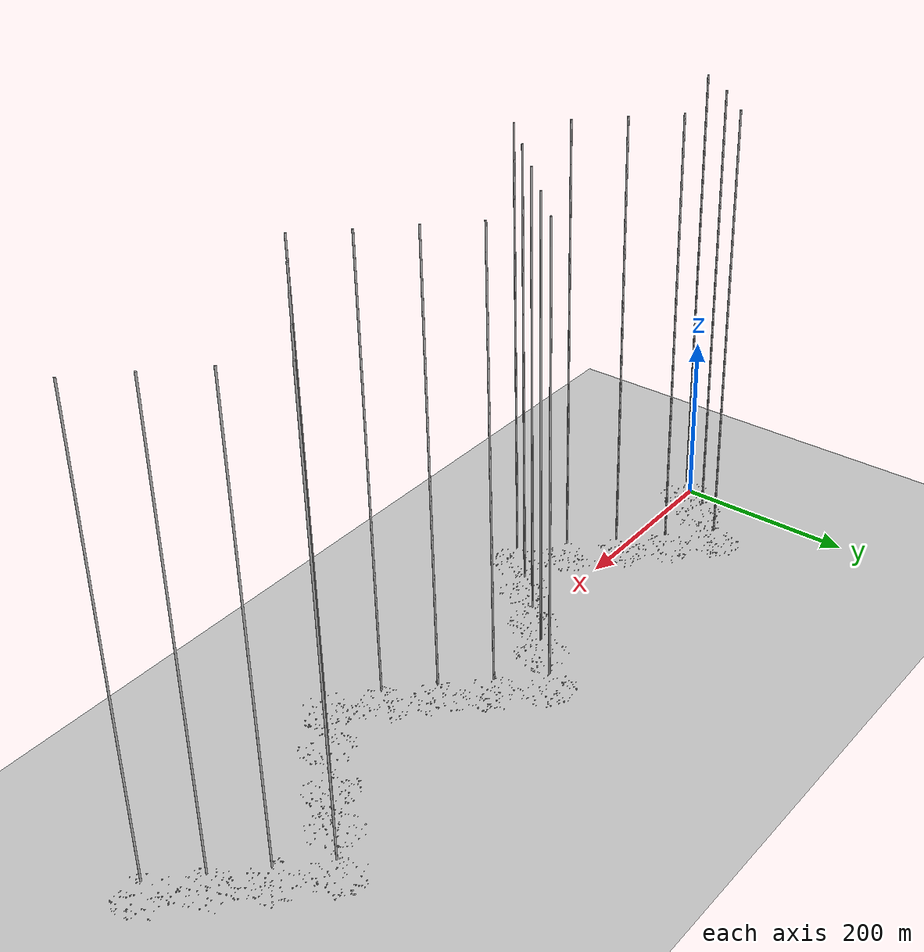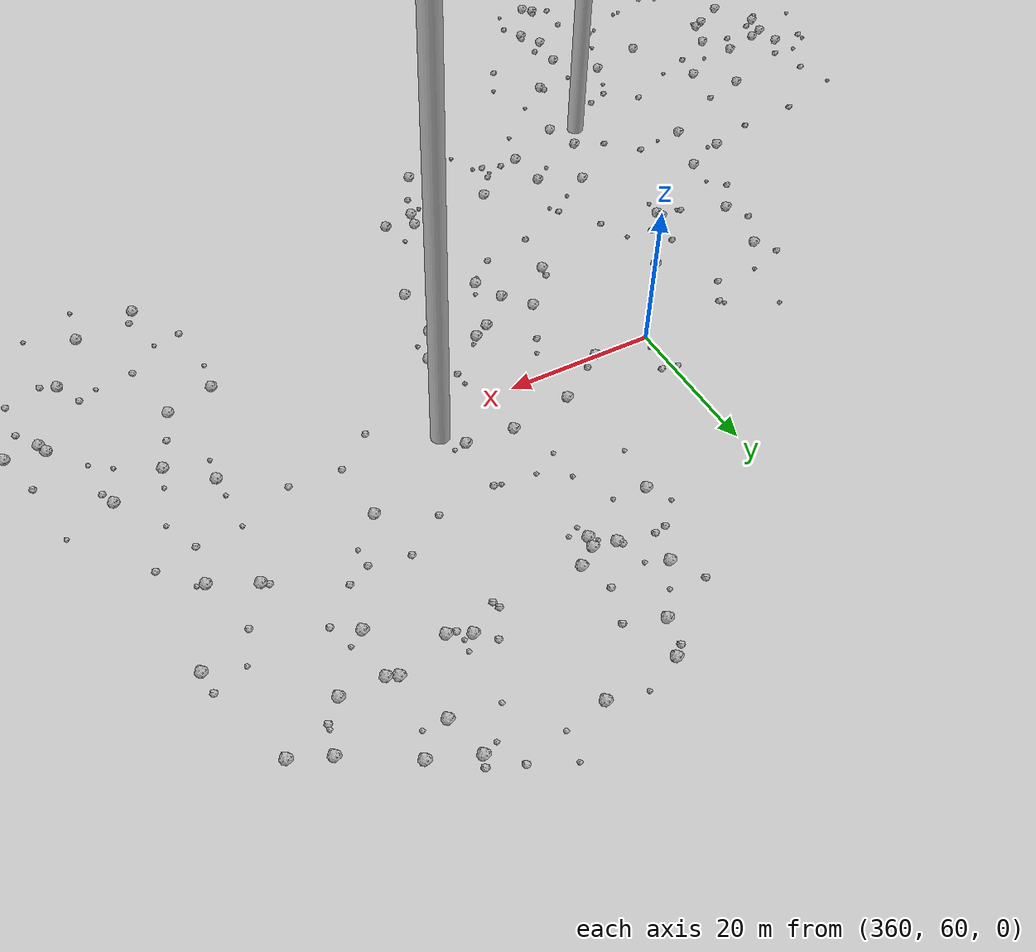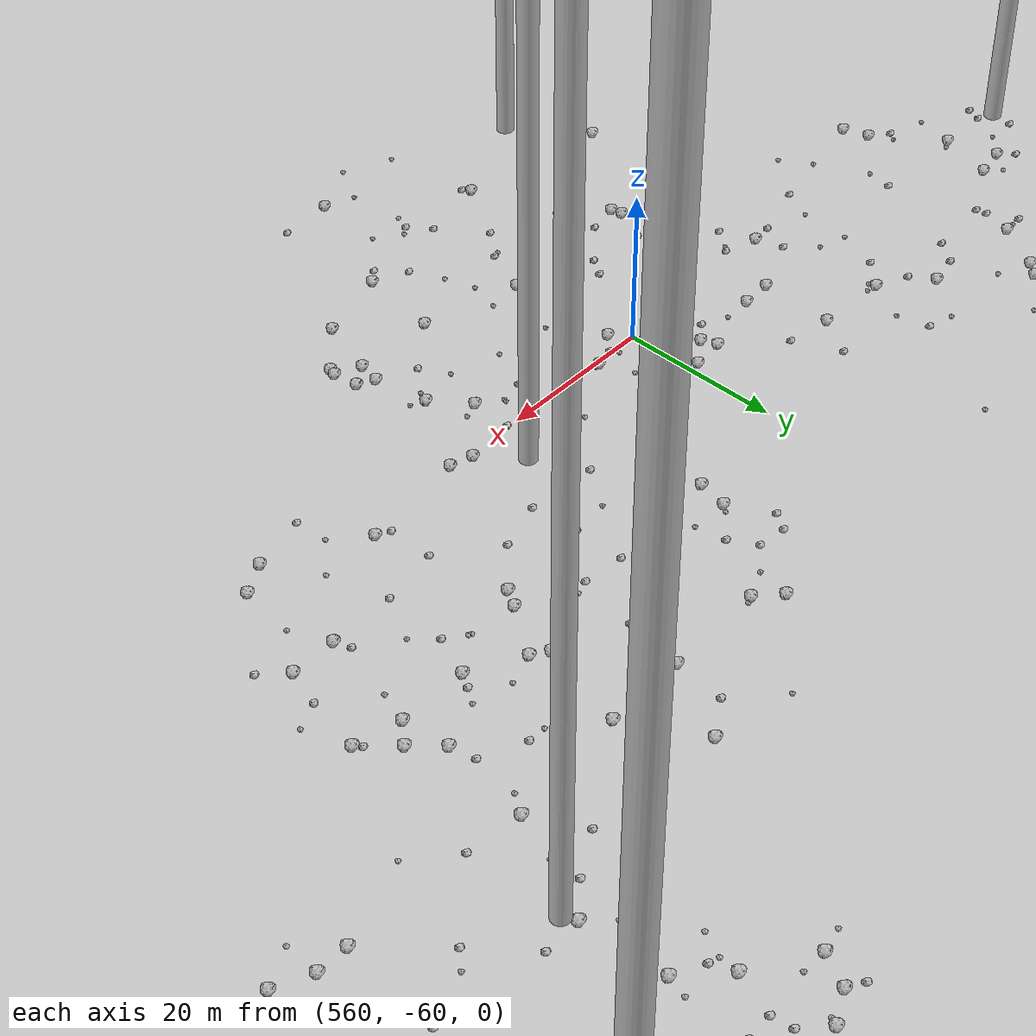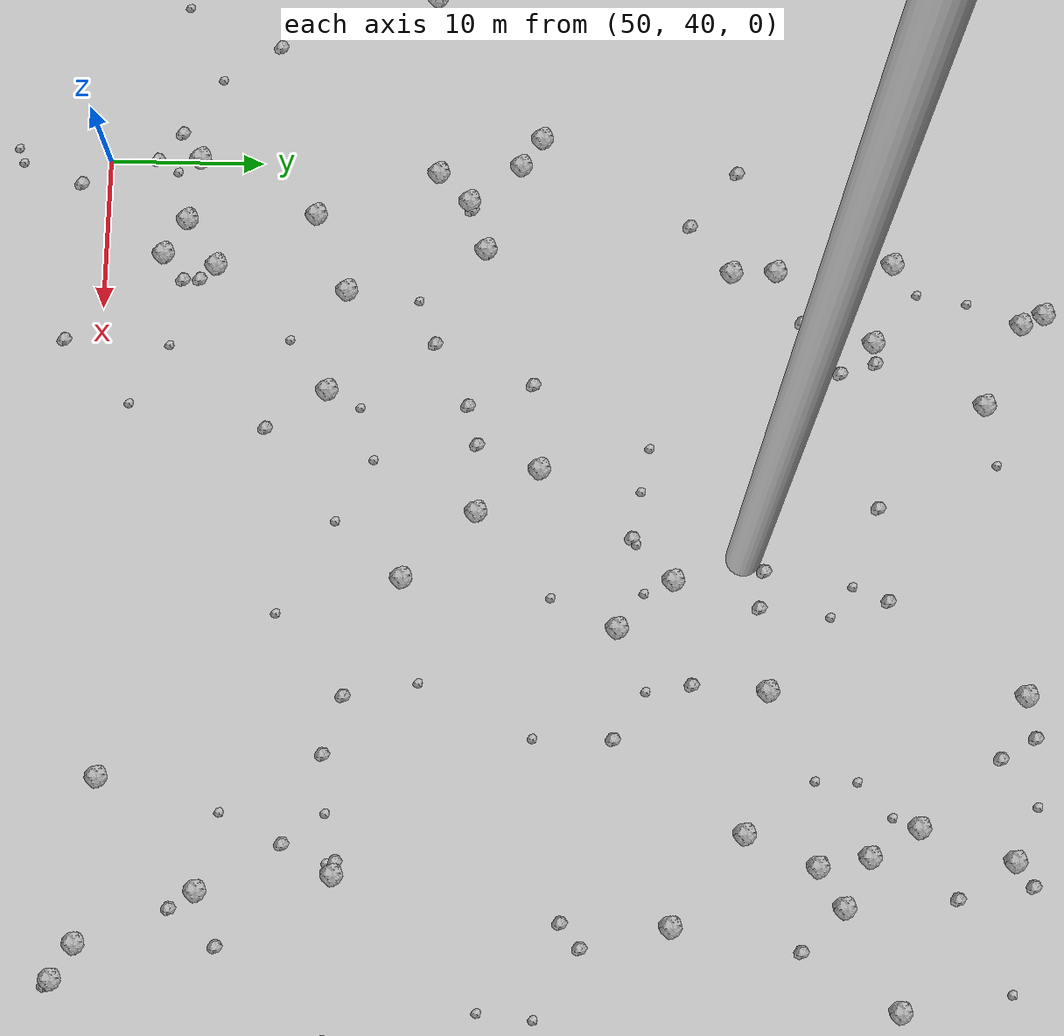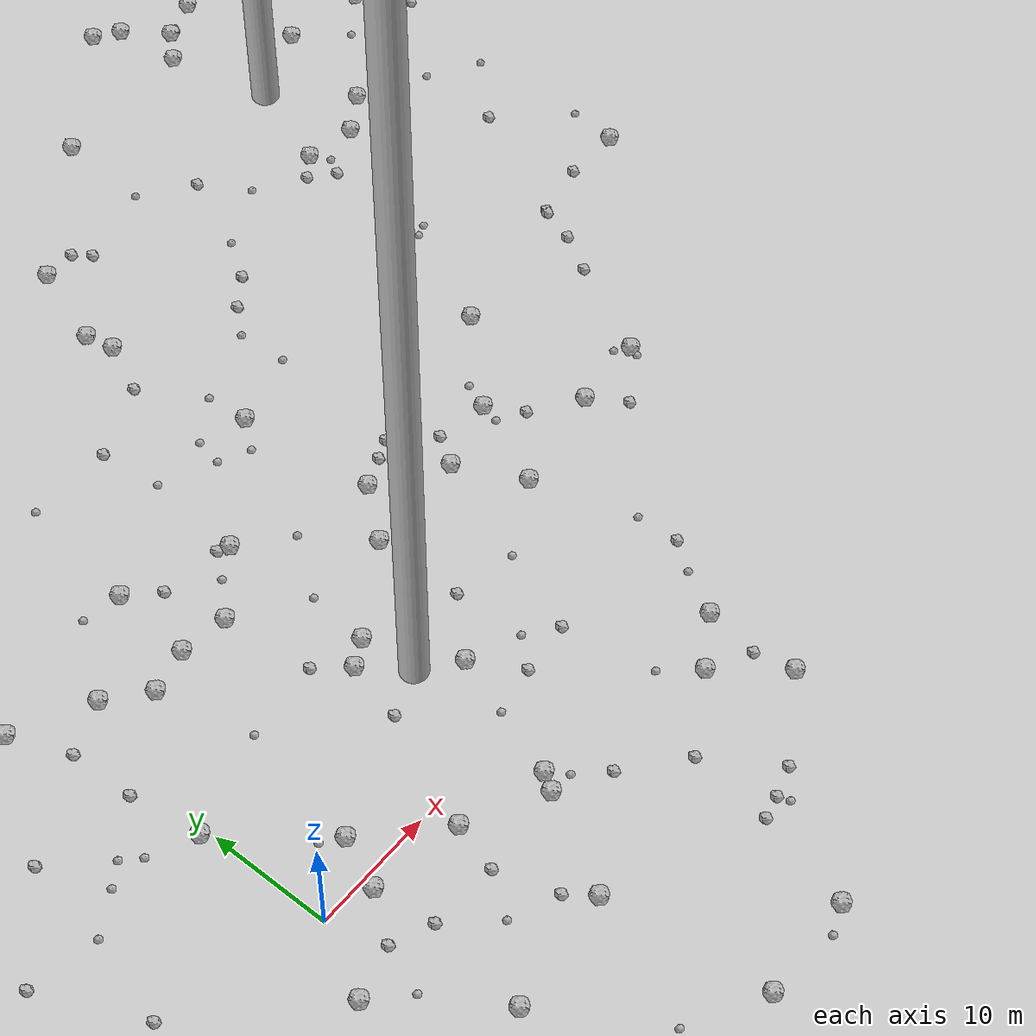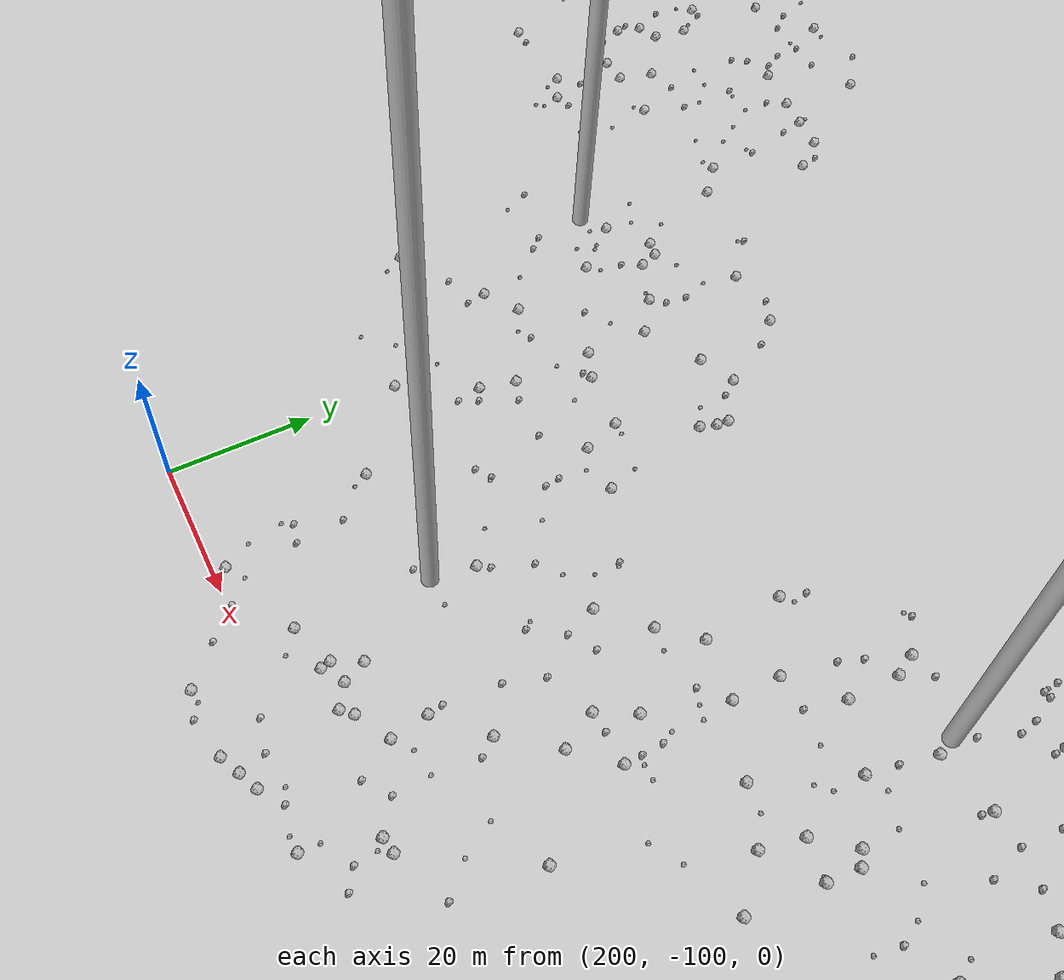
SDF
<sdf version="1.6">
 <world name="default">
  <include><uri>model://custom_ground</uri></include>
  <include><uri>model://sun</uri></include>
  <spherical_coordinates>
   <surface_model>EARTH_WGS84</surface_model>
   <latitude_deg>38.161479</latitude_deg>
   <longitude_deg>-122.454630</longitude_deg>
   <elevation>488.0</elevation>
   <heading_deg>90</heading_deg>
  </spherical_coordinates>
  <model name="rock1_0_0">
   <include><uri>model://rock1</uri><pose>13.286966571104543 -13.128523204111374 0.5 0 0 0</pose></include>
  </model>
  <model name="rock1_0_1">
   <include><uri>model://rock1</uri><pose>-7.793707440409598 -12.59993473266325 0.5 0 0 0</pose></include>
  </model>
  <model name="rock1_0_2">
   <include><uri>model://rock1</uri><pose>36.14987174534792 -12.637709527143485 0.5 0 0 0</pose></include>
  </model>
  <model name="rock1_0_3">
   <include><uri>model://rock1</uri><pose>-17.04982135187817 -6.526912249154119 0.5 0 0 0</pose></include>
  </model>
  <model name="rock1_0_4">
   <include><uri>model://rock1</uri><pose>15.106535435016454 -26.450218066727434 0.5 0 0 0</pose></include>
  </model>
  <model name="rock1_0_5">
   <include><uri>model://rock1</uri><pose>21.752715487701316 5.866929088554812 0.5 0 0 0</pose></include>
  </model>
  <model name="rock1_0_6">
   <include><uri>model://rock1</uri><pose>-18.55723021381221 4.996701976656759 0.5 0 0 0</pose></include>
  </model>
  <model name="rock1_0_7">
   <include><uri>model://rock1</uri><pose>5.799385806703327 21.02924688336863 0.5 0 0 0</pose></include>
  </model>
  <model name="rock1_0_8">
   <include><uri>model://rock1</uri><pose>3.509667257834767 -14.208108217476108 0.5 0 0 0</pose></include>
  </model>
  <model name="rock1_0_9">
   <include><uri>model://rock1</uri><pose>36.027442634918664 -5.090930907194043 0.5 0 0 0</pose></include>
  </model>
  <model name="rock1_0_10">
   <include><uri>model://rock1</uri><pose>5.643129902425908 3.0049528272487365 0.5 0 0 0</pose></include>
  </model>
  <model name="rock1_0_11">
   <include><uri>model://rock1</uri><pose>-3.556545310376233 26.602718643659692 0.5 0 0 0</pose></include>
  </model>
  <model name="rock1_0_12">
   <include><uri>model://rock1</uri><pose>3.9520932658781867 -1.0099971661050837 0.5 0 0 0</pose></include>
  </model>
  <model name="rock1_0_13">
   <include><uri>model://rock1</uri><pose>17.441158644482194 -5.551849124363983 0.5 0 0 0</pose></include>
  </model>
  <model name="rock1_0_14">
   <include><uri>model://rock1</uri><pose>9.946922414717822 28.525707108700843 0.5 0 0 0</pose></include>
  </model>
  <model name="rock1_0_15">
   <include><uri>model://rock1</uri><pose>11.312545177117652 -2.3449170186434074 0.5 0 0 0</pose></include>
  </model>
  <model name="rock1_0_16">
   <include><uri>model://rock1</uri><pose>13.363211874727554 21.351382634093063 0.5 0 0 0</pose></include>
  </model>
  <model name="rock1_0_17">
   <include><uri>model://rock1</uri><pose>23.345374887885406 -26.03592207319582 0.5 0 0 0</pose></include>
  </model>
  <model name="rock1_0_18">
   <include><uri>model://rock1</uri><pose>-3.6710129702892687 -10.931271194933252 0.5 0 0 0</pose></include>
  </model>
  <model name="rock1_0_19">
   <include><uri>model://rock1</uri><pose>18.319943370649312 -4.186400881097075 0.5 0 0 0</pose></include>
  </model>
  <model name="rock1_0_20">
   <include><uri>model://rock1</uri><pose>18.382123102040005 12.713205854098334 0.5 0 0 0</pose></include>
  </model>
  <model name="rock1_0_21">
   <include><uri>model://rock1</uri><pose>9.410440741263212 21.871752656022494 0.5 0 0 0</pose></include>
  </model>
  <model name="rock1_0_22">
   <include><uri>model://rock1</uri><pose>2.6106355768410587 23.58441520889 0.5 0 0 0</pose></include>
  </model>
  <model name="rock1_0_23">
   <include><uri>model://rock1</uri><pose>-2.894710866368648 -5.721683616664414 0.5 0 0 0</pose></include>
  </model>
  <model name="rock1_0_24">
   <include><uri>model://rock1</uri><pose>-0.5670920835291575 10.83933732982436 0.5 0 0 0</pose></include>
  </model>
  <model name="rock1_0_25">
   <include><uri>model://rock1</uri><pose>16.283090063141913 11.564673228973248 0.5 0 0 0</pose></include>
  </model>
  <model name="rock1_0_26">
   <include><uri>model://rock1</uri><pose>32.0852214428337 -7.691675619685704 0.5 0 0 0</pose></include>
  </model>
  <model name="rock2_0_0">
   <include><uri>model://rock2</uri><pose>39.511522620609846 0.6571161901722462 0.3 0 0 0</pose></include>
  </model>
  <model name="rock2_0_1">
   <include><uri>model://rock2</uri><pose>3.0526232841287566 -23.68685819998147 0.3 0 0 0</pose></include>
  </model>
  <model name="rock2_0_2">
   <include><uri>model://rock2</uri><pose>-17.97502402749664 -1.0013806443976634 0.3 0 0 0</pose></include>
  </model>
  <model name="rock2_0_3">
   <include><uri>model://rock2</uri><pose>-1.4679411579164494 16.68277257527894 0.3 0 0 0</pose></include>
  </model>
  <model name="rock2_0_4">
   <include><uri>model://rock2</uri><pose>29.577717610498347 -16.93845536459665 0.3 0 0 0</pose></include>
  </model>
  <model name="rock2_0_5">
   <include><uri>model://rock2</uri><pose>-1.665017264469494 21.958741096450666 0.3 0 0 0</pose></include>
  </model>
  <model name="rock2_0_6">
   <include><uri>model://rock2</uri><pose>24.007819171501424 1.9943056290617136 0.3 0 0 0</pose></include>
  </model>
  <model name="rock2_0_7">
   <include><uri>model://rock2</uri><pose>10.162541737498398 -6.188878850403462 0.3 0 0 0</pose></include>
  </model>
  <model name="rock2_0_8">
   <include><uri>model://rock2</uri><pose>11.736534085510765 -11.027163773135538 0.3 0 0 0</pose></include>
  </model>
  <model name="rock2_0_9">
   <include><uri>model://rock2</uri><pose>-16.526548982687093 11.744923736352675 0.3 0 0 0</pose></include>
  </model>
  <model name="rock2_0_10">
   <include><uri>model://rock2</uri><pose>27.12929005095026 -17.726646397858293 0.3 0 0 0</pose></include>
  </model>
  <model name="rock2_0_11">
   <include><uri>model://rock2</uri><pose>21.465349726095923 -7.81735851330534 0.3 0 0 0</pose></include>
  </model>
  <model name="rock2_0_12">
   <include><uri>model://rock2</uri><pose>28.347363490896868 2.437573717505657 0.3 0 0 0</pose></include>
  </model>
  <model name="rock2_0_13">
   <include><uri>model://rock2</uri><pose>1.343606360800763 -4.526268079513702 0.3 0 0 0</pose></include>
  </model>
  <model name="rock2_0_14">
   <include><uri>model://rock2</uri><pose>15.077482739098492 6.8241567899605045 0.3 0 0 0</pose></include>
  </model>
  <model name="rock2_0_15">
   <include><uri>model://rock2</uri><pose>35.4155768558774 -9.429178150903844 0.3 0 0 0</pose></include>
  </model>
  <model name="rock2_0_16">
   <include><uri>model://rock2</uri><pose>25.675337666096766 10.022350493966123 0.3 0 0 0</pose></include>
  </model>
  <model name="rock2_0_17">
   <include><uri>model://rock2</uri><pose>-5.3161917703541945 -7.543955118676603 0.3 0 0 0</pose></include>
  </model>
  <model name="rock2_0_18">
   <include><uri>model://rock2</uri><pose>12.231125513551802 26.37418858297334 0.3 0 0 0</pose></include>
  </model>
  <model name="rock2_0_19">
   <include><uri>model://rock2</uri><pose>14.156926066772662 13.99271335200752 0.3 0 0 0</pose></include>
  </model>
  <model name="rock2_0_20">
   <include><uri>model://rock2</uri><pose>-9.597423221930368 17.850422889719106 0.3 0 0 0</pose></include>
  </model>
  <model name="rock2_0_21">
   <include><uri>model://rock2</uri><pose>25.977006911203013 -11.45432211050678 0.3 0 0 0</pose></include>
  </model>
  <model name="rock2_0_22">
   <include><uri>model://rock2</uri><pose>25.287514110438224 -18.175200634990347 0.3 0 0 0</pose></include>
  </model>
  <model name="rock2_0_23">
   <include><uri>model://rock2</uri><pose>-16.827313394154544 1.3737659188770301 0.3 0 0 0</pose></include>
  </model>
  <model name="rock2_0_24">
   <include><uri>model://rock2</uri><pose>4.59993781038208 -5.864462377141102 0.3 0 0 0</pose></include>
  </model>
  <model name="rock2_0_25">
   <include><uri>model://rock2</uri><pose>-12.76827505918699 3.684847758152209 0.3 0 0 0</pose></include>
  </model>
  <model name="rock2_0_26">
   <include><uri>model://rock2</uri><pose>-1.1278754866212672 -15.582133359837568 0.3 0 0 0</pose></include>
  </model>
  <model name="rock3_0_0">
   <include><uri>model://rock3</uri><pose>-5.446146516498018 -24.934600741461296 0.2 0 0 0</pose></include>
  </model>
  <model name="rock3_0_1">
   <include><uri>model://rock3</uri><pose>21.056116553107678 -26.99694283174135 0.2 0 0 0</pose></include>
  </model>
  <model name="rock3_0_2">
   <include><uri>model://rock3</uri><pose>25.949683445074285 4.204262396968666 0.2 0 0 0</pose></include>
  </model>
  <model name="rock3_0_3">
   <include><uri>model://rock3</uri><pose>-14.122480906598271 0.4570074128183954 0.2 0 0 0</pose></include>
  </model>
  <model name="rock3_0_4">
   <include><uri>model://rock3</uri><pose>29.750074231977585 -5.0455477776044475 0.2 0 0 0</pose></include>
  </model>
  <model name="rock3_0_5">
   <include><uri>model://rock3</uri><pose>27.0532889936255 15.045558084281417 0.2 0 0 0</pose></include>
  </model>
  <model name="rock3_0_6">
   <include><uri>model://rock3</uri><pose>7.599403196936464 13.32390620876226 0.2 0 0 0</pose></include>
  </model>
  <model name="rock3_0_7">
   <include><uri>model://rock3</uri><pose>-10.761041200199237 10.69266523520892 0.2 0 0 0</pose></include>
  </model>
  <model name="rock3_0_8">
   <include><uri>model://rock3</uri><pose>27.474553162149064 -18.67319702473429 0.2 0 0 0</pose></include>
  </model>
  <model name="rock3_0_9">
   <include><uri>model://rock3</uri><pose>15.698589446201815 23.886129626916002 0.2 0 0 0</pose></include>
  </model>
  <model name="rock3_0_10">
   <include><uri>model://rock3</uri><pose>-7.467186900818582 12.629856344235293 0.2 0 0 0</pose></include>
  </model>
  <model name="rock3_0_11">
   <include><uri>model://rock3</uri><pose>-5.645246962667205 13.813375220566286 0.2 0 0 0</pose></include>
  </model>
  <model name="rock3_0_12">
   <include><uri>model://rock3</uri><pose>9.089907698636434 -23.254074880086833 0.2 0 0 0</pose></include>
  </model>
  <model name="rock3_0_13">
   <include><uri>model://rock3</uri><pose>18.780179657529033 17.71951090621281 0.2 0 0 0</pose></include>
  </model>
  <model name="rock3_0_14">
   <include><uri>model://rock3</uri><pose>-15.12653399396589 3.09098225889808 0.2 0 0 0</pose></include>
  </model>
  <model name="rock3_0_15">
   <include><uri>model://rock3</uri><pose>20.12668112502375 1.2142983698153955 0.2 0 0 0</pose></include>
  </model>
  <model name="rock3_0_16">
   <include><uri>model://rock3</uri><pose>30.775027959857773 9.059718682275665 0.2 0 0 0</pose></include>
  </model>
  <model name="rock3_0_17">
   <include><uri>model://rock3</uri><pose>-4.33079321056557 12.558185429483359 0.2 0 0 0</pose></include>
  </model>
  <model name="rock3_0_18">
   <include><uri>model://rock3</uri><pose>37.901288934524324 -1.6458157994037812 0.2 0 0 0</pose></include>
  </model>
  <model name="rock3_0_19">
   <include><uri>model://rock3</uri><pose>39.311690337433966 4.107886323450565 0.2 0 0 0</pose></include>
  </model>
  <model name="rock3_0_20">
   <include><uri>model://rock3</uri><pose>-17.582396430248103 -1.2396199626287299 0.2 0 0 0</pose></include>
  </model>
  <model name="rock3_0_21">
   <include><uri>model://rock3</uri><pose>-0.09860599430447792 -8.36431978216548 0.2 0 0 0</pose></include>
  </model>
  <model name="rock3_0_22">
   <include><uri>model://rock3</uri><pose>19.355810723616713 -5.688573381298667 0.2 0 0 0</pose></include>
  </model>
  <model name="rock3_0_23">
   <include><uri>model://rock3</uri><pose>8.065508000442044 -29.766982432922372 0.2 0 0 0</pose></include>
  </model>
  <model name="rock3_0_24">
   <include><uri>model://rock3</uri><pose>7.896266594882533 -9.466725775914384 0.2 0 0 0</pose></include>
  </model>
  <model name="rock3_0_25">
   <include><uri>model://rock3</uri><pose>4.131841167509698 4.176269223117842 0.2 0 0 0</pose></include>
  </model>
  <model name="rock3_0_26">
   <include><uri>model://rock3</uri><pose>6.715364204869246 29.147083662439783 0.2 0 0 0</pose></include>
  </model>
  <model name="rock1_1_0">
   <include><uri>model://rock1</uri><pose>27.697496210943232 53.37085878052541 0.5 0 0 0</pose></include>
  </model>
  <model name="rock1_1_1">
   <include><uri>model://rock1</uri><pose>18.191860689089555 25.34175276844364 0.5 0 0 0</pose></include>
  </model>
  <model name="rock1_1_2">
   <include><uri>model://rock1</uri><pose>25.84671593320597 44.55131858144504 0.5 0 0 0</pose></include>
  </model>
  <model name="rock1_1_3">
   <include><uri>model://rock1</uri><pose>36.7508866287226 12.350050723925222 0.5 0 0 0</pose></include>
  </model>
  <model name="rock1_1_4">
   <include><uri>model://rock1</uri><pose>25.548394536428653 17.286890133102304 0.5 0 0 0</pose></include>
  </model>
  <model name="rock1_1_5">
   <include><uri>model://rock1</uri><pose>52.41194086333789 63.49761908278117 0.5 0 0 0</pose></include>
  </model>
  <model name="rock1_1_6">
   <include><uri>model://rock1</uri><pose>38.310876734286765 61.072702017978834 0.5 0 0 0</pose></include>
  </model>
  <model name="rock1_1_7">
   <include><uri>model://rock1</uri><pose>56.37225101905334 43.729642814357874 0.5 0 0 0</pose></include>
  </model>
  <model name="rock1_1_8">
   <include><uri>model://rock1</uri><pose>55.664405808301886 64.63908396076772 0.5 0 0 0</pose></include>
  </model>
  <model name="rock1_1_9">
   <include><uri>model://rock1</uri><pose>45.676150703125614 25.488925917407226 0.5 0 0 0</pose></include>
  </model>
  <model name="rock1_1_10">
   <include><uri>model://rock1</uri><pose>34.08751765057313 17.685181478582926 0.5 0 0 0</pose></include>
  </model>
  <model name="rock1_1_11">
   <include><uri>model://rock1</uri><pose>49.865957405847816 45.861891880736174 0.5 0 0 0</pose></include>
  </model>
  <model name="rock1_1_12">
   <include><uri>model://rock1</uri><pose>45.241510341834605 13.872812571224207 0.5 0 0 0</pose></include>
  </model>
  <model name="rock1_1_13">
   <include><uri>model://rock1</uri><pose>27.371476289988216 32.24600859667254 0.5 0 0 0</pose></include>
  </model>
  <model name="rock1_1_14">
   <include><uri>model://rock1</uri><pose>49.929763417029484 66.80982265565154 0.5 0 0 0</pose></include>
  </model>
  <model name="rock1_1_15">
   <include><uri>model://rock1</uri><pose>28.707599453390756 21.174014714904494 0.5 0 0 0</pose></include>
  </model>
  <model name="rock1_1_16">
   <include><uri>model://rock1</uri><pose>48.03132810752272 68.15038274336416 0.5 0 0 0</pose></include>
  </model>
  <model name="rock1_1_17">
   <include><uri>model://rock1</uri><pose>25.365684060507178 46.8594913624517 0.5 0 0 0</pose></include>
  </model>
  <model name="rock1_1_18">
   <include><uri>model://rock1</uri><pose>66.73098444948104 28.640572369023964 0.5 0 0 0</pose></include>
  </model>
  <model name="rock1_1_19">
   <include><uri>model://rock1</uri><pose>53.53675538838357 53.55195628164289 0.5 0 0 0</pose></include>
  </model>
  <model name="rock1_1_20">
   <include><uri>model://rock1</uri><pose>57.079935431016494 47.1703690664612 0.5 0 0 0</pose></include>
  </model>
  <model name="rock1_1_21">
   <include><uri>model://rock1</uri><pose>51.20806562443454 14.199906386174986 0.5 0 0 0</pose></include>
  </model>
  <model name="rock1_1_22">
   <include><uri>model://rock1</uri><pose>54.03110255889851 45.176442698024815 0.5 0 0 0</pose></include>
  </model>
  <model name="rock1_1_23">
   <include><uri>model://rock1</uri><pose>39.73790726982418 19.282952062664695 0.5 0 0 0</pose></include>
  </model>
  <model name="rock1_1_24">
   <include><uri>model://rock1</uri><pose>17.47492809239318 51.598503380366374 0.5 0 0 0</pose></include>
  </model>
  <model name="rock1_1_25">
   <include><uri>model://rock1</uri><pose>50.51042544229346 61.44176394448849 0.5 0 0 0</pose></include>
  </model>
  <model name="rock1_1_26">
   <include><uri>model://rock1</uri><pose>58.63626132789203 55.703805123825084 0.5 0 0 0</pose></include>
  </model>
  <model name="rock2_1_0">
   <include><uri>model://rock2</uri><pose>24.038842448476323 40.68294890641212 0.3 0 0 0</pose></include>
  </model>
  <model name="rock2_1_1">
   <include><uri>model://rock2</uri><pose>57.49577513128626 27.609967771551837 0.3 0 0 0</pose></include>
  </model>
  <model name="rock2_1_2">
   <include><uri>model://rock2</uri><pose>18.189997704923496 38.24278835758646 0.3 0 0 0</pose></include>
  </model>
  <model name="rock2_1_3">
   <include><uri>model://rock2</uri><pose>31.38980797622179 52.16483115638144 0.3 0 0 0</pose></include>
  </model>
  <model name="rock2_1_4">
   <include><uri>model://rock2</uri><pose>35.53362744474934 20.043885527294144 0.3 0 0 0</pose></include>
  </model>
  <model name="rock2_1_5">
   <include><uri>model://rock2</uri><pose>49.93448731902939 43.07667121976878 0.3 0 0 0</pose></include>
  </model>
  <model name="rock2_1_6">
   <include><uri>model://rock2</uri><pose>41.42222282873942 16.519187101531827 0.3 0 0 0</pose></include>
  </model>
  <model name="rock2_1_7">
   <include><uri>model://rock2</uri><pose>51.63979161520974 38.18633469062303 0.3 0 0 0</pose></include>
  </model>
  <model name="rock2_1_8">
   <include><uri>model://rock2</uri><pose>31.076178518693897 22.24688050669921 0.3 0 0 0</pose></include>
  </model>
  <model name="rock2_1_9">
   <include><uri>model://rock2</uri><pose>67.8466174142539 50.78432707393343 0.3 0 0 0</pose></include>
  </model>
  <model name="rock2_1_10">
   <include><uri>model://rock2</uri><pose>52.89637195736925 63.67297834529771 0.3 0 0 0</pose></include>
  </model>
  <model name="rock2_1_11">
   <include><uri>model://rock2</uri><pose>30.80130130710151 68.05423926162209 0.3 0 0 0</pose></include>
  </model>
  <model name="rock2_1_12">
   <include><uri>model://rock2</uri><pose>30.36707283396245 53.48704689452302 0.3 0 0 0</pose></include>
  </model>
  <model name="rock2_1_13">
   <include><uri>model://rock2</uri><pose>41.94513093636275 50.849658487253166 0.3 0 0 0</pose></include>
  </model>
  <model name="rock2_1_14">
   <include><uri>model://rock2</uri><pose>17.259920241957907 25.84665214033189 0.3 0 0 0</pose></include>
  </model>
  <model name="rock2_1_15">
   <include><uri>model://rock2</uri><pose>57.9861959530014 46.157885661246524 0.3 0 0 0</pose></include>
  </model>
  <model name="rock2_1_16">
   <include><uri>model://rock2</uri><pose>58.053965585988365 45.07658468368588 0.3 0 0 0</pose></include>
  </model>
  <model name="rock2_1_17">
   <include><uri>model://rock2</uri><pose>48.0671471339519 44.6369718643723 0.3 0 0 0</pose></include>
  </model>
  <model name="rock2_1_18">
   <include><uri>model://rock2</uri><pose>56.60386312036241 24.846215271877867 0.3 0 0 0</pose></include>
  </model>
  <model name="rock2_1_19">
   <include><uri>model://rock2</uri><pose>37.303165097517535 41.776529979780726 0.3 0 0 0</pose></include>
  </model>
  <model name="rock2_1_20">
   <include><uri>model://rock2</uri><pose>34.870019310272625 40.02135298601 0.3 0 0 0</pose></include>
  </model>
  <model name="rock2_1_21">
   <include><uri>model://rock2</uri><pose>62.14617820717662 28.754287883797694 0.3 0 0 0</pose></include>
  </model>
  <model name="rock2_1_22">
   <include><uri>model://rock2</uri><pose>32.66792185772975 22.936779603288453 0.3 0 0 0</pose></include>
  </model>
  <model name="rock2_1_23">
   <include><uri>model://rock2</uri><pose>54.89293685960355 21.81958625037945 0.3 0 0 0</pose></include>
  </model>
  <model name="rock2_1_24">
   <include><uri>model://rock2</uri><pose>62.231890988923226 37.60643990178873 0.3 0 0 0</pose></include>
  </model>
  <model name="rock2_1_25">
   <include><uri>model://rock2</uri><pose>47.116869027933355 11.094274910217177 0.3 0 0 0</pose></include>
  </model>
  <model name="rock2_1_26">
   <include><uri>model://rock2</uri><pose>57.63053751287556 27.813191893488348 0.3 0 0 0</pose></include>
  </model>
  <model name="rock3_1_0">
   <include><uri>model://rock3</uri><pose>32.15873733946073 20.259237109966804 0.2 0 0 0</pose></include>
  </model>
  <model name="rock3_1_1">
   <include><uri>model://rock3</uri><pose>37.93179951481545 53.776195946627226 0.2 0 0 0</pose></include>
  </model>
  <model name="rock3_1_2">
   <include><uri>model://rock3</uri><pose>67.02385097186652 32.48530715517144 0.2 0 0 0</pose></include>
  </model>
  <model name="rock3_1_3">
   <include><uri>model://rock3</uri><pose>18.793870056634198 33.22023492820348 0.2 0 0 0</pose></include>
  </model>
  <model name="rock3_1_4">
   <include><uri>model://rock3</uri><pose>27.085335092827762 35.72755606776945 0.2 0 0 0</pose></include>
  </model>
  <model name="rock3_1_5">
   <include><uri>model://rock3</uri><pose>39.37355032961202 17.765773300177948 0.2 0 0 0</pose></include>
  </model>
  <model name="rock3_1_6">
   <include><uri>model://rock3</uri><pose>44.293659832353526 47.0983660512608 0.2 0 0 0</pose></include>
  </model>
  <model name="rock3_1_7">
   <include><uri>model://rock3</uri><pose>59.15583513702259 60.40374913519868 0.2 0 0 0</pose></include>
  </model>
  <model name="rock3_1_8">
   <include><uri>model://rock3</uri><pose>23.174310518767456 31.253764352674484 0.2 0 0 0</pose></include>
  </model>
  <model name="rock3_1_9">
   <include><uri>model://rock3</uri><pose>22.0509683897752 22.267807468667883 0.2 0 0 0</pose></include>
  </model>
  <model name="rock3_1_10">
   <include><uri>model://rock3</uri><pose>50.17838175227966 15.052838728171498 0.2 0 0 0</pose></include>
  </model>
  <model name="rock3_1_11">
   <include><uri>model://rock3</uri><pose>40.55787808135423 21.3951643245889 0.2 0 0 0</pose></include>
  </model>
  <model name="rock3_1_12">
   <include><uri>model://rock3</uri><pose>49.29699131977538 33.93155139698561 0.2 0 0 0</pose></include>
  </model>
  <model name="rock3_1_13">
   <include><uri>model://rock3</uri><pose>33.070402365608786 37.91884837725204 0.2 0 0 0</pose></include>
  </model>
  <model name="rock3_1_14">
   <include><uri>model://rock3</uri><pose>50.2772055276017 34.28999889526011 0.2 0 0 0</pose></include>
  </model>
  <model name="rock3_1_15">
   <include><uri>model://rock3</uri><pose>66.38404446047299 41.93383142096342 0.2 0 0 0</pose></include>
  </model>
  <model name="rock3_1_16">
   <include><uri>model://rock3</uri><pose>25.595383598198907 30.04989375289868 0.2 0 0 0</pose></include>
  </model>
  <model name="rock3_1_17">
   <include><uri>model://rock3</uri><pose>31.024251126286874 65.82089947053552 0.2 0 0 0</pose></include>
  </model>
  <model name="rock3_1_18">
   <include><uri>model://rock3</uri><pose>62.44822586730537 44.36070529988984 0.2 0 0 0</pose></include>
  </model>
  <model name="rock3_1_19">
   <include><uri>model://rock3</uri><pose>33.3404530115817 33.910756042628606 0.2 0 0 0</pose></include>
  </model>
  <model name="rock3_1_20">
   <include><uri>model://rock3</uri><pose>23.599713441143805 33.45547039458151 0.2 0 0 0</pose></include>
  </model>
  <model name="rock3_1_21">
   <include><uri>model://rock3</uri><pose>13.507919529007884 47.57304498567048 0.2 0 0 0</pose></include>
  </model>
  <model name="rock3_1_22">
   <include><uri>model://rock3</uri><pose>39.27640178305486 44.689308492180025 0.2 0 0 0</pose></include>
  </model>
  <model name="rock3_1_23">
   <include><uri>model://rock3</uri><pose>50.71495516639344 44.40786150718563 0.2 0 0 0</pose></include>
  </model>
  <model name="rock3_1_24">
   <include><uri>model://rock3</uri><pose>50.984658050580435 13.440048894127594 0.2 0 0 0</pose></include>
  </model>
  <model name="rock3_1_25">
   <include><uri>model://rock3</uri><pose>11.258413157816939 38.43722721650642 0.2 0 0 0</pose></include>
  </model>
  <model name="rock3_1_26">
   <include><uri>model://rock3</uri><pose>61.946527391831324 52.137574993396456 0.2 0 0 0</pose></include>
  </model>
  <model name="rock1_2_0">
   <include><uri>model://rock1</uri><pose>99.16861714387996 77.06731370915774 0.5 0 0 0</pose></include>
  </model>
  <model name="rock1_2_1">
   <include><uri>model://rock1</uri><pose>74.46879011357244 106.58501667843184 0.5 0 0 0</pose></include>
  </model>
  <model name="rock1_2_2">
   <include><uri>model://rock1</uri><pose>56.131046627602274 91.00880167963952 0.5 0 0 0</pose></include>
  </model>
  <model name="rock1_2_3">
   <include><uri>model://rock1</uri><pose>73.127946209544 64.40619714106836 0.5 0 0 0</pose></include>
  </model>
  <model name="rock1_2_4">
   <include><uri>model://rock1</uri><pose>65.31917000560514 54.65600122619671 0.5 0 0 0</pose></include>
  </model>
  <model name="rock1_2_5">
   <include><uri>model://rock1</uri><pose>94.58190134599506 89.41022313144668 0.5 0 0 0</pose></include>
  </model>
  <model name="rock1_2_6">
   <include><uri>model://rock1</uri><pose>94.65473782023406 98.42095799790962 0.5 0 0 0</pose></include>
  </model>
  <model name="rock1_2_7">
   <include><uri>model://rock1</uri><pose>80.46428876585952 73.49284964801032 0.5 0 0 0</pose></include>
  </model>
  <model name="rock1_2_8">
   <include><uri>model://rock1</uri><pose>95.2625174676557 86.17450399809769 0.5 0 0 0</pose></include>
  </model>
  <model name="rock1_2_9">
   <include><uri>model://rock1</uri><pose>65.44580523734805 96.86319130738354 0.5 0 0 0</pose></include>
  </model>
  <model name="rock1_2_10">
   <include><uri>model://rock1</uri><pose>92.69284300066226 92.48677595303806 0.5 0 0 0</pose></include>
  </model>
  <model name="rock1_2_11">
   <include><uri>model://rock1</uri><pose>93.32461564497511 81.61753167435263 0.5 0 0 0</pose></include>
  </model>
  <model name="rock1_2_12">
   <include><uri>model://rock1</uri><pose>78.52616018119805 104.00016214353548 0.5 0 0 0</pose></include>
  </model>
  <model name="rock1_2_13">
   <include><uri>model://rock1</uri><pose>77.52303072735728 59.771098700911395 0.5 0 0 0</pose></include>
  </model>
  <model name="rock1_2_14">
   <include><uri>model://rock1</uri><pose>96.39479690932728 56.0374911703198 0.5 0 0 0</pose></include>
  </model>
  <model name="rock1_2_15">
   <include><uri>model://rock1</uri><pose>77.31546406922598 77.02066142442644 0.5 0 0 0</pose></include>
  </model>
  <model name="rock1_2_16">
   <include><uri>model://rock1</uri><pose>70.25071480277535 68.39000729724421 0.5 0 0 0</pose></include>
  </model>
  <model name="rock1_2_17">
   <include><uri>model://rock1</uri><pose>56.89933104863769 80.57240187537263 0.5 0 0 0</pose></include>
  </model>
  <model name="rock1_2_18">
   <include><uri>model://rock1</uri><pose>61.42741712820527 89.74759717592059 0.5 0 0 0</pose></include>
  </model>
  <model name="rock1_2_19">
   <include><uri>model://rock1</uri><pose>84.28926904023278 83.02917157634926 0.5 0 0 0</pose></include>
  </model>
  <model name="rock1_2_20">
   <include><uri>model://rock1</uri><pose>59.30125053536784 100.73017150854243 0.5 0 0 0</pose></include>
  </model>
  <model name="rock1_2_21">
   <include><uri>model://rock1</uri><pose>97.75504698785562 87.81790734274263 0.5 0 0 0</pose></include>
  </model>
  <model name="rock1_2_22">
   <include><uri>model://rock1</uri><pose>84.25262108301852 99.27837728688732 0.5 0 0 0</pose></include>
  </model>
  <model name="rock1_2_23">
   <include><uri>model://rock1</uri><pose>56.78904365269554 83.4368971484675 0.5 0 0 0</pose></include>
  </model>
  <model name="rock1_2_24">
   <include><uri>model://rock1</uri><pose>87.18094721766303 105.79038848877495 0.5 0 0 0</pose></include>
  </model>
  <model name="rock1_2_25">
   <include><uri>model://rock1</uri><pose>104.08198198818924 91.24101616944156 0.5 0 0 0</pose></include>
  </model>
  <model name="rock1_2_26">
   <include><uri>model://rock1</uri><pose>60.015052667553434 99.2693514615987 0.5 0 0 0</pose></include>
  </model>
  <model name="rock2_2_0">
   <include><uri>model://rock2</uri><pose>100.5651843691196 71.47745447144716 0.3 0 0 0</pose></include>
  </model>
  <model name="rock2_2_1">
   <include><uri>model://rock2</uri><pose>96.15922403803428 99.56171346854171 0.3 0 0 0</pose></include>
  </model>
  <model name="rock2_2_2">
   <include><uri>model://rock2</uri><pose>66.1044685452259 63.74402972184865 0.3 0 0 0</pose></include>
  </model>
  <model name="rock2_2_3">
   <include><uri>model://rock2</uri><pose>87.51368949822111 73.36498231843963 0.3 0 0 0</pose></include>
  </model>
  <model name="rock2_2_4">
   <include><uri>model://rock2</uri><pose>77.96880388654378 104.28162668194074 0.3 0 0 0</pose></include>
  </model>
  <model name="rock2_2_5">
   <include><uri>model://rock2</uri><pose>100.4912177278625 85.1701242443107 0.3 0 0 0</pose></include>
  </model>
  <model name="rock2_2_6">
   <include><uri>model://rock2</uri><pose>88.21142356116789 97.64020085233665 0.3 0 0 0</pose></include>
  </model>
  <model name="rock2_2_7">
   <include><uri>model://rock2</uri><pose>88.8369357415771 55.19253813089996 0.3 0 0 0</pose></include>
  </model>
  <model name="rock2_2_8">
   <include><uri>model://rock2</uri><pose>50.065744639888244 80.91169862926577 0.3 0 0 0</pose></include>
  </model>
  <model name="rock2_2_9">
   <include><uri>model://rock2</uri><pose>62.017147253741626 61.540125700735786 0.3 0 0 0</pose></include>
  </model>
  <model name="rock2_2_10">
   <include><uri>model://rock2</uri><pose>97.02724495858891 94.8735171729948 0.3 0 0 0</pose></include>
  </model>
  <model name="rock2_2_11">
   <include><uri>model://rock2</uri><pose>83.95209078379952 78.26621981230392 0.3 0 0 0</pose></include>
  </model>
  <model name="rock2_2_12">
   <include><uri>model://rock2</uri><pose>69.29026694779486 106.91266189453181 0.3 0 0 0</pose></include>
  </model>
  <model name="rock2_2_13">
   <include><uri>model://rock2</uri><pose>78.3131624905769 90.6602538872902 0.3 0 0 0</pose></include>
  </model>
  <model name="rock2_2_14">
   <include><uri>model://rock2</uri><pose>78.92418094322598 82.49044059138384 0.3 0 0 0</pose></include>
  </model>
  <model name="rock2_2_15">
   <include><uri>model://rock2</uri><pose>86.86287086791441 99.8434273803692 0.3 0 0 0</pose></include>
  </model>
  <model name="rock2_2_16">
   <include><uri>model://rock2</uri><pose>74.57151943663061 74.38578617634654 0.3 0 0 0</pose></include>
  </model>
  <model name="rock2_2_17">
   <include><uri>model://rock2</uri><pose>60.10640509925107 85.18813167100616 0.3 0 0 0</pose></include>
  </model>
  <model name="rock2_2_18">
   <include><uri>model://rock2</uri><pose>64.63375307847981 67.91895836912396 0.3 0 0 0</pose></include>
  </model>
  <model name="rock2_2_19">
   <include><uri>model://rock2</uri><pose>99.0248608570548 70.2401592022619 0.3 0 0 0</pose></include>
  </model>
  <model name="rock2_2_20">
   <include><uri>model://rock2</uri><pose>76.55293478214949 82.78339380429884 0.3 0 0 0</pose></include>
  </model>
  <model name="rock2_2_21">
   <include><uri>model://rock2</uri><pose>85.10750557169021 56.34868129786718 0.3 0 0 0</pose></include>
  </model>
  <model name="rock2_2_22">
   <include><uri>model://rock2</uri><pose>63.45093855585547 87.62697429039099 0.3 0 0 0</pose></include>
  </model>
  <model name="rock2_2_23">
   <include><uri>model://rock2</uri><pose>53.74758583453105 77.88764909158986 0.3 0 0 0</pose></include>
  </model>
  <model name="rock2_2_24">
   <include><uri>model://rock2</uri><pose>62.73220351872894 89.89722053273738 0.3 0 0 0</pose></include>
  </model>
  <model name="rock2_2_25">
   <include><uri>model://rock2</uri><pose>72.29142895875493 90.03766342150885 0.3 0 0 0</pose></include>
  </model>
  <model name="rock2_2_26">
   <include><uri>model://rock2</uri><pose>68.6699819653164 64.39362604685985 0.3 0 0 0</pose></include>
  </model>
  <model name="rock3_2_0">
   <include><uri>model://rock3</uri><pose>58.07221464292181 92.56047265824971 0.2 0 0 0</pose></include>
  </model>
  <model name="rock3_2_1">
   <include><uri>model://rock3</uri><pose>78.54590041986837 69.25547560777167 0.2 0 0 0</pose></include>
  </model>
  <model name="rock3_2_2">
   <include><uri>model://rock3</uri><pose>79.90519181427155 51.883496951177726 0.2 0 0 0</pose></include>
  </model>
  <model name="rock3_2_3">
   <include><uri>model://rock3</uri><pose>79.42048267777119 86.96728919943988 0.2 0 0 0</pose></include>
  </model>
  <model name="rock3_2_4">
   <include><uri>model://rock3</uri><pose>104.63182998234163 65.17835939947689 0.2 0 0 0</pose></include>
  </model>
  <model name="rock3_2_5">
   <include><uri>model://rock3</uri><pose>73.85267548264439 55.44283055451539 0.2 0 0 0</pose></include>
  </model>
  <model name="rock3_2_6">
   <include><uri>model://rock3</uri><pose>87.56086119548607 68.27023536017481 0.2 0 0 0</pose></include>
  </model>
  <model name="rock3_2_7">
   <include><uri>model://rock3</uri><pose>68.6791875083781 75.40658023765775 0.2 0 0 0</pose></include>
  </model>
  <model name="rock3_2_8">
   <include><uri>model://rock3</uri><pose>74.97964730692223 74.63470165687308 0.2 0 0 0</pose></include>
  </model>
  <model name="rock3_2_9">
   <include><uri>model://rock3</uri><pose>78.14109929031102 75.15787547572566 0.2 0 0 0</pose></include>
  </model>
  <model name="rock3_2_10">
   <include><uri>model://rock3</uri><pose>92.53208769020137 55.461471313013064 0.2 0 0 0</pose></include>
  </model>
  <model name="rock3_2_11">
   <include><uri>model://rock3</uri><pose>77.42924284159317 88.36610596949424 0.2 0 0 0</pose></include>
  </model>
  <model name="rock3_2_12">
   <include><uri>model://rock3</uri><pose>89.86332257825147 85.98954241824319 0.2 0 0 0</pose></include>
  </model>
  <model name="rock3_2_13">
   <include><uri>model://rock3</uri><pose>66.37603928117892 56.8197585199512 0.2 0 0 0</pose></include>
  </model>
  <model name="rock3_2_14">
   <include><uri>model://rock3</uri><pose>87.3457609637558 105.89204721128462 0.2 0 0 0</pose></include>
  </model>
  <model name="rock3_2_15">
   <include><uri>model://rock3</uri><pose>58.60627841690417 95.78816874175808 0.2 0 0 0</pose></include>
  </model>
  <model name="rock3_2_16">
   <include><uri>model://rock3</uri><pose>84.43032660650607 75.34168494265822 0.2 0 0 0</pose></include>
  </model>
  <model name="rock3_2_17">
   <include><uri>model://rock3</uri><pose>69.79962740746225 57.76939562530367 0.2 0 0 0</pose></include>
  </model>
  <model name="rock3_2_18">
   <include><uri>model://rock3</uri><pose>102.79864952810462 98.13880189096403 0.2 0 0 0</pose></include>
  </model>
  <model name="rock3_2_19">
   <include><uri>model://rock3</uri><pose>92.0495664182884 90.82441473262577 0.2 0 0 0</pose></include>
  </model>
  <model name="rock3_2_20">
   <include><uri>model://rock3</uri><pose>104.98468345892164 68.65749751211831 0.2 0 0 0</pose></include>
  </model>
  <model name="rock3_2_21">
   <include><uri>model://rock3</uri><pose>84.18897199843194 61.02312345923378 0.2 0 0 0</pose></include>
  </model>
  <model name="rock3_2_22">
   <include><uri>model://rock3</uri><pose>89.86051855971402 88.64972088443416 0.2 0 0 0</pose></include>
  </model>
  <model name="rock3_2_23">
   <include><uri>model://rock3</uri><pose>69.32160568542365 97.60773415932763 0.2 0 0 0</pose></include>
  </model>
  <model name="rock3_2_24">
   <include><uri>model://rock3</uri><pose>71.5329477157338 74.88791439716329 0.2 0 0 0</pose></include>
  </model>
  <model name="rock3_2_25">
   <include><uri>model://rock3</uri><pose>95.63706093821878 55.636053573627976 0.2 0 0 0</pose></include>
  </model>
  <model name="rock3_2_26">
   <include><uri>model://rock3</uri><pose>91.17705338751045 99.89454677536813 0.2 0 0 0</pose></include>
  </model>
  <model name="rock1_3_0">
   <include><uri>model://rock1</uri><pose>127.38882387294444 36.46381934831766 0.5 0 0 0</pose></include>
  </model>
  <model name="rock1_3_1">
   <include><uri>model://rock1</uri><pose>105.99079839717191 14.43701345391242 0.5 0 0 0</pose></include>
  </model>
  <model name="rock1_3_2">
   <include><uri>model://rock1</uri><pose>122.9505373789726 60.02048116182762 0.5 0 0 0</pose></include>
  </model>
  <model name="rock1_3_3">
   <include><uri>model://rock1</uri><pose>100.94184250798116 40.26963976446757 0.5 0 0 0</pose></include>
  </model>
  <model name="rock1_3_4">
   <include><uri>model://rock1</uri><pose>134.6079078327653 23.6505626325648 0.5 0 0 0</pose></include>
  </model>
  <model name="rock1_3_5">
   <include><uri>model://rock1</uri><pose>110.93389963130079 28.163152305278334 0.5 0 0 0</pose></include>
  </model>
  <model name="rock1_3_6">
   <include><uri>model://rock1</uri><pose>141.55392336552822 45.265837412594244 0.5 0 0 0</pose></include>
  </model>
  <model name="rock1_3_7">
   <include><uri>model://rock1</uri><pose>113.4579393165449 34.94644886152478 0.5 0 0 0</pose></include>
  </model>
  <model name="rock1_3_8">
   <include><uri>model://rock1</uri><pose>90.5889192513427 41.14312901965083 0.5 0 0 0</pose></include>
  </model>
  <model name="rock1_3_9">
   <include><uri>model://rock1</uri><pose>97.55783755883607 47.609349664590006 0.5 0 0 0</pose></include>
  </model>
  <model name="rock1_3_10">
   <include><uri>model://rock1</uri><pose>121.28840611647362 30.43432483896265 0.5 0 0 0</pose></include>
  </model>
  <model name="rock1_3_11">
   <include><uri>model://rock1</uri><pose>125.74632442398561 35.98091943631863 0.5 0 0 0</pose></include>
  </model>
  <model name="rock1_3_12">
   <include><uri>model://rock1</uri><pose>135.1132471033529 14.352546941837854 0.5 0 0 0</pose></include>
  </model>
  <model name="rock1_3_13">
   <include><uri>model://rock1</uri><pose>144.11753378078743 52.009304789502856 0.5 0 0 0</pose></include>
  </model>
  <model name="rock1_3_14">
   <include><uri>model://rock1</uri><pose>117.18906679914319 65.85368037582937 0.5 0 0 0</pose></include>
  </model>
  <model name="rock1_3_15">
   <include><uri>model://rock1</uri><pose>129.00953348037652 47.749029839005615 0.5 0 0 0</pose></include>
  </model>
  <model name="rock1_3_16">
   <include><uri>model://rock1</uri><pose>110.99194437618993 17.469010967771922 0.5 0 0 0</pose></include>
  </model>
  <model name="rock1_3_17">
   <include><uri>model://rock1</uri><pose>116.30807765177634 63.17454745258018 0.5 0 0 0</pose></include>
  </model>
  <model name="rock1_3_18">
   <include><uri>model://rock1</uri><pose>121.58248897954994 61.99156373967456 0.5 0 0 0</pose></include>
  </model>
  <model name="rock1_3_19">
   <include><uri>model://rock1</uri><pose>103.1714783314123 38.93985136735752 0.5 0 0 0</pose></include>
  </model>
  <model name="rock1_3_20">
   <include><uri>model://rock1</uri><pose>130.97598904341575 42.25080416877303 0.5 0 0 0</pose></include>
  </model>
  <model name="rock1_3_21">
   <include><uri>model://rock1</uri><pose>124.18960339156094 66.83305404066624 0.5 0 0 0</pose></include>
  </model>
  <model name="rock1_3_22">
   <include><uri>model://rock1</uri><pose>111.085157243356 17.868117594830117 0.5 0 0 0</pose></include>
  </model>
  <model name="rock1_3_23">
   <include><uri>model://rock1</uri><pose>127.40259278170774 36.27831094884441 0.5 0 0 0</pose></include>
  </model>
  <model name="rock1_3_24">
   <include><uri>model://rock1</uri><pose>128.67155980636608 17.5381885144979 0.5 0 0 0</pose></include>
  </model>
  <model name="rock1_3_25">
   <include><uri>model://rock1</uri><pose>119.13258012743427 59.66548853750981 0.5 0 0 0</pose></include>
  </model>
  <model name="rock1_3_26">
   <include><uri>model://rock1</uri><pose>107.56833562741546 18.868258132370336 0.5 0 0 0</pose></include>
  </model>
  <model name="rock2_3_0">
   <include><uri>model://rock2</uri><pose>136.92090733939241 49.164832993045394 0.3 0 0 0</pose></include>
  </model>
  <model name="rock2_3_1">
   <include><uri>model://rock2</uri><pose>126.75011469863576 37.19978567005873 0.3 0 0 0</pose></include>
  </model>
  <model name="rock2_3_2">
   <include><uri>model://rock2</uri><pose>108.47778934939294 61.978030142428416 0.3 0 0 0</pose></include>
  </model>
  <model name="rock2_3_3">
   <include><uri>model://rock2</uri><pose>103.50698092752297 38.633847158480634 0.3 0 0 0</pose></include>
  </model>
  <model name="rock2_3_4">
   <include><uri>model://rock2</uri><pose>121.12365106444108 67.11986782712188 0.3 0 0 0</pose></include>
  </model>
  <model name="rock2_3_5">
   <include><uri>model://rock2</uri><pose>118.92144669637497 24.30675533668525 0.3 0 0 0</pose></include>
  </model>
  <model name="rock2_3_6">
   <include><uri>model://rock2</uri><pose>101.22665812993603 32.05090167244542 0.3 0 0 0</pose></include>
  </model>
  <model name="rock2_3_7">
   <include><uri>model://rock2</uri><pose>138.54417981468498 49.88401981337506 0.3 0 0 0</pose></include>
  </model>
  <model name="rock2_3_8">
   <include><uri>model://rock2</uri><pose>134.65488567019685 25.48141479214454 0.3 0 0 0</pose></include>
  </model>
  <model name="rock2_3_9">
   <include><uri>model://rock2</uri><pose>93.15989489015443 28.165791545400417 0.3 0 0 0</pose></include>
  </model>
  <model name="rock2_3_10">
   <include><uri>model://rock2</uri><pose>95.53138979431337 56.19915530374959 0.3 0 0 0</pose></include>
  </model>
  <model name="rock2_3_11">
   <include><uri>model://rock2</uri><pose>125.6013691130888 56.69318587302562 0.3 0 0 0</pose></include>
  </model>
  <model name="rock2_3_12">
   <include><uri>model://rock2</uri><pose>94.50632526212378 52.8614412420161 0.3 0 0 0</pose></include>
  </model>
  <model name="rock2_3_13">
   <include><uri>model://rock2</uri><pose>98.64272679441086 46.02241910728419 0.3 0 0 0</pose></include>
  </model>
  <model name="rock2_3_14">
   <include><uri>model://rock2</uri><pose>105.01108864767194 34.70473167232737 0.3 0 0 0</pose></include>
  </model>
  <model name="rock2_3_15">
   <include><uri>model://rock2</uri><pose>100.92909486955668 49.00099449433336 0.3 0 0 0</pose></include>
  </model>
  <model name="rock2_3_16">
   <include><uri>model://rock2</uri><pose>135.8376735314626 35.80736660232909 0.3 0 0 0</pose></include>
  </model>
  <model name="rock2_3_17">
   <include><uri>model://rock2</uri><pose>134.58730475979925 58.365524727737935 0.3 0 0 0</pose></include>
  </model>
  <model name="rock2_3_18">
   <include><uri>model://rock2</uri><pose>143.07707141354234 27.98041864829299 0.3 0 0 0</pose></include>
  </model>
  <model name="rock2_3_19">
   <include><uri>model://rock2</uri><pose>132.3968916298116 29.520730113243573 0.3 0 0 0</pose></include>
  </model>
  <model name="rock2_3_20">
   <include><uri>model://rock2</uri><pose>122.77768347593603 57.792913336423794 0.3 0 0 0</pose></include>
  </model>
  <model name="rock2_3_21">
   <include><uri>model://rock2</uri><pose>126.39421120264964 37.53496309991908 0.3 0 0 0</pose></include>
  </model>
  <model name="rock2_3_22">
   <include><uri>model://rock2</uri><pose>111.57330353003218 55.83777176107058 0.3 0 0 0</pose></include>
  </model>
  <model name="rock2_3_23">
   <include><uri>model://rock2</uri><pose>138.41586247186916 61.68415853294993 0.3 0 0 0</pose></include>
  </model>
  <model name="rock2_3_24">
   <include><uri>model://rock2</uri><pose>144.31954779988502 29.128802425760757 0.3 0 0 0</pose></include>
  </model>
  <model name="rock2_3_25">
   <include><uri>model://rock2</uri><pose>116.40057094818552 52.84741965520064 0.3 0 0 0</pose></include>
  </model>
  <model name="rock2_3_26">
   <include><uri>model://rock2</uri><pose>103.36728886911378 19.17543574348304 0.3 0 0 0</pose></include>
  </model>
  <model name="rock3_3_0">
   <include><uri>model://rock3</uri><pose>127.04507865351121 42.513061890031615 0.2 0 0 0</pose></include>
  </model>
  <model name="rock3_3_1">
   <include><uri>model://rock3</uri><pose>138.3472091066672 34.9565464679777 0.2 0 0 0</pose></include>
  </model>
  <model name="rock3_3_2">
   <include><uri>model://rock3</uri><pose>112.96851331229459 17.18474388299754 0.2 0 0 0</pose></include>
  </model>
  <model name="rock3_3_3">
   <include><uri>model://rock3</uri><pose>134.73857074920673 39.140867741232626 0.2 0 0 0</pose></include>
  </model>
  <model name="rock3_3_4">
   <include><uri>model://rock3</uri><pose>115.21644003967583 35.74008854791588 0.2 0 0 0</pose></include>
  </model>
  <model name="rock3_3_5">
   <include><uri>model://rock3</uri><pose>98.99593951683521 21.59877867155762 0.2 0 0 0</pose></include>
  </model>
  <model name="rock3_3_6">
   <include><uri>model://rock3</uri><pose>128.83662278734727 57.41399028060739 0.2 0 0 0</pose></include>
  </model>
  <model name="rock3_3_7">
   <include><uri>model://rock3</uri><pose>120.18152358881005 11.570027847088395 0.2 0 0 0</pose></include>
  </model>
  <model name="rock3_3_8">
   <include><uri>model://rock3</uri><pose>143.5473689520474 45.389891863170156 0.2 0 0 0</pose></include>
  </model>
  <model name="rock3_3_9">
   <include><uri>model://rock3</uri><pose>106.46834491246204 55.73218824885842 0.2 0 0 0</pose></include>
  </model>
  <model name="rock3_3_10">
   <include><uri>model://rock3</uri><pose>115.01306335153194 21.854951821339952 0.2 0 0 0</pose></include>
  </model>
  <model name="rock3_3_11">
   <include><uri>model://rock3</uri><pose>128.90714366811324 11.580136771387082 0.2 0 0 0</pose></include>
  </model>
  <model name="rock3_3_12">
   <include><uri>model://rock3</uri><pose>136.98631102590562 38.52209861059379 0.2 0 0 0</pose></include>
  </model>
  <model name="rock3_3_13">
   <include><uri>model://rock3</uri><pose>92.6008724087417 48.853436178936 0.2 0 0 0</pose></include>
  </model>
  <model name="rock3_3_14">
   <include><uri>model://rock3</uri><pose>118.1889641527356 55.18851704381511 0.2 0 0 0</pose></include>
  </model>
  <model name="rock3_3_15">
   <include><uri>model://rock3</uri><pose>122.49672398525801 61.6770552028188 0.2 0 0 0</pose></include>
  </model>
  <model name="rock3_3_16">
   <include><uri>model://rock3</uri><pose>113.56158616428206 33.32356988997597 0.2 0 0 0</pose></include>
  </model>
  <model name="rock3_3_17">
   <include><uri>model://rock3</uri><pose>91.22637695183451 34.58160026233219 0.2 0 0 0</pose></include>
  </model>
  <model name="rock3_3_18">
   <include><uri>model://rock3</uri><pose>117.00272558555123 17.789448727053404 0.2 0 0 0</pose></include>
  </model>
  <model name="rock3_3_19">
   <include><uri>model://rock3</uri><pose>106.67544120543533 33.74636753119093 0.2 0 0 0</pose></include>
  </model>
  <model name="rock3_3_20">
   <include><uri>model://rock3</uri><pose>115.43454325726519 15.417487999266154 0.2 0 0 0</pose></include>
  </model>
  <model name="rock3_3_21">
   <include><uri>model://rock3</uri><pose>120.04282781531558 48.85272893070828 0.2 0 0 0</pose></include>
  </model>
  <model name="rock3_3_22">
   <include><uri>model://rock3</uri><pose>127.7206057922387 55.105607750980624 0.2 0 0 0</pose></include>
  </model>
  <model name="rock3_3_23">
   <include><uri>model://rock3</uri><pose>118.5136512872543 66.01308253715453 0.2 0 0 0</pose></include>
  </model>
  <model name="rock3_3_24">
   <include><uri>model://rock3</uri><pose>104.83447152593324 23.29825331405582 0.2 0 0 0</pose></include>
  </model>
  <model name="rock3_3_25">
   <include><uri>model://rock3</uri><pose>135.37631649812403 20.99712772610805 0.2 0 0 0</pose></include>
  </model>
  <model name="rock3_3_26">
   <include><uri>model://rock3</uri><pose>113.92412265299063 30.338174543582685 0.2 0 0 0</pose></include>
  </model>
  <model name="rock1_4_0">
   <include><uri>model://rock1</uri><pose>148.0391109692212 20.636483935207828 0.5 0 0 0</pose></include>
  </model>
  <model name="rock1_4_1">
   <include><uri>model://rock1</uri><pose>162.68477929561755 25.383027142109405 0.5 0 0 0</pose></include>
  </model>
  <model name="rock1_4_2">
   <include><uri>model://rock1</uri><pose>187.3562052997329 -10.031713053855075 0.5 0 0 0</pose></include>
  </model>
  <model name="rock1_4_3">
   <include><uri>model://rock1</uri><pose>167.53471687610028 -9.689033133781344 0.5 0 0 0</pose></include>
  </model>
  <model name="rock1_4_4">
   <include><uri>model://rock1</uri><pose>132.8632398717033 10.401752732410024 0.5 0 0 0</pose></include>
  </model>
  <model name="rock1_4_5">
   <include><uri>model://rock1</uri><pose>169.22915711056524 12.344344365527263 0.5 0 0 0</pose></include>
  </model>
  <model name="rock1_4_6">
   <include><uri>model://rock1</uri><pose>188.90943503776003 6.099504948376605 0.5 0 0 0</pose></include>
  </model>
  <model name="rock1_4_7">
   <include><uri>model://rock1</uri><pose>158.99555440398987 -20.764938915951014 0.5 0 0 0</pose></include>
  </model>
  <model name="rock1_4_8">
   <include><uri>model://rock1</uri><pose>153.7298757789309 5.68400421399825 0.5 0 0 0</pose></include>
  </model>
  <model name="rock1_4_9">
   <include><uri>model://rock1</uri><pose>150.3253667018962 24.404527935218205 0.5 0 0 0</pose></include>
  </model>
  <model name="rock1_4_10">
   <include><uri>model://rock1</uri><pose>153.04230189455168 0.6800077768900508 0.5 0 0 0</pose></include>
  </model>
  <model name="rock1_4_11">
   <include><uri>model://rock1</uri><pose>185.42045336101253 10.476278491743514 0.5 0 0 0</pose></include>
  </model>
  <model name="rock1_4_12">
   <include><uri>model://rock1</uri><pose>137.36385228714155 -8.243710205805709 0.5 0 0 0</pose></include>
  </model>
  <model name="rock1_4_13">
   <include><uri>model://rock1</uri><pose>160.65477648649943 -4.435346312410147 0.5 0 0 0</pose></include>
  </model>
  <model name="rock1_4_14">
   <include><uri>model://rock1</uri><pose>180.5970209082269 10.92113711817715 0.5 0 0 0</pose></include>
  </model>
  <model name="rock1_4_15">
   <include><uri>model://rock1</uri><pose>176.78112764811684 23.071093600243906 0.5 0 0 0</pose></include>
  </model>
  <model name="rock1_4_16">
   <include><uri>model://rock1</uri><pose>142.2530488659405 -19.237610400595294 0.5 0 0 0</pose></include>
  </model>
  <model name="rock1_4_17">
   <include><uri>model://rock1</uri><pose>153.63916900407992 28.668093941854735 0.5 0 0 0</pose></include>
  </model>
  <model name="rock1_4_18">
   <include><uri>model://rock1</uri><pose>153.95414889403764 19.509198637032583 0.5 0 0 0</pose></include>
  </model>
  <model name="rock1_4_19">
   <include><uri>model://rock1</uri><pose>183.326108568277 -6.567926118573798 0.5 0 0 0</pose></include>
  </model>
  <model name="rock1_4_20">
   <include><uri>model://rock1</uri><pose>149.7928274432018 9.610052019079255 0.5 0 0 0</pose></include>
  </model>
  <model name="rock1_4_21">
   <include><uri>model://rock1</uri><pose>159.31287381605057 -9.505326870847728 0.5 0 0 0</pose></include>
  </model>
  <model name="rock1_4_22">
   <include><uri>model://rock1</uri><pose>155.07545732602793 -18.723729131828296 0.5 0 0 0</pose></include>
  </model>
  <model name="rock1_4_23">
   <include><uri>model://rock1</uri><pose>149.0678951695129 -4.251080320805105 0.5 0 0 0</pose></include>
  </model>
  <model name="rock1_4_24">
   <include><uri>model://rock1</uri><pose>176.1079762337427 11.410362428326529 0.5 0 0 0</pose></include>
  </model>
  <model name="rock1_4_25">
   <include><uri>model://rock1</uri><pose>150.01000468629923 -0.6126558005912628 0.5 0 0 0</pose></include>
  </model>
  <model name="rock1_4_26">
   <include><uri>model://rock1</uri><pose>155.31650951550944 -9.702082306875113 0.5 0 0 0</pose></include>
  </model>
  <model name="rock2_4_0">
   <include><uri>model://rock2</uri><pose>181.2942506106994 7.566005558534883 0.3 0 0 0</pose></include>
  </model>
  <model name="rock2_4_1">
   <include><uri>model://rock2</uri><pose>151.3073870487399 9.811341411066913 0.3 0 0 0</pose></include>
  </model>
  <model name="rock2_4_2">
   <include><uri>model://rock2</uri><pose>157.6085922602802 22.717336202525317 0.3 0 0 0</pose></include>
  </model>
  <model name="rock2_4_3">
   <include><uri>model://rock2</uri><pose>165.54122964050265 20.12138933877359 0.3 0 0 0</pose></include>
  </model>
  <model name="rock2_4_4">
   <include><uri>model://rock2</uri><pose>145.16469727200894 -5.415692172487056 0.3 0 0 0</pose></include>
  </model>
  <model name="rock2_4_5">
   <include><uri>model://rock2</uri><pose>157.54985597063546 -15.777651598286441 0.3 0 0 0</pose></include>
  </model>
  <model name="rock2_4_6">
   <include><uri>model://rock2</uri><pose>163.27560676124023 9.08576398534894 0.3 0 0 0</pose></include>
  </model>
  <model name="rock2_4_7">
   <include><uri>model://rock2</uri><pose>137.65094506378722 17.524422282960366 0.3 0 0 0</pose></include>
  </model>
  <model name="rock2_4_8">
   <include><uri>model://rock2</uri><pose>167.08389152825941 13.818690913150839 0.3 0 0 0</pose></include>
  </model>
  <model name="rock2_4_9">
   <include><uri>model://rock2</uri><pose>164.62807709480717 11.293917533988079 0.3 0 0 0</pose></include>
  </model>
  <model name="rock2_4_10">
   <include><uri>model://rock2</uri><pose>147.86924105840274 3.710545255577294 0.3 0 0 0</pose></include>
  </model>
  <model name="rock2_4_11">
   <include><uri>model://rock2</uri><pose>164.67453179831324 -3.0608325800639022 0.3 0 0 0</pose></include>
  </model>
  <model name="rock2_4_12">
   <include><uri>model://rock2</uri><pose>143.20591922407834 8.137290233778117 0.3 0 0 0</pose></include>
  </model>
  <model name="rock2_4_13">
   <include><uri>model://rock2</uri><pose>161.17979282726333 -19.8883871650255 0.3 0 0 0</pose></include>
  </model>
  <model name="rock2_4_14">
   <include><uri>model://rock2</uri><pose>188.21272381267323 8.834775258812897 0.3 0 0 0</pose></include>
  </model>
  <model name="rock2_4_15">
   <include><uri>model://rock2</uri><pose>174.40851947469554 8.7295654560439 0.3 0 0 0</pose></include>
  </model>
  <model name="rock2_4_16">
   <include><uri>model://rock2</uri><pose>144.80673503070378 -19.164128263633174 0.3 0 0 0</pose></include>
  </model>
  <model name="rock2_4_17">
   <include><uri>model://rock2</uri><pose>169.40348013816134 4.954705963592893 0.3 0 0 0</pose></include>
  </model>
  <model name="rock2_4_18">
   <include><uri>model://rock2</uri><pose>182.96759771761094 0.7359755335784293 0.3 0 0 0</pose></include>
  </model>
  <model name="rock2_4_19">
   <include><uri>model://rock2</uri><pose>148.33534391415228 -2.400537138229904 0.3 0 0 0</pose></include>
  </model>
  <model name="rock2_4_20">
   <include><uri>model://rock2</uri><pose>165.68287099810098 16.443993708152455 0.3 0 0 0</pose></include>
  </model>
  <model name="rock2_4_21">
   <include><uri>model://rock2</uri><pose>150.41918463611148 -7.708579632782975 0.3 0 0 0</pose></include>
  </model>
  <model name="rock2_4_22">
   <include><uri>model://rock2</uri><pose>171.2436684505111 27.359945713069763 0.3 0 0 0</pose></include>
  </model>
  <model name="rock2_4_23">
   <include><uri>model://rock2</uri><pose>138.39759067000878 7.96728089702156 0.3 0 0 0</pose></include>
  </model>
  <model name="rock2_4_24">
   <include><uri>model://rock2</uri><pose>169.98889414237897 20.18749618611396 0.3 0 0 0</pose></include>
  </model>
  <model name="rock2_4_25">
   <include><uri>model://rock2</uri><pose>159.86756135700807 20.093713392903787 0.3 0 0 0</pose></include>
  </model>
  <model name="rock2_4_26">
   <include><uri>model://rock2</uri><pose>169.4939722825318 -3.471436011918886 0.3 0 0 0</pose></include>
  </model>
  <model name="rock3_4_0">
   <include><uri>model://rock3</uri><pose>155.7713880193642 -20.859169815212958 0.2 0 0 0</pose></include>
  </model>
  <model name="rock3_4_1">
   <include><uri>model://rock3</uri><pose>137.15138654549003 16.22036747722334 0.2 0 0 0</pose></include>
  </model>
  <model name="rock3_4_2">
   <include><uri>model://rock3</uri><pose>169.47485754766825 -0.7200360708399813 0.2 0 0 0</pose></include>
  </model>
  <model name="rock3_4_3">
   <include><uri>model://rock3</uri><pose>181.2939890841173 -7.123930572402372 0.2 0 0 0</pose></include>
  </model>
  <model name="rock3_4_4">
   <include><uri>model://rock3</uri><pose>152.49396908962314 7.2764420217223105 0.2 0 0 0</pose></include>
  </model>
  <model name="rock3_4_5">
   <include><uri>model://rock3</uri><pose>148.0684810471435 7.516189954087082 0.2 0 0 0</pose></include>
  </model>
  <model name="rock3_4_6">
   <include><uri>model://rock3</uri><pose>157.23395271408174 -15.8373168535895 0.2 0 0 0</pose></include>
  </model>
  <model name="rock3_4_7">
   <include><uri>model://rock3</uri><pose>163.78474975242065 20.090389165662323 0.2 0 0 0</pose></include>
  </model>
  <model name="rock3_4_8">
   <include><uri>model://rock3</uri><pose>159.45320127198215 -23.368347986935817 0.2 0 0 0</pose></include>
  </model>
  <model name="rock3_4_9">
   <include><uri>model://rock3</uri><pose>176.72162520647004 -5.702788497023398 0.2 0 0 0</pose></include>
  </model>
  <model name="rock3_4_10">
   <include><uri>model://rock3</uri><pose>158.59661436004768 -24.38528105905857 0.2 0 0 0</pose></include>
  </model>
  <model name="rock3_4_11">
   <include><uri>model://rock3</uri><pose>176.609337256072 1.200347738119408 0.2 0 0 0</pose></include>
  </model>
  <model name="rock3_4_12">
   <include><uri>model://rock3</uri><pose>162.5970495435013 2.3935328857459197 0.2 0 0 0</pose></include>
  </model>
  <model name="rock3_4_13">
   <include><uri>model://rock3</uri><pose>181.84644793892136 0.3409403426238953 0.2 0 0 0</pose></include>
  </model>
  <model name="rock3_4_14">
   <include><uri>model://rock3</uri><pose>149.0822819181707 -0.4933596116143377 0.2 0 0 0</pose></include>
  </model>
  <model name="rock3_4_15">
   <include><uri>model://rock3</uri><pose>166.3054453084303 2.1154837905611004 0.2 0 0 0</pose></include>
  </model>
  <model name="rock3_4_16">
   <include><uri>model://rock3</uri><pose>178.78803078207002 -1.914670228173982 0.2 0 0 0</pose></include>
  </model>
  <model name="rock3_4_17">
   <include><uri>model://rock3</uri><pose>167.13284450616098 -20.954898982905608 0.2 0 0 0</pose></include>
  </model>
  <model name="rock3_4_18">
   <include><uri>model://rock3</uri><pose>135.75949178791626 2.1769165620244806 0.2 0 0 0</pose></include>
  </model>
  <model name="rock3_4_19">
   <include><uri>model://rock3</uri><pose>165.91638201570098 -10.670663595780848 0.2 0 0 0</pose></include>
  </model>
  <model name="rock3_4_20">
   <include><uri>model://rock3</uri><pose>155.89544000067855 27.32707941459305 0.2 0 0 0</pose></include>
  </model>
  <model name="rock3_4_21">
   <include><uri>model://rock3</uri><pose>168.49698016819605 -15.9900010216112 0.2 0 0 0</pose></include>
  </model>
  <model name="rock3_4_22">
   <include><uri>model://rock3</uri><pose>164.61024663844634 25.575614764656663 0.2 0 0 0</pose></include>
  </model>
  <model name="rock3_4_23">
   <include><uri>model://rock3</uri><pose>170.5437930885713 4.797501486599785 0.2 0 0 0</pose></include>
  </model>
  <model name="rock3_4_24">
   <include><uri>model://rock3</uri><pose>180.12159010583574 12.294000399277976 0.2 0 0 0</pose></include>
  </model>
  <model name="rock3_4_25">
   <include><uri>model://rock3</uri><pose>137.6022171999728 9.845676531773435 0.2 0 0 0</pose></include>
  </model>
  <model name="rock3_4_26">
   <include><uri>model://rock3</uri><pose>174.23130839427446 4.918776684366385 0.2 0 0 0</pose></include>
  </model>
  <model name="rock1_5_0">
   <include><uri>model://rock1</uri><pose>206.89766414464373 -32.02747484711867 0.5 0 0 0</pose></include>
  </model>
  <model name="rock1_5_1">
   <include><uri>model://rock1</uri><pose>206.79737025050986 -40.936605313502795 0.5 0 0 0</pose></include>
  </model>
  <model name="rock1_5_2">
   <include><uri>model://rock1</uri><pose>200.32621658246842 -67.57495850330344 0.5 0 0 0</pose></include>
  </model>
  <model name="rock1_5_3">
   <include><uri>model://rock1</uri><pose>219.0143598879905 -43.43649150611675 0.5 0 0 0</pose></include>
  </model>
  <model name="rock1_5_4">
   <include><uri>model://rock1</uri><pose>195.84672456459768 -26.083130691418084 0.5 0 0 0</pose></include>
  </model>
  <model name="rock1_5_5">
   <include><uri>model://rock1</uri><pose>210.75318931539647 -42.55163296092033 0.5 0 0 0</pose></include>
  </model>
  <model name="rock1_5_6">
   <include><uri>model://rock1</uri><pose>206.8265821411589 -52.22077293954149 0.5 0 0 0</pose></include>
  </model>
  <model name="rock1_5_7">
   <include><uri>model://rock1</uri><pose>192.68940583964965 -23.031872190507848 0.5 0 0 0</pose></include>
  </model>
  <model name="rock1_5_8">
   <include><uri>model://rock1</uri><pose>192.71454534420855 -33.67016957755548 0.5 0 0 0</pose></include>
  </model>
  <model name="rock1_5_9">
   <include><uri>model://rock1</uri><pose>225.26971879397036 -29.51841272080526 0.5 0 0 0</pose></include>
  </model>
  <model name="rock1_5_10">
   <include><uri>model://rock1</uri><pose>203.69519335315508 -15.041656063475173 0.5 0 0 0</pose></include>
  </model>
  <model name="rock1_5_11">
   <include><uri>model://rock1</uri><pose>227.90448151240196 -48.93265602981006 0.5 0 0 0</pose></include>
  </model>
  <model name="rock1_5_12">
   <include><uri>model://rock1</uri><pose>209.8772781131643 -67.18671804510265 0.5 0 0 0</pose></include>
  </model>
  <model name="rock1_5_13">
   <include><uri>model://rock1</uri><pose>202.07049689174997 -28.494097855238252 0.5 0 0 0</pose></include>
  </model>
  <model name="rock1_5_14">
   <include><uri>model://rock1</uri><pose>225.13081282533096 -31.22588170004606 0.5 0 0 0</pose></include>
  </model>
  <model name="rock1_5_15">
   <include><uri>model://rock1</uri><pose>224.4106214478155 -33.50285785599702 0.5 0 0 0</pose></include>
  </model>
  <model name="rock1_5_16">
   <include><uri>model://rock1</uri><pose>220.91641299693663 -48.66265639559168 0.5 0 0 0</pose></include>
  </model>
  <model name="rock1_5_17">
   <include><uri>model://rock1</uri><pose>205.67096827318022 -57.284760179078816 0.5 0 0 0</pose></include>
  </model>
  <model name="rock1_5_18">
   <include><uri>model://rock1</uri><pose>194.8774055439497 -23.470453476552635 0.5 0 0 0</pose></include>
  </model>
  <model name="rock1_5_19">
   <include><uri>model://rock1</uri><pose>195.53392411296022 -46.17070322250545 0.5 0 0 0</pose></include>
  </model>
  <model name="rock1_5_20">
   <include><uri>model://rock1</uri><pose>198.59988321225137 -64.16245152661462 0.5 0 0 0</pose></include>
  </model>
  <model name="rock1_5_21">
   <include><uri>model://rock1</uri><pose>179.08751822424077 -57.26811008940879 0.5 0 0 0</pose></include>
  </model>
  <model name="rock1_5_22">
   <include><uri>model://rock1</uri><pose>214.68686189352465 -27.491549152819154 0.5 0 0 0</pose></include>
  </model>
  <model name="rock1_5_23">
   <include><uri>model://rock1</uri><pose>187.2269616389273 -27.36699393128466 0.5 0 0 0</pose></include>
  </model>
  <model name="rock1_5_24">
   <include><uri>model://rock1</uri><pose>219.69487723290678 -25.28797212740031 0.5 0 0 0</pose></include>
  </model>
  <model name="rock1_5_25">
   <include><uri>model://rock1</uri><pose>212.86337412929282 -15.04632403242173 0.5 0 0 0</pose></include>
  </model>
  <model name="rock1_5_26">
   <include><uri>model://rock1</uri><pose>190.79498743865705 -49.295428077812815 0.5 0 0 0</pose></include>
  </model>
  <model name="rock2_5_0">
   <include><uri>model://rock2</uri><pose>185.99190369082638 -38.92117502503068 0.3 0 0 0</pose></include>
  </model>
  <model name="rock2_5_1">
   <include><uri>model://rock2</uri><pose>214.08737773381097 -27.20805882392122 0.3 0 0 0</pose></include>
  </model>
  <model name="rock2_5_2">
   <include><uri>model://rock2</uri><pose>200.7391616725481 -46.81671078093349 0.3 0 0 0</pose></include>
  </model>
  <model name="rock2_5_3">
   <include><uri>model://rock2</uri><pose>191.16122509750232 -52.01844701863638 0.3 0 0 0</pose></include>
  </model>
  <model name="rock2_5_4">
   <include><uri>model://rock2</uri><pose>197.6295364913601 -63.43382283028144 0.3 0 0 0</pose></include>
  </model>
  <model name="rock2_5_5">
   <include><uri>model://rock2</uri><pose>209.4446998905181 -13.502390432336746 0.3 0 0 0</pose></include>
  </model>
  <model name="rock2_5_6">
   <include><uri>model://rock2</uri><pose>203.8018402199767 -23.435607891472543 0.3 0 0 0</pose></include>
  </model>
  <model name="rock2_5_7">
   <include><uri>model://rock2</uri><pose>186.25605168727438 -52.76493778915848 0.3 0 0 0</pose></include>
  </model>
  <model name="rock2_5_8">
   <include><uri>model://rock2</uri><pose>184.39137743311542 -37.216301648891196 0.3 0 0 0</pose></include>
  </model>
  <model name="rock2_5_9">
   <include><uri>model://rock2</uri><pose>194.31138000946467 -28.771025878646178 0.3 0 0 0</pose></include>
  </model>
  <model name="rock2_5_10">
   <include><uri>model://rock2</uri><pose>215.89282591764317 -18.360671464367705 0.3 0 0 0</pose></include>
  </model>
  <model name="rock2_5_11">
   <include><uri>model://rock2</uri><pose>223.42859044163006 -54.30628007329959 0.3 0 0 0</pose></include>
  </model>
  <model name="rock2_5_12">
   <include><uri>model://rock2</uri><pose>196.04143129908232 -62.36192488314643 0.3 0 0 0</pose></include>
  </model>
  <model name="rock2_5_13">
   <include><uri>model://rock2</uri><pose>211.02163068611378 -67.2456384338571 0.3 0 0 0</pose></include>
  </model>
  <model name="rock2_5_14">
   <include><uri>model://rock2</uri><pose>199.9541141125085 -37.81988935984109 0.3 0 0 0</pose></include>
  </model>
  <model name="rock2_5_15">
   <include><uri>model://rock2</uri><pose>217.32979704484904 -63.548625795395274 0.3 0 0 0</pose></include>
  </model>
  <model name="rock2_5_16">
   <include><uri>model://rock2</uri><pose>207.45245254384463 -58.20627214197788 0.3 0 0 0</pose></include>
  </model>
  <model name="rock2_5_17">
   <include><uri>model://rock2</uri><pose>175.59239938654116 -35.09908786181259 0.3 0 0 0</pose></include>
  </model>
  <model name="rock2_5_18">
   <include><uri>model://rock2</uri><pose>209.70353846085385 -53.24526887058914 0.3 0 0 0</pose></include>
  </model>
  <model name="rock2_5_19">
   <include><uri>model://rock2</uri><pose>219.3735522458146 -62.19056395355154 0.3 0 0 0</pose></include>
  </model>
  <model name="rock2_5_20">
   <include><uri>model://rock2</uri><pose>216.1459481928557 -53.50514739392959 0.3 0 0 0</pose></include>
  </model>
  <model name="rock2_5_21">
   <include><uri>model://rock2</uri><pose>209.48848549041824 -43.212785737905506 0.3 0 0 0</pose></include>
  </model>
  <model name="rock2_5_22">
   <include><uri>model://rock2</uri><pose>198.131862030326 -10.154250639095416 0.3 0 0 0</pose></include>
  </model>
  <model name="rock2_5_23">
   <include><uri>model://rock2</uri><pose>223.6977835274028 -56.373945364473954 0.3 0 0 0</pose></include>
  </model>
  <model name="rock2_5_24">
   <include><uri>model://rock2</uri><pose>206.26347316821227 -60.744379423549766 0.3 0 0 0</pose></include>
  </model>
  <model name="rock2_5_25">
   <include><uri>model://rock2</uri><pose>203.46174322636966 -26.481534945206057 0.3 0 0 0</pose></include>
  </model>
  <model name="rock2_5_26">
   <include><uri>model://rock2</uri><pose>221.2968122713632 -27.497434364539345 0.3 0 0 0</pose></include>
  </model>
  <model name="rock3_5_0">
   <include><uri>model://rock3</uri><pose>184.04668884771888 -21.657352822208495 0.2 0 0 0</pose></include>
  </model>
  <model name="rock3_5_1">
   <include><uri>model://rock3</uri><pose>189.2608616750952 -30.114072793103112 0.2 0 0 0</pose></include>
  </model>
  <model name="rock3_5_2">
   <include><uri>model://rock3</uri><pose>189.88131635549826 -30.72473117291498 0.2 0 0 0</pose></include>
  </model>
  <model name="rock3_5_3">
   <include><uri>model://rock3</uri><pose>206.67806810128894 -45.863089144732676 0.2 0 0 0</pose></include>
  </model>
  <model name="rock3_5_4">
   <include><uri>model://rock3</uri><pose>202.458176239637 -19.760267319666767 0.2 0 0 0</pose></include>
  </model>
  <model name="rock3_5_5">
   <include><uri>model://rock3</uri><pose>186.37612734380357 -29.701525810150144 0.2 0 0 0</pose></include>
  </model>
  <model name="rock3_5_6">
   <include><uri>model://rock3</uri><pose>193.79134176002768 -31.955668392520252 0.2 0 0 0</pose></include>
  </model>
  <model name="rock3_5_7">
   <include><uri>model://rock3</uri><pose>203.20031652924882 -35.46390205785629 0.2 0 0 0</pose></include>
  </model>
  <model name="rock3_5_8">
   <include><uri>model://rock3</uri><pose>198.83809721254653 -47.885877698862274 0.2 0 0 0</pose></include>
  </model>
  <model name="rock3_5_9">
   <include><uri>model://rock3</uri><pose>187.5040959688363 -23.32335758786666 0.2 0 0 0</pose></include>
  </model>
  <model name="rock3_5_10">
   <include><uri>model://rock3</uri><pose>189.94063205900235 -43.140392182799424 0.2 0 0 0</pose></include>
  </model>
  <model name="rock3_5_11">
   <include><uri>model://rock3</uri><pose>226.3300860507914 -44.56308553627065 0.2 0 0 0</pose></include>
  </model>
  <model name="rock3_5_12">
   <include><uri>model://rock3</uri><pose>188.61574814885307 -33.056212917166846 0.2 0 0 0</pose></include>
  </model>
  <model name="rock3_5_13">
   <include><uri>model://rock3</uri><pose>221.47198475888092 -31.616203736511373 0.2 0 0 0</pose></include>
  </model>
  <model name="rock3_5_14">
   <include><uri>model://rock3</uri><pose>199.1242730442098 -60.65104171473592 0.2 0 0 0</pose></include>
  </model>
  <model name="rock3_5_15">
   <include><uri>model://rock3</uri><pose>223.75805699941634 -50.40534264086423 0.2 0 0 0</pose></include>
  </model>
  <model name="rock3_5_16">
   <include><uri>model://rock3</uri><pose>197.75020321475938 -21.474835917594696 0.2 0 0 0</pose></include>
  </model>
  <model name="rock3_5_17">
   <include><uri>model://rock3</uri><pose>174.31084641358365 -51.95684185893709 0.2 0 0 0</pose></include>
  </model>
  <model name="rock3_5_18">
   <include><uri>model://rock3</uri><pose>177.19102775905463 -38.74628916988034 0.2 0 0 0</pose></include>
  </model>
  <model name="rock3_5_19">
   <include><uri>model://rock3</uri><pose>212.94611667282692 -46.410682105792155 0.2 0 0 0</pose></include>
  </model>
  <model name="rock3_5_20">
   <include><uri>model://rock3</uri><pose>193.5915343921135 -64.45791640568282 0.2 0 0 0</pose></include>
  </model>
  <model name="rock3_5_21">
   <include><uri>model://rock3</uri><pose>197.6705512130908 -11.022544177715403 0.2 0 0 0</pose></include>
  </model>
  <model name="rock3_5_22">
   <include><uri>model://rock3</uri><pose>189.7602423831603 -19.480179649120906 0.2 0 0 0</pose></include>
  </model>
  <model name="rock3_5_23">
   <include><uri>model://rock3</uri><pose>220.6130365063315 -43.36224574116055 0.2 0 0 0</pose></include>
  </model>
  <model name="rock3_5_24">
   <include><uri>model://rock3</uri><pose>200.49477391361873 -28.189005754022766 0.2 0 0 0</pose></include>
  </model>
  <model name="rock3_5_25">
   <include><uri>model://rock3</uri><pose>190.09293329409743 -68.25322381484936 0.2 0 0 0</pose></include>
  </model>
  <model name="rock3_5_26">
   <include><uri>model://rock3</uri><pose>180.4968261708713 -59.97661629207882 0.2 0 0 0</pose></include>
  </model>
  <model name="rock1_6_0">
   <include><uri>model://rock1</uri><pose>254.52506528114694 -66.19641150537475 0.5 0 0 0</pose></include>
  </model>
  <model name="rock1_6_1">
   <include><uri>model://rock1</uri><pose>259.7768617738125 -94.1918341163199 0.5 0 0 0</pose></include>
  </model>
  <model name="rock1_6_2">
   <include><uri>model://rock1</uri><pose>268.56905851413165 -79.20204113397503 0.5 0 0 0</pose></include>
  </model>
  <model name="rock1_6_3">
   <include><uri>model://rock1</uri><pose>228.8317935314313 -93.74038942727343 0.5 0 0 0</pose></include>
  </model>
  <model name="rock1_6_4">
   <include><uri>model://rock1</uri><pose>230.68061575405306 -69.84649340695 0.5 0 0 0</pose></include>
  </model>
  <model name="rock1_6_5">
   <include><uri>model://rock1</uri><pose>246.1428199194701 -105.18880794401898 0.5 0 0 0</pose></include>
  </model>
  <model name="rock1_6_6">
   <include><uri>model://rock1</uri><pose>247.23726894380303 -88.98483008271012 0.5 0 0 0</pose></include>
  </model>
  <model name="rock1_6_7">
   <include><uri>model://rock1</uri><pose>238.1787275115721 -91.0205721022245 0.5 0 0 0</pose></include>
  </model>
  <model name="rock1_6_8">
   <include><uri>model://rock1</uri><pose>255.08409076112818 -103.82694785369861 0.5 0 0 0</pose></include>
  </model>
  <model name="rock1_6_9">
   <include><uri>model://rock1</uri><pose>234.9121574645131 -91.5025047338179 0.5 0 0 0</pose></include>
  </model>
  <model name="rock1_6_10">
   <include><uri>model://rock1</uri><pose>242.5438739454923 -91.56078064145393 0.5 0 0 0</pose></include>
  </model>
  <model name="rock1_6_11">
   <include><uri>model://rock1</uri><pose>252.17148365078756 -78.03188130221945 0.5 0 0 0</pose></include>
  </model>
  <model name="rock1_6_12">
   <include><uri>model://rock1</uri><pose>243.4587790618458 -106.36774867474165 0.5 0 0 0</pose></include>
  </model>
  <model name="rock1_6_13">
   <include><uri>model://rock1</uri><pose>246.32645966490256 -83.76544743648948 0.5 0 0 0</pose></include>
  </model>
  <model name="rock1_6_14">
   <include><uri>model://rock1</uri><pose>231.17672638192988 -107.85624301245517 0.5 0 0 0</pose></include>
  </model>
  <model name="rock1_6_15">
   <include><uri>model://rock1</uri><pose>217.09907257004775 -98.34403623186627 0.5 0 0 0</pose></include>
  </model>
  <model name="rock1_6_16">
   <include><uri>model://rock1</uri><pose>236.72949902404525 -87.81328574381351 0.5 0 0 0</pose></include>
  </model>
  <model name="rock1_6_17">
   <include><uri>model://rock1</uri><pose>261.843321635213 -65.93382729146461 0.5 0 0 0</pose></include>
  </model>
  <model name="rock1_6_18">
   <include><uri>model://rock1</uri><pose>257.14716221709904 -61.221737248059654 0.5 0 0 0</pose></include>
  </model>
  <model name="rock1_6_19">
   <include><uri>model://rock1</uri><pose>241.20702850318924 -92.97955002973835 0.5 0 0 0</pose></include>
  </model>
  <model name="rock1_6_20">
   <include><uri>model://rock1</uri><pose>248.00600340871486 -54.022683309907436 0.5 0 0 0</pose></include>
  </model>
  <model name="rock1_6_21">
   <include><uri>model://rock1</uri><pose>242.46098878653223 -59.53162073023778 0.5 0 0 0</pose></include>
  </model>
  <model name="rock1_6_22">
   <include><uri>model://rock1</uri><pose>235.2828696346264 -92.86635435494155 0.5 0 0 0</pose></include>
  </model>
  <model name="rock1_6_23">
   <include><uri>model://rock1</uri><pose>211.90577582120838 -76.84189720112659 0.5 0 0 0</pose></include>
  </model>
  <model name="rock1_6_24">
   <include><uri>model://rock1</uri><pose>257.6128320566588 -94.5714820884399 0.5 0 0 0</pose></include>
  </model>
  <model name="rock1_6_25">
   <include><uri>model://rock1</uri><pose>257.2539747936166 -71.22844293589935 0.5 0 0 0</pose></include>
  </model>
  <model name="rock1_6_26">
   <include><uri>model://rock1</uri><pose>240.6608016793113 -107.64540538465262 0.5 0 0 0</pose></include>
  </model>
  <model name="rock2_6_0">
   <include><uri>model://rock2</uri><pose>216.93683726058782 -82.23731553008845 0.3 0 0 0</pose></include>
  </model>
  <model name="rock2_6_1">
   <include><uri>model://rock2</uri><pose>246.43038392007344 -74.08910167673884 0.3 0 0 0</pose></include>
  </model>
  <model name="rock2_6_2">
   <include><uri>model://rock2</uri><pose>257.3161541210423 -65.88084689400787 0.3 0 0 0</pose></include>
  </model>
  <model name="rock2_6_3">
   <include><uri>model://rock2</uri><pose>234.81798257455694 -108.86290494051167 0.3 0 0 0</pose></include>
  </model>
  <model name="rock2_6_4">
   <include><uri>model://rock2</uri><pose>261.45691276632857 -60.52606787887569 0.3 0 0 0</pose></include>
  </model>
  <model name="rock2_6_5">
   <include><uri>model://rock2</uri><pose>261.6071337233816 -100.41203452507875 0.3 0 0 0</pose></include>
  </model>
  <model name="rock2_6_6">
   <include><uri>model://rock2</uri><pose>227.55996992738176 -77.14876656779728 0.3 0 0 0</pose></include>
  </model>
  <model name="rock2_6_7">
   <include><uri>model://rock2</uri><pose>244.11167025577325 -63.934294699754545 0.3 0 0 0</pose></include>
  </model>
  <model name="rock2_6_8">
   <include><uri>model://rock2</uri><pose>247.46247394377605 -61.74157928135926 0.3 0 0 0</pose></include>
  </model>
  <model name="rock2_6_9">
   <include><uri>model://rock2</uri><pose>217.56764950936886 -88.93460285498293 0.3 0 0 0</pose></include>
  </model>
  <model name="rock2_6_10">
   <include><uri>model://rock2</uri><pose>253.83772348441852 -80.31575273047957 0.3 0 0 0</pose></include>
  </model>
  <model name="rock2_6_11">
   <include><uri>model://rock2</uri><pose>242.38246235433297 -102.7699883802724 0.3 0 0 0</pose></include>
  </model>
  <model name="rock2_6_12">
   <include><uri>model://rock2</uri><pose>233.51317245615692 -62.97584430328738 0.3 0 0 0</pose></include>
  </model>
  <model name="rock2_6_13">
   <include><uri>model://rock2</uri><pose>245.84978264619386 -81.66997672266756 0.3 0 0 0</pose></include>
  </model>
  <model name="rock2_6_14">
   <include><uri>model://rock2</uri><pose>248.07359470650175 -68.8248072174244 0.3 0 0 0</pose></include>
  </model>
  <model name="rock2_6_15">
   <include><uri>model://rock2</uri><pose>231.56336501744678 -68.23202512069571 0.3 0 0 0</pose></include>
  </model>
  <model name="rock2_6_16">
   <include><uri>model://rock2</uri><pose>226.11504744359056 -103.33384041937123 0.3 0 0 0</pose></include>
  </model>
  <model name="rock2_6_17">
   <include><uri>model://rock2</uri><pose>237.96227828209436 -53.2913249356736 0.3 0 0 0</pose></include>
  </model>
  <model name="rock2_6_18">
   <include><uri>model://rock2</uri><pose>250.29017406973037 -94.00947869507364 0.3 0 0 0</pose></include>
  </model>
  <model name="rock2_6_19">
   <include><uri>model://rock2</uri><pose>222.36482508052296 -99.52316343518319 0.3 0 0 0</pose></include>
  </model>
  <model name="rock2_6_20">
   <include><uri>model://rock2</uri><pose>241.2671965608289 -68.2323460686496 0.3 0 0 0</pose></include>
  </model>
  <model name="rock2_6_21">
   <include><uri>model://rock2</uri><pose>253.51451106687563 -91.580581590891 0.3 0 0 0</pose></include>
  </model>
  <model name="rock2_6_22">
   <include><uri>model://rock2</uri><pose>249.1680949913489 -102.97130834055916 0.3 0 0 0</pose></include>
  </model>
  <model name="rock2_6_23">
   <include><uri>model://rock2</uri><pose>259.0390200454961 -98.71591032894848 0.3 0 0 0</pose></include>
  </model>
  <model name="rock2_6_24">
   <include><uri>model://rock2</uri><pose>214.78506560830434 -88.23663820312676 0.3 0 0 0</pose></include>
  </model>
  <model name="rock2_6_25">
   <include><uri>model://rock2</uri><pose>267.28757550096725 -90.92969432816922 0.3 0 0 0</pose></include>
  </model>
  <model name="rock2_6_26">
   <include><uri>model://rock2</uri><pose>237.97172396387091 -101.70581027183674 0.3 0 0 0</pose></include>
  </model>
  <model name="rock3_6_0">
   <include><uri>model://rock3</uri><pose>231.66617068885213 -96.03432638040755 0.2 0 0 0</pose></include>
  </model>
  <model name="rock3_6_1">
   <include><uri>model://rock3</uri><pose>253.16605325382926 -86.5665077267749 0.2 0 0 0</pose></include>
  </model>
  <model name="rock3_6_2">
   <include><uri>model://rock3</uri><pose>230.66211068834778 -69.46295332809785 0.2 0 0 0</pose></include>
  </model>
  <model name="rock3_6_3">
   <include><uri>model://rock3</uri><pose>263.6492367173783 -87.24206230830686 0.2 0 0 0</pose></include>
  </model>
  <model name="rock3_6_4">
   <include><uri>model://rock3</uri><pose>240.4391226859204 -67.27520561283094 0.2 0 0 0</pose></include>
  </model>
  <model name="rock3_6_5">
   <include><uri>model://rock3</uri><pose>255.06178339853392 -101.10390904083502 0.2 0 0 0</pose></include>
  </model>
  <model name="rock3_6_6">
   <include><uri>model://rock3</uri><pose>258.641117419233 -95.67958698634776 0.2 0 0 0</pose></include>
  </model>
  <model name="rock3_6_7">
   <include><uri>model://rock3</uri><pose>225.95281493286257 -66.40607282584524 0.2 0 0 0</pose></include>
  </model>
  <model name="rock3_6_8">
   <include><uri>model://rock3</uri><pose>238.05786544022345 -56.923452733291064 0.2 0 0 0</pose></include>
  </model>
  <model name="rock3_6_9">
   <include><uri>model://rock3</uri><pose>262.80804756728764 -63.84312031627244 0.2 0 0 0</pose></include>
  </model>
  <model name="rock3_6_10">
   <include><uri>model://rock3</uri><pose>219.68269909463265 -62.51757069459941 0.2 0 0 0</pose></include>
  </model>
  <model name="rock3_6_11">
   <include><uri>model://rock3</uri><pose>213.63931399679836 -69.47688525344853 0.2 0 0 0</pose></include>
  </model>
  <model name="rock3_6_12">
   <include><uri>model://rock3</uri><pose>264.80487323255073 -63.86194014001339 0.2 0 0 0</pose></include>
  </model>
  <model name="rock3_6_13">
   <include><uri>model://rock3</uri><pose>228.09138895157037 -59.19706357644982 0.2 0 0 0</pose></include>
  </model>
  <model name="rock3_6_14">
   <include><uri>model://rock3</uri><pose>233.759169872409 -75.72243166834411 0.2 0 0 0</pose></include>
  </model>
  <model name="rock3_6_15">
   <include><uri>model://rock3</uri><pose>252.79936408074354 -103.93118503888336 0.2 0 0 0</pose></include>
  </model>
  <model name="rock3_6_16">
   <include><uri>model://rock3</uri><pose>261.0538005110634 -82.77425789508558 0.2 0 0 0</pose></include>
  </model>
  <model name="rock3_6_17">
   <include><uri>model://rock3</uri><pose>249.5055093247594 -87.06223412049354 0.2 0 0 0</pose></include>
  </model>
  <model name="rock3_6_18">
   <include><uri>model://rock3</uri><pose>232.86462374681437 -107.66651354779873 0.2 0 0 0</pose></include>
  </model>
  <model name="rock3_6_19">
   <include><uri>model://rock3</uri><pose>212.8196612605659 -78.8699258088188 0.2 0 0 0</pose></include>
  </model>
  <model name="rock3_6_20">
   <include><uri>model://rock3</uri><pose>238.35612565832054 -53.64341914666959 0.2 0 0 0</pose></include>
  </model>
  <model name="rock3_6_21">
   <include><uri>model://rock3</uri><pose>219.38821753577113 -96.6503703373344 0.2 0 0 0</pose></include>
  </model>
  <model name="rock3_6_22">
   <include><uri>model://rock3</uri><pose>214.91846418238381 -94.53415225707995 0.2 0 0 0</pose></include>
  </model>
  <model name="rock3_6_23">
   <include><uri>model://rock3</uri><pose>213.9170744876595 -89.65270331038941 0.2 0 0 0</pose></include>
  </model>
  <model name="rock3_6_24">
   <include><uri>model://rock3</uri><pose>236.36966869316458 -60.55472724793272 0.2 0 0 0</pose></include>
  </model>
  <model name="rock3_6_25">
   <include><uri>model://rock3</uri><pose>247.18624984897184 -102.21459352170125 0.2 0 0 0</pose></include>
  </model>
  <model name="rock3_6_26">
   <include><uri>model://rock3</uri><pose>251.06892213384396 -54.452416888878155 0.2 0 0 0</pose></include>
  </model>
  <model name="rock1_7_0">
   <include><uri>model://rock1</uri><pose>282.4945277421197 -18.66668979604426 0.5 0 0 0</pose></include>
  </model>
  <model name="rock1_7_1">
   <include><uri>model://rock1</uri><pose>266.3356362733482 -30.797832613787612 0.5 0 0 0</pose></include>
  </model>
  <model name="rock1_7_2">
   <include><uri>model://rock1</uri><pose>285.8895216513803 -20.136094785794214 0.5 0 0 0</pose></include>
  </model>
  <model name="rock1_7_3">
   <include><uri>model://rock1</uri><pose>283.88400141789646 -48.22481278715536 0.5 0 0 0</pose></include>
  </model>
  <model name="rock1_7_4">
   <include><uri>model://rock1</uri><pose>264.78652424557606 -27.839906908769713 0.5 0 0 0</pose></include>
  </model>
  <model name="rock1_7_5">
   <include><uri>model://rock1</uri><pose>269.8788788076525 -54.41310311262555 0.5 0 0 0</pose></include>
  </model>
  <model name="rock1_7_6">
   <include><uri>model://rock1</uri><pose>298.9726439338027 -33.03104979143474 0.5 0 0 0</pose></include>
  </model>
  <model name="rock1_7_7">
   <include><uri>model://rock1</uri><pose>260.40702130731904 -50.477791828802225 0.5 0 0 0</pose></include>
  </model>
  <model name="rock1_7_8">
   <include><uri>model://rock1</uri><pose>252.1606044792815 -49.166088900003516 0.5 0 0 0</pose></include>
  </model>
  <model name="rock1_7_9">
   <include><uri>model://rock1</uri><pose>282.1246127973309 -46.898575722412275 0.5 0 0 0</pose></include>
  </model>
  <model name="rock1_7_10">
   <include><uri>model://rock1</uri><pose>297.941591931474 -56.80827953585583 0.5 0 0 0</pose></include>
  </model>
  <model name="rock1_7_11">
   <include><uri>model://rock1</uri><pose>276.73362519394647 -32.39253341198145 0.5 0 0 0</pose></include>
  </model>
  <model name="rock1_7_12">
   <include><uri>model://rock1</uri><pose>282.830827768535 -62.81537075349369 0.5 0 0 0</pose></include>
  </model>
  <model name="rock1_7_13">
   <include><uri>model://rock1</uri><pose>278.29440578668317 -51.75851813058949 0.5 0 0 0</pose></include>
  </model>
  <model name="rock1_7_14">
   <include><uri>model://rock1</uri><pose>277.1905279944902 -57.470684992362095 0.5 0 0 0</pose></include>
  </model>
  <model name="rock1_7_15">
   <include><uri>model://rock1</uri><pose>298.75679411011697 -45.934539114209194 0.5 0 0 0</pose></include>
  </model>
  <model name="rock1_7_16">
   <include><uri>model://rock1</uri><pose>285.97366274114154 -18.338359428494186 0.5 0 0 0</pose></include>
  </model>
  <model name="rock1_7_17">
   <include><uri>model://rock1</uri><pose>275.0311436453944 -41.668260353125845 0.5 0 0 0</pose></include>
  </model>
  <model name="rock1_7_18">
   <include><uri>model://rock1</uri><pose>251.00407151267217 -37.92080249001585 0.5 0 0 0</pose></include>
  </model>
  <model name="rock1_7_19">
   <include><uri>model://rock1</uri><pose>296.3992363379368 -22.88337008462497 0.5 0 0 0</pose></include>
  </model>
  <model name="rock1_7_20">
   <include><uri>model://rock1</uri><pose>283.58494220410904 -52.640589151919905 0.5 0 0 0</pose></include>
  </model>
  <model name="rock1_7_21">
   <include><uri>model://rock1</uri><pose>303.0819091749978 -35.88810200461315 0.5 0 0 0</pose></include>
  </model>
  <model name="rock1_7_22">
   <include><uri>model://rock1</uri><pose>260.2365065480302 -43.72549047775093 0.5 0 0 0</pose></include>
  </model>
  <model name="rock1_7_23">
   <include><uri>model://rock1</uri><pose>266.31516730444457 -38.03829156246998 0.5 0 0 0</pose></include>
  </model>
  <model name="rock1_7_24">
   <include><uri>model://rock1</uri><pose>285.0651148617398 -30.952978203275435 0.5 0 0 0</pose></include>
  </model>
  <model name="rock1_7_25">
   <include><uri>model://rock1</uri><pose>300.1661296495994 -26.839197833289816 0.5 0 0 0</pose></include>
  </model>
  <model name="rock1_7_26">
   <include><uri>model://rock1</uri><pose>299.47151812441984 -58.87722997863463 0.5 0 0 0</pose></include>
  </model>
  <model name="rock2_7_0">
   <include><uri>model://rock2</uri><pose>294.50211796781605 -31.54700748710553 0.3 0 0 0</pose></include>
  </model>
  <model name="rock2_7_1">
   <include><uri>model://rock2</uri><pose>306.25015601204495 -39.054811416401 0.3 0 0 0</pose></include>
  </model>
  <model name="rock2_7_2">
   <include><uri>model://rock2</uri><pose>268.33650084499925 -26.84597030505008 0.3 0 0 0</pose></include>
  </model>
  <model name="rock2_7_3">
   <include><uri>model://rock2</uri><pose>301.2868262529495 -47.69002403186286 0.3 0 0 0</pose></include>
  </model>
  <model name="rock2_7_4">
   <include><uri>model://rock2</uri><pose>278.1899928651357 -19.560041211509144 0.3 0 0 0</pose></include>
  </model>
  <model name="rock2_7_5">
   <include><uri>model://rock2</uri><pose>265.0362948646156 -43.45535174644934 0.3 0 0 0</pose></include>
  </model>
  <model name="rock2_7_6">
   <include><uri>model://rock2</uri><pose>290.0071016000783 -25.110352393366405 0.3 0 0 0</pose></include>
  </model>
  <model name="rock2_7_7">
   <include><uri>model://rock2</uri><pose>289.68536504663257 -30.678910774888145 0.3 0 0 0</pose></include>
  </model>
  <model name="rock2_7_8">
   <include><uri>model://rock2</uri><pose>262.66091088844473 -33.191552440936476 0.3 0 0 0</pose></include>
  </model>
  <model name="rock2_7_9">
   <include><uri>model://rock2</uri><pose>275.6513606174645 -37.30025356001006 0.3 0 0 0</pose></include>
  </model>
  <model name="rock2_7_10">
   <include><uri>model://rock2</uri><pose>305.2900371411565 -37.662783314900054 0.3 0 0 0</pose></include>
  </model>
  <model name="rock2_7_11">
   <include><uri>model://rock2</uri><pose>282.50552853910983 -20.178739668450554 0.3 0 0 0</pose></include>
  </model>
  <model name="rock2_7_12">
   <include><uri>model://rock2</uri><pose>278.7445239045099 -22.127149843845586 0.3 0 0 0</pose></include>
  </model>
  <model name="rock2_7_13">
   <include><uri>model://rock2</uri><pose>291.292731797633 -35.71838362765578 0.3 0 0 0</pose></include>
  </model>
  <model name="rock2_7_14">
   <include><uri>model://rock2</uri><pose>260.3779900947159 -24.592697585099494 0.3 0 0 0</pose></include>
  </model>
  <model name="rock2_7_15">
   <include><uri>model://rock2</uri><pose>275.35450133615535 -14.151884579652467 0.3 0 0 0</pose></include>
  </model>
  <model name="rock2_7_16">
   <include><uri>model://rock2</uri><pose>257.0806790551664 -53.4360178868039 0.3 0 0 0</pose></include>
  </model>
  <model name="rock2_7_17">
   <include><uri>model://rock2</uri><pose>284.69913823970387 -32.373821882638815 0.3 0 0 0</pose></include>
  </model>
  <model name="rock2_7_18">
   <include><uri>model://rock2</uri><pose>292.8674557368474 -48.85845130357436 0.3 0 0 0</pose></include>
  </model>
  <model name="rock2_7_19">
   <include><uri>model://rock2</uri><pose>303.6650752745469 -22.08327116063228 0.3 0 0 0</pose></include>
  </model>
  <model name="rock2_7_20">
   <include><uri>model://rock2</uri><pose>261.668461744996 -63.469092608548394 0.3 0 0 0</pose></include>
  </model>
  <model name="rock2_7_21">
   <include><uri>model://rock2</uri><pose>275.6254629248007 -16.306605872879913 0.3 0 0 0</pose></include>
  </model>
  <model name="rock2_7_22">
   <include><uri>model://rock2</uri><pose>284.2536291399932 -19.685357999577413 0.3 0 0 0</pose></include>
  </model>
  <model name="rock2_7_23">
   <include><uri>model://rock2</uri><pose>251.93570036502314 -34.46651685221979 0.3 0 0 0</pose></include>
  </model>
  <model name="rock2_7_24">
   <include><uri>model://rock2</uri><pose>276.52513796154176 -16.14963037809708 0.3 0 0 0</pose></include>
  </model>
  <model name="rock2_7_25">
   <include><uri>model://rock2</uri><pose>276.8519676370106 -27.104595476149306 0.3 0 0 0</pose></include>
  </model>
  <model name="rock2_7_26">
   <include><uri>model://rock2</uri><pose>261.5464370658679 -36.32195157329122 0.3 0 0 0</pose></include>
  </model>
  <model name="rock3_7_0">
   <include><uri>model://rock3</uri><pose>291.32544127035703 -45.94286564784301 0.2 0 0 0</pose></include>
  </model>
  <model name="rock3_7_1">
   <include><uri>model://rock3</uri><pose>271.05906774779277 -68.03725761321034 0.2 0 0 0</pose></include>
  </model>
  <model name="rock3_7_2">
   <include><uri>model://rock3</uri><pose>275.4704172385398 -15.651257032126722 0.2 0 0 0</pose></include>
  </model>
  <model name="rock3_7_3">
   <include><uri>model://rock3</uri><pose>259.10754412624823 -54.23047787012088 0.2 0 0 0</pose></include>
  </model>
  <model name="rock3_7_4">
   <include><uri>model://rock3</uri><pose>282.86761970660126 -52.40508480821684 0.2 0 0 0</pose></include>
  </model>
  <model name="rock3_7_5">
   <include><uri>model://rock3</uri><pose>287.15230844230655 -20.991615163124266 0.2 0 0 0</pose></include>
  </model>
  <model name="rock3_7_6">
   <include><uri>model://rock3</uri><pose>300.9746813164676 -28.21221364507671 0.2 0 0 0</pose></include>
  </model>
  <model name="rock3_7_7">
   <include><uri>model://rock3</uri><pose>273.37919499430296 -47.54017022519754 0.2 0 0 0</pose></include>
  </model>
  <model name="rock3_7_8">
   <include><uri>model://rock3</uri><pose>288.22449321671365 -42.88064974463829 0.2 0 0 0</pose></include>
  </model>
  <model name="rock3_7_9">
   <include><uri>model://rock3</uri><pose>281.95191416176226 -41.784686771049785 0.2 0 0 0</pose></include>
  </model>
  <model name="rock3_7_10">
   <include><uri>model://rock3</uri><pose>293.62038309751716 -27.478331822688503 0.2 0 0 0</pose></include>
  </model>
  <model name="rock3_7_11">
   <include><uri>model://rock3</uri><pose>259.4928434681427 -25.20037996380455 0.2 0 0 0</pose></include>
  </model>
  <model name="rock3_7_12">
   <include><uri>model://rock3</uri><pose>294.95756137035835 -14.46887825040578 0.2 0 0 0</pose></include>
  </model>
  <model name="rock3_7_13">
   <include><uri>model://rock3</uri><pose>272.4935246382199 -20.585836416595015 0.2 0 0 0</pose></include>
  </model>
  <model name="rock3_7_14">
   <include><uri>model://rock3</uri><pose>305.2897540451386 -29.474432807702115 0.2 0 0 0</pose></include>
  </model>
  <model name="rock3_7_15">
   <include><uri>model://rock3</uri><pose>252.27689106732367 -36.498197897048485 0.2 0 0 0</pose></include>
  </model>
  <model name="rock3_7_16">
   <include><uri>model://rock3</uri><pose>289.53876049659254 -65.53097539093908 0.2 0 0 0</pose></include>
  </model>
  <model name="rock3_7_17">
   <include><uri>model://rock3</uri><pose>274.8686430347312 -65.69196995907654 0.2 0 0 0</pose></include>
  </model>
  <model name="rock3_7_18">
   <include><uri>model://rock3</uri><pose>274.9807397620374 -45.89311273194802 0.2 0 0 0</pose></include>
  </model>
  <model name="rock3_7_19">
   <include><uri>model://rock3</uri><pose>273.5741052359238 -54.80344796298612 0.2 0 0 0</pose></include>
  </model>
  <model name="rock3_7_20">
   <include><uri>model://rock3</uri><pose>297.1654937719242 -43.23258678181166 0.2 0 0 0</pose></include>
  </model>
  <model name="rock3_7_21">
   <include><uri>model://rock3</uri><pose>290.7865281172718 -13.230739294003136 0.2 0 0 0</pose></include>
  </model>
  <model name="rock3_7_22">
   <include><uri>model://rock3</uri><pose>260.96437783730545 -54.772356305939304 0.2 0 0 0</pose></include>
  </model>
  <model name="rock3_7_23">
   <include><uri>model://rock3</uri><pose>260.61195862279357 -58.8879386705445 0.2 0 0 0</pose></include>
  </model>
  <model name="rock3_7_24">
   <include><uri>model://rock3</uri><pose>269.669489452964 -44.15321095633729 0.2 0 0 0</pose></include>
  </model>
  <model name="rock3_7_25">
   <include><uri>model://rock3</uri><pose>277.68934508820774 -40.2543265222422 0.2 0 0 0</pose></include>
  </model>
  <model name="rock3_7_26">
   <include><uri>model://rock3</uri><pose>292.33279454643025 -52.4328191779333 0.2 0 0 0</pose></include>
  </model>
  <model name="rock1_8_0">
   <include><uri>model://rock1</uri><pose>308.7839059049683 7.401716948718672 0.5 0 0 0</pose></include>
  </model>
  <model name="rock1_8_1">
   <include><uri>model://rock1</uri><pose>299.3976651066199 -18.484259515594083 0.5 0 0 0</pose></include>
  </model>
  <model name="rock1_8_2">
   <include><uri>model://rock1</uri><pose>313.76738114777424 16.070025761446466 0.5 0 0 0</pose></include>
  </model>
  <model name="rock1_8_3">
   <include><uri>model://rock1</uri><pose>336.5665942679127 -3.5034307247280374 0.5 0 0 0</pose></include>
  </model>
  <model name="rock1_8_4">
   <include><uri>model://rock1</uri><pose>322.97241595891603 -0.3006422420678092 0.5 0 0 0</pose></include>
  </model>
  <model name="rock1_8_5">
   <include><uri>model://rock1</uri><pose>331.74783075187156 -18.923567844655718 0.5 0 0 0</pose></include>
  </model>
  <model name="rock1_8_6">
   <include><uri>model://rock1</uri><pose>303.313790783671 -4.70698574601505 0.5 0 0 0</pose></include>
  </model>
  <model name="rock1_8_7">
   <include><uri>model://rock1</uri><pose>298.81193453583427 -11.897874329810428 0.5 0 0 0</pose></include>
  </model>
  <model name="rock1_8_8">
   <include><uri>model://rock1</uri><pose>309.6122203821298 -1.2417844797175093 0.5 0 0 0</pose></include>
  </model>
  <model name="rock1_8_9">
   <include><uri>model://rock1</uri><pose>311.4719844045327 3.2977723977802214 0.5 0 0 0</pose></include>
  </model>
  <model name="rock1_8_10">
   <include><uri>model://rock1</uri><pose>342.6597769959898 2.643494544960106 0.5 0 0 0</pose></include>
  </model>
  <model name="rock1_8_11">
   <include><uri>model://rock1</uri><pose>332.96159411613274 -20.21075818257323 0.5 0 0 0</pose></include>
  </model>
  <model name="rock1_8_12">
   <include><uri>model://rock1</uri><pose>299.0849038229062 -21.147566846116995 0.5 0 0 0</pose></include>
  </model>
  <model name="rock1_8_13">
   <include><uri>model://rock1</uri><pose>309.18747200910946 -18.19630980916593 0.5 0 0 0</pose></include>
  </model>
  <model name="rock1_8_14">
   <include><uri>model://rock1</uri><pose>307.9959416990806 -2.157040065080661 0.5 0 0 0</pose></include>
  </model>
  <model name="rock1_8_15">
   <include><uri>model://rock1</uri><pose>310.2208733488384 -14.451170715032424 0.5 0 0 0</pose></include>
  </model>
  <model name="rock1_8_16">
   <include><uri>model://rock1</uri><pose>326.76990446050513 28.92331002697685 0.5 0 0 0</pose></include>
  </model>
  <model name="rock1_8_17">
   <include><uri>model://rock1</uri><pose>331.3994204328877 2.0637774210288384 0.5 0 0 0</pose></include>
  </model>
  <model name="rock1_8_18">
   <include><uri>model://rock1</uri><pose>300.7896889808558 4.786535628174477 0.5 0 0 0</pose></include>
  </model>
  <model name="rock1_8_19">
   <include><uri>model://rock1</uri><pose>330.1301924906561 23.521071074368322 0.5 0 0 0</pose></include>
  </model>
  <model name="rock1_8_20">
   <include><uri>model://rock1</uri><pose>335.68464430888747 -9.39471408762519 0.5 0 0 0</pose></include>
  </model>
  <model name="rock1_8_21">
   <include><uri>model://rock1</uri><pose>318.5902242311041 10.920998037992348 0.5 0 0 0</pose></include>
  </model>
  <model name="rock1_8_22">
   <include><uri>model://rock1</uri><pose>295.61931665516295 -10.966885124787428 0.5 0 0 0</pose></include>
  </model>
  <model name="rock1_8_23">
   <include><uri>model://rock1</uri><pose>303.11765259668095 5.8389266858747035 0.5 0 0 0</pose></include>
  </model>
  <model name="rock1_8_24">
   <include><uri>model://rock1</uri><pose>299.94958611532655 1.447239279037099 0.5 0 0 0</pose></include>
  </model>
  <model name="rock1_8_25">
   <include><uri>model://rock1</uri><pose>300.39203194390274 8.626362117593501 0.5 0 0 0</pose></include>
  </model>
  <model name="rock1_8_26">
   <include><uri>model://rock1</uri><pose>337.4106444664286 -12.7178958307756 0.5 0 0 0</pose></include>
  </model>
  <model name="rock2_8_0">
   <include><uri>model://rock2</uri><pose>298.71543865284025 0.23604183291170244 0.3 0 0 0</pose></include>
  </model>
  <model name="rock2_8_1">
   <include><uri>model://rock2</uri><pose>341.63419612256297 20.500699458758525 0.3 0 0 0</pose></include>
  </model>
  <model name="rock2_8_2">
   <include><uri>model://rock2</uri><pose>334.3728632196908 8.740577303771474 0.3 0 0 0</pose></include>
  </model>
  <model name="rock2_8_3">
   <include><uri>model://rock2</uri><pose>301.59011248675 17.168882961483746 0.3 0 0 0</pose></include>
  </model>
  <model name="rock2_8_4">
   <include><uri>model://rock2</uri><pose>342.1692367145155 3.345115978706282 0.3 0 0 0</pose></include>
  </model>
  <model name="rock2_8_5">
   <include><uri>model://rock2</uri><pose>319.95766327015895 17.790572103675416 0.3 0 0 0</pose></include>
  </model>
  <model name="rock2_8_6">
   <include><uri>model://rock2</uri><pose>331.8705463874127 -18.32986147704468 0.3 0 0 0</pose></include>
  </model>
  <model name="rock2_8_7">
   <include><uri>model://rock2</uri><pose>329.7675096288521 -4.869496970249656 0.3 0 0 0</pose></include>
  </model>
  <model name="rock2_8_8">
   <include><uri>model://rock2</uri><pose>330.03251629948045 12.30207794598904 0.3 0 0 0</pose></include>
  </model>
  <model name="rock2_8_9">
   <include><uri>model://rock2</uri><pose>346.9499032954944 -4.854854614598029 0.3 0 0 0</pose></include>
  </model>
  <model name="rock2_8_10">
   <include><uri>model://rock2</uri><pose>301.6888680718721 2.4594086520813008 0.3 0 0 0</pose></include>
  </model>
  <model name="rock2_8_11">
   <include><uri>model://rock2</uri><pose>295.5944826098292 8.785680718646724 0.3 0 0 0</pose></include>
  </model>
  <model name="rock2_8_12">
   <include><uri>model://rock2</uri><pose>329.8563795935294 -13.147044170540276 0.3 0 0 0</pose></include>
  </model>
  <model name="rock2_8_13">
   <include><uri>model://rock2</uri><pose>312.8795514259083 -13.914635109576551 0.3 0 0 0</pose></include>
  </model>
  <model name="rock2_8_14">
   <include><uri>model://rock2</uri><pose>337.72766900277145 -7.396039713443759 0.3 0 0 0</pose></include>
  </model>
  <model name="rock2_8_15">
   <include><uri>model://rock2</uri><pose>337.6650279708017 -11.913846667420561 0.3 0 0 0</pose></include>
  </model>
  <model name="rock2_8_16">
   <include><uri>model://rock2</uri><pose>314.4906159831166 -25.644942955349205 0.3 0 0 0</pose></include>
  </model>
  <model name="rock2_8_17">
   <include><uri>model://rock2</uri><pose>306.9498240368069 4.279982292539302 0.3 0 0 0</pose></include>
  </model>
  <model name="rock2_8_18">
   <include><uri>model://rock2</uri><pose>338.8514544934619 -15.973756222121962 0.3 0 0 0</pose></include>
  </model>
  <model name="rock2_8_19">
   <include><uri>model://rock2</uri><pose>317.4572624505095 6.274389345655422 0.3 0 0 0</pose></include>
  </model>
  <model name="rock2_8_20">
   <include><uri>model://rock2</uri><pose>319.7111689769673 26.694875967180906 0.3 0 0 0</pose></include>
  </model>
  <model name="rock2_8_21">
   <include><uri>model://rock2</uri><pose>337.46639943392677 10.051189244694818 0.3 0 0 0</pose></include>
  </model>
  <model name="rock2_8_22">
   <include><uri>model://rock2</uri><pose>329.1464378840008 -18.09055036835379 0.3 0 0 0</pose></include>
  </model>
  <model name="rock2_8_23">
   <include><uri>model://rock2</uri><pose>293.01993972381536 -12.349474944889636 0.3 0 0 0</pose></include>
  </model>
  <model name="rock2_8_24">
   <include><uri>model://rock2</uri><pose>314.95121664835887 -16.384977658453842 0.3 0 0 0</pose></include>
  </model>
  <model name="rock2_8_25">
   <include><uri>model://rock2</uri><pose>302.6794239603575 11.798888014915555 0.3 0 0 0</pose></include>
  </model>
  <model name="rock2_8_26">
   <include><uri>model://rock2</uri><pose>310.5477309237902 25.78362258961625 0.3 0 0 0</pose></include>
  </model>
  <model name="rock3_8_0">
   <include><uri>model://rock3</uri><pose>341.323951391395 12.262265089273903 0.2 0 0 0</pose></include>
  </model>
  <model name="rock3_8_1">
   <include><uri>model://rock3</uri><pose>318.417495881638 -12.013114701583866 0.2 0 0 0</pose></include>
  </model>
  <model name="rock3_8_2">
   <include><uri>model://rock3</uri><pose>336.8311685581478 1.7965602489438446 0.2 0 0 0</pose></include>
  </model>
  <model name="rock3_8_3">
   <include><uri>model://rock3</uri><pose>299.5764015517946 -16.654956088498288 0.2 0 0 0</pose></include>
  </model>
  <model name="rock3_8_4">
   <include><uri>model://rock3</uri><pose>321.13039985408335 -21.718750462618274 0.2 0 0 0</pose></include>
  </model>
  <model name="rock3_8_5">
   <include><uri>model://rock3</uri><pose>292.83266221769964 2.0017345696783764 0.2 0 0 0</pose></include>
  </model>
  <model name="rock3_8_6">
   <include><uri>model://rock3</uri><pose>319.57808151649044 -11.717020371059075 0.2 0 0 0</pose></include>
  </model>
  <model name="rock3_8_7">
   <include><uri>model://rock3</uri><pose>328.0828522058556 28.64548520331683 0.2 0 0 0</pose></include>
  </model>
  <model name="rock3_8_8">
   <include><uri>model://rock3</uri><pose>322.47700229542784 8.131251660970193 0.2 0 0 0</pose></include>
  </model>
  <model name="rock3_8_9">
   <include><uri>model://rock3</uri><pose>332.87550902996736 6.21182246646859 0.2 0 0 0</pose></include>
  </model>
  <model name="rock3_8_10">
   <include><uri>model://rock3</uri><pose>349.44939979094056 -0.2998940847570637 0.2 0 0 0</pose></include>
  </model>
  <model name="rock3_8_11">
   <include><uri>model://rock3</uri><pose>319.2900109208064 -21.07436164104472 0.2 0 0 0</pose></include>
  </model>
  <model name="rock3_8_12">
   <include><uri>model://rock3</uri><pose>328.7215079674648 -8.362647121742697 0.2 0 0 0</pose></include>
  </model>
  <model name="rock3_8_13">
   <include><uri>model://rock3</uri><pose>300.2106380232355 22.375935759836892 0.2 0 0 0</pose></include>
  </model>
  <model name="rock3_8_14">
   <include><uri>model://rock3</uri><pose>333.8909275622582 23.63752179533266 0.2 0 0 0</pose></include>
  </model>
  <model name="rock3_8_15">
   <include><uri>model://rock3</uri><pose>299.00524165817626 11.90997681102457 0.2 0 0 0</pose></include>
  </model>
  <model name="rock3_8_16">
   <include><uri>model://rock3</uri><pose>313.23994298081067 -17.35342607945384 0.2 0 0 0</pose></include>
  </model>
  <model name="rock3_8_17">
   <include><uri>model://rock3</uri><pose>310.3518371986821 -12.795746121068152 0.2 0 0 0</pose></include>
  </model>
  <model name="rock3_8_18">
   <include><uri>model://rock3</uri><pose>325.2851430055696 -8.800949484722036 0.2 0 0 0</pose></include>
  </model>
  <model name="rock3_8_19">
   <include><uri>model://rock3</uri><pose>347.40190813403194 6.311951423068045 0.2 0 0 0</pose></include>
  </model>
  <model name="rock3_8_20">
   <include><uri>model://rock3</uri><pose>295.498945714695 9.862731607833581 0.2 0 0 0</pose></include>
  </model>
  <model name="rock3_8_21">
   <include><uri>model://rock3</uri><pose>313.89067777626184 7.438855061282766 0.2 0 0 0</pose></include>
  </model>
  <model name="rock3_8_22">
   <include><uri>model://rock3</uri><pose>328.54184817142595 -4.16870457871083 0.2 0 0 0</pose></include>
  </model>
  <model name="rock3_8_23">
   <include><uri>model://rock3</uri><pose>326.3029728869028 -8.31372096424149 0.2 0 0 0</pose></include>
  </model>
  <model name="rock3_8_24">
   <include><uri>model://rock3</uri><pose>337.4464790734206 -19.984409209217993 0.2 0 0 0</pose></include>
  </model>
  <model name="rock3_8_25">
   <include><uri>model://rock3</uri><pose>326.77659714810375 -23.48184751329922 0.2 0 0 0</pose></include>
  </model>
  <model name="rock3_8_26">
   <include><uri>model://rock3</uri><pose>309.27470287831505 -2.689430483444614 0.2 0 0 0</pose></include>
  </model>
  <model name="rock1_9_0">
   <include><uri>model://rock1</uri><pose>374.91470650360225 64.95200169936955 0.5 0 0 0</pose></include>
  </model>
  <model name="rock1_9_1">
   <include><uri>model://rock1</uri><pose>344.3427301357571 38.93016885775769 0.5 0 0 0</pose></include>
  </model>
  <model name="rock1_9_2">
   <include><uri>model://rock1</uri><pose>374.6857062534663 40.352579120067276 0.5 0 0 0</pose></include>
  </model>
  <model name="rock1_9_3">
   <include><uri>model://rock1</uri><pose>375.59986788120284 22.529046055366052 0.5 0 0 0</pose></include>
  </model>
  <model name="rock1_9_4">
   <include><uri>model://rock1</uri><pose>367.81360968545835 60.077056700199634 0.5 0 0 0</pose></include>
  </model>
  <model name="rock1_9_5">
   <include><uri>model://rock1</uri><pose>355.3427254995408 23.896619273726333 0.5 0 0 0</pose></include>
  </model>
  <model name="rock1_9_6">
   <include><uri>model://rock1</uri><pose>344.1401861427515 39.795200056664456 0.5 0 0 0</pose></include>
  </model>
  <model name="rock1_9_7">
   <include><uri>model://rock1</uri><pose>377.39411437619714 48.486802074842394 0.5 0 0 0</pose></include>
  </model>
  <model name="rock1_9_8">
   <include><uri>model://rock1</uri><pose>355.7786120687098 17.909408210916382 0.5 0 0 0</pose></include>
  </model>
  <model name="rock1_9_9">
   <include><uri>model://rock1</uri><pose>332.88684854333354 31.647310416934783 0.5 0 0 0</pose></include>
  </model>
  <model name="rock1_9_10">
   <include><uri>model://rock1</uri><pose>387.02892391063824 50.626856845817926 0.5 0 0 0</pose></include>
  </model>
  <model name="rock1_9_11">
   <include><uri>model://rock1</uri><pose>365.06308556305646 41.75996680211735 0.5 0 0 0</pose></include>
  </model>
  <model name="rock1_9_12">
   <include><uri>model://rock1</uri><pose>349.3780462162059 26.692994484779526 0.5 0 0 0</pose></include>
  </model>
  <model name="rock1_9_13">
   <include><uri>model://rock1</uri><pose>350.8438326853054 48.44875620744514 0.5 0 0 0</pose></include>
  </model>
  <model name="rock1_9_14">
   <include><uri>model://rock1</uri><pose>371.9380537122608 14.43663866045304 0.5 0 0 0</pose></include>
  </model>
  <model name="rock1_9_15">
   <include><uri>model://rock1</uri><pose>384.62547290828456 46.01414162707683 0.5 0 0 0</pose></include>
  </model>
  <model name="rock1_9_16">
   <include><uri>model://rock1</uri><pose>384.16854358669906 37.99002130165481 0.5 0 0 0</pose></include>
  </model>
  <model name="rock1_9_17">
   <include><uri>model://rock1</uri><pose>334.76976559509706 42.47385928527869 0.5 0 0 0</pose></include>
  </model>
  <model name="rock1_9_18">
   <include><uri>model://rock1</uri><pose>345.8829874810224 18.64023821670569 0.5 0 0 0</pose></include>
  </model>
  <model name="rock1_9_19">
   <include><uri>model://rock1</uri><pose>379.59106866949935 49.73067713840341 0.5 0 0 0</pose></include>
  </model>
  <model name="rock1_9_20">
   <include><uri>model://rock1</uri><pose>380.04831175248285 23.501231679408704 0.5 0 0 0</pose></include>
  </model>
  <model name="rock1_9_21">
   <include><uri>model://rock1</uri><pose>336.06523864688546 50.92924199996002 0.5 0 0 0</pose></include>
  </model>
  <model name="rock1_9_22">
   <include><uri>model://rock1</uri><pose>347.25086900236363 13.623121868120156 0.5 0 0 0</pose></include>
  </model>
  <model name="rock1_9_23">
   <include><uri>model://rock1</uri><pose>370.01734956791864 47.853743254064085 0.5 0 0 0</pose></include>
  </model>
  <model name="rock1_9_24">
   <include><uri>model://rock1</uri><pose>376.190412548052 24.88127346755344 0.5 0 0 0</pose></include>
  </model>
  <model name="rock1_9_25">
   <include><uri>model://rock1</uri><pose>364.17691982911145 23.445235841566028 0.5 0 0 0</pose></include>
  </model>
  <model name="rock1_9_26">
   <include><uri>model://rock1</uri><pose>372.87333888796405 44.35176479189532 0.5 0 0 0</pose></include>
  </model>
  <model name="rock2_9_0">
   <include><uri>model://rock2</uri><pose>369.7747035553389 61.43381584784349 0.3 0 0 0</pose></include>
  </model>
  <model name="rock2_9_1">
   <include><uri>model://rock2</uri><pose>361.5758248755712 66.12577899204642 0.3 0 0 0</pose></include>
  </model>
  <model name="rock2_9_2">
   <include><uri>model://rock2</uri><pose>384.87373199244155 50.179617126464294 0.3 0 0 0</pose></include>
  </model>
  <model name="rock2_9_3">
   <include><uri>model://rock2</uri><pose>374.4131429179649 19.15277212422122 0.3 0 0 0</pose></include>
  </model>
  <model name="rock2_9_4">
   <include><uri>model://rock2</uri><pose>333.03187557949775 45.633893560137 0.3 0 0 0</pose></include>
  </model>
  <model name="rock2_9_5">
   <include><uri>model://rock2</uri><pose>379.60066294980766 49.264305049627 0.3 0 0 0</pose></include>
  </model>
  <model name="rock2_9_6">
   <include><uri>model://rock2</uri><pose>331.3089328004347 38.00585549242838 0.3 0 0 0</pose></include>
  </model>
  <model name="rock2_9_7">
   <include><uri>model://rock2</uri><pose>337.5912837133275 24.506698320863716 0.3 0 0 0</pose></include>
  </model>
  <model name="rock2_9_8">
   <include><uri>model://rock2</uri><pose>365.2602955717614 43.282877427127694 0.3 0 0 0</pose></include>
  </model>
  <model name="rock2_9_9">
   <include><uri>model://rock2</uri><pose>347.49542339446293 58.77769835599493 0.3 0 0 0</pose></include>
  </model>
  <model name="rock2_9_10">
   <include><uri>model://rock2</uri><pose>376.12622684783304 33.248426334425076 0.3 0 0 0</pose></include>
  </model>
  <model name="rock2_9_11">
   <include><uri>model://rock2</uri><pose>383.6832098470274 47.128456639208196 0.3 0 0 0</pose></include>
  </model>
  <model name="rock2_9_12">
   <include><uri>model://rock2</uri><pose>334.21328195777613 53.80652876588115 0.3 0 0 0</pose></include>
  </model>
  <model name="rock2_9_13">
   <include><uri>model://rock2</uri><pose>345.70342344350627 44.981275804246216 0.3 0 0 0</pose></include>
  </model>
  <model name="rock2_9_14">
   <include><uri>model://rock2</uri><pose>363.84036367447777 35.16696352765065 0.3 0 0 0</pose></include>
  </model>
  <model name="rock2_9_15">
   <include><uri>model://rock2</uri><pose>361.4901972749578 19.713737994456537 0.3 0 0 0</pose></include>
  </model>
  <model name="rock2_9_16">
   <include><uri>model://rock2</uri><pose>340.7694776912828 39.85004232940217 0.3 0 0 0</pose></include>
  </model>
  <model name="rock2_9_17">
   <include><uri>model://rock2</uri><pose>345.2600885556985 55.37301757406245 0.3 0 0 0</pose></include>
  </model>
  <model name="rock2_9_18">
   <include><uri>model://rock2</uri><pose>352.61326274001857 37.14452635103939 0.3 0 0 0</pose></include>
  </model>
  <model name="rock2_9_19">
   <include><uri>model://rock2</uri><pose>361.1342153266382 17.290210025528086 0.3 0 0 0</pose></include>
  </model>
  <model name="rock2_9_20">
   <include><uri>model://rock2</uri><pose>356.4199843533467 31.84462308443582 0.3 0 0 0</pose></include>
  </model>
  <model name="rock2_9_21">
   <include><uri>model://rock2</uri><pose>370.80108662141686 36.75479684318556 0.3 0 0 0</pose></include>
  </model>
  <model name="rock2_9_22">
   <include><uri>model://rock2</uri><pose>384.92203646043237 54.70700172806473 0.3 0 0 0</pose></include>
  </model>
  <model name="rock2_9_23">
   <include><uri>model://rock2</uri><pose>359.5424320097237 66.566936712347 0.3 0 0 0</pose></include>
  </model>
  <model name="rock2_9_24">
   <include><uri>model://rock2</uri><pose>372.76363575553336 53.72586473456255 0.3 0 0 0</pose></include>
  </model>
  <model name="rock2_9_25">
   <include><uri>model://rock2</uri><pose>347.03902484345514 41.7505702536252 0.3 0 0 0</pose></include>
  </model>
  <model name="rock2_9_26">
   <include><uri>model://rock2</uri><pose>358.41280159135624 18.17714556248461 0.3 0 0 0</pose></include>
  </model>
  <model name="rock3_9_0">
   <include><uri>model://rock3</uri><pose>341.0857363327844 39.38924653033513 0.2 0 0 0</pose></include>
  </model>
  <model name="rock3_9_1">
   <include><uri>model://rock3</uri><pose>373.8551139552073 21.639005782357476 0.2 0 0 0</pose></include>
  </model>
  <model name="rock3_9_2">
   <include><uri>model://rock3</uri><pose>368.9382274322976 60.02243172762076 0.2 0 0 0</pose></include>
  </model>
  <model name="rock3_9_3">
   <include><uri>model://rock3</uri><pose>342.1307288105712 36.39286282595519 0.2 0 0 0</pose></include>
  </model>
  <model name="rock3_9_4">
   <include><uri>model://rock3</uri><pose>343.8727791629522 36.34500873601161 0.2 0 0 0</pose></include>
  </model>
  <model name="rock3_9_5">
   <include><uri>model://rock3</uri><pose>387.0187690335799 47.67686364620933 0.2 0 0 0</pose></include>
  </model>
  <model name="rock3_9_6">
   <include><uri>model://rock3</uri><pose>362.42563346724455 16.8402987892587 0.2 0 0 0</pose></include>
  </model>
  <model name="rock3_9_7">
   <include><uri>model://rock3</uri><pose>339.1836876655783 55.448592741866015 0.2 0 0 0</pose></include>
  </model>
  <model name="rock3_9_8">
   <include><uri>model://rock3</uri><pose>360.69016078566455 18.802204916381484 0.2 0 0 0</pose></include>
  </model>
  <model name="rock3_9_9">
   <include><uri>model://rock3</uri><pose>380.4579326937398 50.67940955819779 0.2 0 0 0</pose></include>
  </model>
  <model name="rock3_9_10">
   <include><uri>model://rock3</uri><pose>360.600385082112 61.89772566921576 0.2 0 0 0</pose></include>
  </model>
  <model name="rock3_9_11">
   <include><uri>model://rock3</uri><pose>373.7956751393996 39.18680570794737 0.2 0 0 0</pose></include>
  </model>
  <model name="rock3_9_12">
   <include><uri>model://rock3</uri><pose>374.05636033892466 55.998862240078324 0.2 0 0 0</pose></include>
  </model>
  <model name="rock3_9_13">
   <include><uri>model://rock3</uri><pose>347.01624260654984 59.28873374673106 0.2 0 0 0</pose></include>
  </model>
  <model name="rock3_9_14">
   <include><uri>model://rock3</uri><pose>375.56273149352916 42.09813043123131 0.2 0 0 0</pose></include>
  </model>
  <model name="rock3_9_15">
   <include><uri>model://rock3</uri><pose>333.344521175159 35.76763095501377 0.2 0 0 0</pose></include>
  </model>
  <model name="rock3_9_16">
   <include><uri>model://rock3</uri><pose>350.8134500244464 41.288047033415275 0.2 0 0 0</pose></include>
  </model>
  <model name="rock3_9_17">
   <include><uri>model://rock3</uri><pose>386.9480216091933 51.802987026134694 0.2 0 0 0</pose></include>
  </model>
  <model name="rock3_9_18">
   <include><uri>model://rock3</uri><pose>353.67735915864773 12.32221097588041 0.2 0 0 0</pose></include>
  </model>
  <model name="rock3_9_19">
   <include><uri>model://rock3</uri><pose>353.4130785879217 29.11085096404338 0.2 0 0 0</pose></include>
  </model>
  <model name="rock3_9_20">
   <include><uri>model://rock3</uri><pose>340.4556561368208 62.74432779018183 0.2 0 0 0</pose></include>
  </model>
  <model name="rock3_9_21">
   <include><uri>model://rock3</uri><pose>371.2243936505991 19.080888494627445 0.2 0 0 0</pose></include>
  </model>
  <model name="rock3_9_22">
   <include><uri>model://rock3</uri><pose>357.13704130806457 30.4374800004339 0.2 0 0 0</pose></include>
  </model>
  <model name="rock3_9_23">
   <include><uri>model://rock3</uri><pose>378.878609363653 27.417221324184055 0.2 0 0 0</pose></include>
  </model>
  <model name="rock3_9_24">
   <include><uri>model://rock3</uri><pose>364.0527034163295 12.943622371007173 0.2 0 0 0</pose></include>
  </model>
  <model name="rock3_9_25">
   <include><uri>model://rock3</uri><pose>384.82291413571255 56.56138984817354 0.2 0 0 0</pose></include>
  </model>
  <model name="rock3_9_26">
   <include><uri>model://rock3</uri><pose>352.5129755679071 21.62031622958489 0.2 0 0 0</pose></include>
  </model>
  <model name="rock1_10_0">
   <include><uri>model://rock1</uri><pose>378.0523383295772 92.21498721960151 0.5 0 0 0</pose></include>
  </model>
  <model name="rock1_10_1">
   <include><uri>model://rock1</uri><pose>420.8082402998947 96.88267312206602 0.5 0 0 0</pose></include>
  </model>
  <model name="rock1_10_2">
   <include><uri>model://rock1</uri><pose>425.12820711465747 94.93993914763269 0.5 0 0 0</pose></include>
  </model>
  <model name="rock1_10_3">
   <include><uri>model://rock1</uri><pose>387.0999860336027 88.28548863711126 0.5 0 0 0</pose></include>
  </model>
  <model name="rock1_10_4">
   <include><uri>model://rock1</uri><pose>393.9252343509512 104.13559249953495 0.5 0 0 0</pose></include>
  </model>
  <model name="rock1_10_5">
   <include><uri>model://rock1</uri><pose>404.1273378063537 70.69591666450773 0.5 0 0 0</pose></include>
  </model>
  <model name="rock1_10_6">
   <include><uri>model://rock1</uri><pose>428.98044326984603 81.52142442422081 0.5 0 0 0</pose></include>
  </model>
  <model name="rock1_10_7">
   <include><uri>model://rock1</uri><pose>412.3666827282676 91.00366858197037 0.5 0 0 0</pose></include>
  </model>
  <model name="rock1_10_8">
   <include><uri>model://rock1</uri><pose>412.06625048049176 84.58740279311125 0.5 0 0 0</pose></include>
  </model>
  <model name="rock1_10_9">
   <include><uri>model://rock1</uri><pose>401.8858465335066 90.52170627206762 0.5 0 0 0</pose></include>
  </model>
  <model name="rock1_10_10">
   <include><uri>model://rock1</uri><pose>417.6710591908665 90.9121833491844 0.5 0 0 0</pose></include>
  </model>
  <model name="rock1_10_11">
   <include><uri>model://rock1</uri><pose>381.7918026891222 87.15028392160639 0.5 0 0 0</pose></include>
  </model>
  <model name="rock1_10_12">
   <include><uri>model://rock1</uri><pose>384.31884177202073 85.1153982583003 0.5 0 0 0</pose></include>
  </model>
  <model name="rock1_10_13">
   <include><uri>model://rock1</uri><pose>404.4664413316454 89.25313371299187 0.5 0 0 0</pose></include>
  </model>
  <model name="rock1_10_14">
   <include><uri>model://rock1</uri><pose>413.14403038985654 101.45782948782235 0.5 0 0 0</pose></include>
  </model>
  <model name="rock1_10_15">
   <include><uri>model://rock1</uri><pose>409.04960180716984 98.439729489517 0.5 0 0 0</pose></include>
  </model>
  <model name="rock1_10_16">
   <include><uri>model://rock1</uri><pose>418.14824980920673 57.08823465330512 0.5 0 0 0</pose></include>
  </model>
  <model name="rock1_10_17">
   <include><uri>model://rock1</uri><pose>382.6598702175612 98.54204381997306 0.5 0 0 0</pose></include>
  </model>
  <model name="rock1_10_18">
   <include><uri>model://rock1</uri><pose>384.61628570712367 86.56353457590754 0.5 0 0 0</pose></include>
  </model>
  <model name="rock1_10_19">
   <include><uri>model://rock1</uri><pose>384.59259359233295 103.1256846283268 0.5 0 0 0</pose></include>
  </model>
  <model name="rock1_10_20">
   <include><uri>model://rock1</uri><pose>419.2402689008725 73.70573710093005 0.5 0 0 0</pose></include>
  </model>
  <model name="rock1_10_21">
   <include><uri>model://rock1</uri><pose>407.7798100935016 103.6777809197423 0.5 0 0 0</pose></include>
  </model>
  <model name="rock1_10_22">
   <include><uri>model://rock1</uri><pose>411.11139330956297 91.5653986445767 0.5 0 0 0</pose></include>
  </model>
  <model name="rock1_10_23">
   <include><uri>model://rock1</uri><pose>424.61185407620616 71.00761731702971 0.5 0 0 0</pose></include>
  </model>
  <model name="rock1_10_24">
   <include><uri>model://rock1</uri><pose>389.6705989406705 65.897525152412 0.5 0 0 0</pose></include>
  </model>
  <model name="rock1_10_25">
   <include><uri>model://rock1</uri><pose>374.4789043002053 82.04373458752968 0.5 0 0 0</pose></include>
  </model>
  <model name="rock1_10_26">
   <include><uri>model://rock1</uri><pose>383.40482082522396 66.48940839678511 0.5 0 0 0</pose></include>
  </model>
  <model name="rock2_10_0">
   <include><uri>model://rock2</uri><pose>404.54107142951136 106.52631067533575 0.3 0 0 0</pose></include>
  </model>
  <model name="rock2_10_1">
   <include><uri>model://rock2</uri><pose>418.41869245901495 74.19352299403349 0.3 0 0 0</pose></include>
  </model>
  <model name="rock2_10_2">
   <include><uri>model://rock2</uri><pose>387.2138506401374 96.85525783236346 0.3 0 0 0</pose></include>
  </model>
  <model name="rock2_10_3">
   <include><uri>model://rock2</uri><pose>383.1928174437398 101.99788828922658 0.3 0 0 0</pose></include>
  </model>
  <model name="rock2_10_4">
   <include><uri>model://rock2</uri><pose>397.745233252752 88.78166200617733 0.3 0 0 0</pose></include>
  </model>
  <model name="rock2_10_5">
   <include><uri>model://rock2</uri><pose>399.64232612151017 58.68151945434636 0.3 0 0 0</pose></include>
  </model>
  <model name="rock2_10_6">
   <include><uri>model://rock2</uri><pose>389.90949909149737 73.28896794986561 0.3 0 0 0</pose></include>
  </model>
  <model name="rock2_10_7">
   <include><uri>model://rock2</uri><pose>419.8681629416409 93.2247159001989 0.3 0 0 0</pose></include>
  </model>
  <model name="rock2_10_8">
   <include><uri>model://rock2</uri><pose>423.74600879436 65.45279030711674 0.3 0 0 0</pose></include>
  </model>
  <model name="rock2_10_9">
   <include><uri>model://rock2</uri><pose>397.59282935731187 74.25344946650875 0.3 0 0 0</pose></include>
  </model>
  <model name="rock2_10_10">
   <include><uri>model://rock2</uri><pose>399.82789443643304 92.3793744590976 0.3 0 0 0</pose></include>
  </model>
  <model name="rock2_10_11">
   <include><uri>model://rock2</uri><pose>398.0589180701661 87.86324728822147 0.3 0 0 0</pose></include>
  </model>
  <model name="rock2_10_12">
   <include><uri>model://rock2</uri><pose>428.7115683797186 84.41565664341455 0.3 0 0 0</pose></include>
  </model>
  <model name="rock2_10_13">
   <include><uri>model://rock2</uri><pose>411.12719881141464 62.102915456460124 0.3 0 0 0</pose></include>
  </model>
  <model name="rock2_10_14">
   <include><uri>model://rock2</uri><pose>404.5186298071173 62.60557699932969 0.3 0 0 0</pose></include>
  </model>
  <model name="rock2_10_15">
   <include><uri>model://rock2</uri><pose>377.19188940578726 88.1144631676697 0.3 0 0 0</pose></include>
  </model>
  <model name="rock2_10_16">
   <include><uri>model://rock2</uri><pose>402.8852567426871 77.95784202304874 0.3 0 0 0</pose></include>
  </model>
  <model name="rock2_10_17">
   <include><uri>model://rock2</uri><pose>403.2922550493572 89.38404056401642 0.3 0 0 0</pose></include>
  </model>
  <model name="rock2_10_18">
   <include><uri>model://rock2</uri><pose>410.69180037993533 78.42123879227042 0.3 0 0 0</pose></include>
  </model>
  <model name="rock2_10_19">
   <include><uri>model://rock2</uri><pose>375.80222927213526 95.97810861133198 0.3 0 0 0</pose></include>
  </model>
  <model name="rock2_10_20">
   <include><uri>model://rock2</uri><pose>407.88190434895625 77.00696402853582 0.3 0 0 0</pose></include>
  </model>
  <model name="rock2_10_21">
   <include><uri>model://rock2</uri><pose>408.2500519024098 104.95739599684438 0.3 0 0 0</pose></include>
  </model>
  <model name="rock2_10_22">
   <include><uri>model://rock2</uri><pose>381.2877022422239 87.67339251880915 0.3 0 0 0</pose></include>
  </model>
  <model name="rock2_10_23">
   <include><uri>model://rock2</uri><pose>414.9479749746745 82.57440225230033 0.3 0 0 0</pose></include>
  </model>
  <model name="rock2_10_24">
   <include><uri>model://rock2</uri><pose>375.64990965215014 87.80007203733703 0.3 0 0 0</pose></include>
  </model>
  <model name="rock2_10_25">
   <include><uri>model://rock2</uri><pose>385.71906571209087 92.25896691558673 0.3 0 0 0</pose></include>
  </model>
  <model name="rock2_10_26">
   <include><uri>model://rock2</uri><pose>422.61823079825064 78.66279341087234 0.3 0 0 0</pose></include>
  </model>
  <model name="rock3_10_0">
   <include><uri>model://rock3</uri><pose>403.2509595577235 92.16173147102515 0.2 0 0 0</pose></include>
  </model>
  <model name="rock3_10_1">
   <include><uri>model://rock3</uri><pose>402.99526702701746 90.64802749946315 0.2 0 0 0</pose></include>
  </model>
  <model name="rock3_10_2">
   <include><uri>model://rock3</uri><pose>417.99134466703873 65.03072749883184 0.2 0 0 0</pose></include>
  </model>
  <model name="rock3_10_3">
   <include><uri>model://rock3</uri><pose>380.96269127991803 76.28926041335792 0.2 0 0 0</pose></include>
  </model>
  <model name="rock3_10_4">
   <include><uri>model://rock3</uri><pose>399.1158605030472 105.10665645487427 0.2 0 0 0</pose></include>
  </model>
  <model name="rock3_10_5">
   <include><uri>model://rock3</uri><pose>425.5323007526645 70.6406230128921 0.2 0 0 0</pose></include>
  </model>
  <model name="rock3_10_6">
   <include><uri>model://rock3</uri><pose>391.23051950548376 66.0255679901683 0.2 0 0 0</pose></include>
  </model>
  <model name="rock3_10_7">
   <include><uri>model://rock3</uri><pose>383.39545580848244 85.84059799132757 0.2 0 0 0</pose></include>
  </model>
  <model name="rock3_10_8">
   <include><uri>model://rock3</uri><pose>378.6512570961778 81.50270238744092 0.2 0 0 0</pose></include>
  </model>
  <model name="rock3_10_9">
   <include><uri>model://rock3</uri><pose>399.744838584159 108.72030619256716 0.2 0 0 0</pose></include>
  </model>
  <model name="rock3_10_10">
   <include><uri>model://rock3</uri><pose>413.92963913665034 85.79628550914546 0.2 0 0 0</pose></include>
  </model>
  <model name="rock3_10_11">
   <include><uri>model://rock3</uri><pose>424.4639477686983 82.8879232302254 0.2 0 0 0</pose></include>
  </model>
  <model name="rock3_10_12">
   <include><uri>model://rock3</uri><pose>407.86739330005713 74.3864664848177 0.2 0 0 0</pose></include>
  </model>
  <model name="rock3_10_13">
   <include><uri>model://rock3</uri><pose>388.9440215869043 73.43282435770021 0.2 0 0 0</pose></include>
  </model>
  <model name="rock3_10_14">
   <include><uri>model://rock3</uri><pose>373.36643072837967 75.67174866908746 0.2 0 0 0</pose></include>
  </model>
  <model name="rock3_10_15">
   <include><uri>model://rock3</uri><pose>380.5105947592391 90.9884276655756 0.2 0 0 0</pose></include>
  </model>
  <model name="rock3_10_16">
   <include><uri>model://rock3</uri><pose>380.12300204682606 95.36669580616555 0.2 0 0 0</pose></include>
  </model>
  <model name="rock3_10_17">
   <include><uri>model://rock3</uri><pose>384.5417515395988 83.19255123150761 0.2 0 0 0</pose></include>
  </model>
  <model name="rock3_10_18">
   <include><uri>model://rock3</uri><pose>403.22694552047426 99.22637720833814 0.2 0 0 0</pose></include>
  </model>
  <model name="rock3_10_19">
   <include><uri>model://rock3</uri><pose>389.19792617943693 105.13904585521745 0.2 0 0 0</pose></include>
  </model>
  <model name="rock3_10_20">
   <include><uri>model://rock3</uri><pose>381.08773892112265 72.01568141774848 0.2 0 0 0</pose></include>
  </model>
  <model name="rock3_10_21">
   <include><uri>model://rock3</uri><pose>384.52350874038626 73.95148616602404 0.2 0 0 0</pose></include>
  </model>
  <model name="rock3_10_22">
   <include><uri>model://rock3</uri><pose>386.06526416316433 83.88476377498762 0.2 0 0 0</pose></include>
  </model>
  <model name="rock3_10_23">
   <include><uri>model://rock3</uri><pose>419.92742646847734 93.78293195476047 0.2 0 0 0</pose></include>
  </model>
  <model name="rock3_10_24">
   <include><uri>model://rock3</uri><pose>411.814761928355 98.287381648938 0.2 0 0 0</pose></include>
  </model>
  <model name="rock3_10_25">
   <include><uri>model://rock3</uri><pose>372.75018421905224 84.79067301025498 0.2 0 0 0</pose></include>
  </model>
  <model name="rock3_10_26">
   <include><uri>model://rock3</uri><pose>405.8640429539779 102.89574617419174 0.2 0 0 0</pose></include>
  </model>
  <model name="rock1_11_0">
   <include><uri>model://rock1</uri><pose>433.450237302245 10.994229827678065 0.5 0 0 0</pose></include>
  </model>
  <model name="rock1_11_1">
   <include><uri>model://rock1</uri><pose>435.0711245853131 41.988301726139234 0.5 0 0 0</pose></include>
  </model>
  <model name="rock1_11_2">
   <include><uri>model://rock1</uri><pose>429.88571510545773 54.990744292366216 0.5 0 0 0</pose></include>
  </model>
  <model name="rock1_11_3">
   <include><uri>model://rock1</uri><pose>466.96868025982343 46.91841197983477 0.5 0 0 0</pose></include>
  </model>
  <model name="rock1_11_4">
   <include><uri>model://rock1</uri><pose>430.31805205637664 33.23748478589508 0.5 0 0 0</pose></include>
  </model>
  <model name="rock1_11_5">
   <include><uri>model://rock1</uri><pose>439.3531381735819 42.40527744555367 0.5 0 0 0</pose></include>
  </model>
  <model name="rock1_11_6">
   <include><uri>model://rock1</uri><pose>455.73552898178207 44.47355701373714 0.5 0 0 0</pose></include>
  </model>
  <model name="rock1_11_7">
   <include><uri>model://rock1</uri><pose>463.5737478337332 49.04202134562981 0.5 0 0 0</pose></include>
  </model>
  <model name="rock1_11_8">
   <include><uri>model://rock1</uri><pose>451.37160069488647 37.5349441654929 0.5 0 0 0</pose></include>
  </model>
  <model name="rock1_11_9">
   <include><uri>model://rock1</uri><pose>417.5306669766167 23.920792420317838 0.5 0 0 0</pose></include>
  </model>
  <model name="rock1_11_10">
   <include><uri>model://rock1</uri><pose>449.4645330391051 38.614818692374584 0.5 0 0 0</pose></include>
  </model>
  <model name="rock1_11_11">
   <include><uri>model://rock1</uri><pose>454.85786621506224 46.36733473831713 0.5 0 0 0</pose></include>
  </model>
  <model name="rock1_11_12">
   <include><uri>model://rock1</uri><pose>452.80824568708977 62.45869930369238 0.5 0 0 0</pose></include>
  </model>
  <model name="rock1_11_13">
   <include><uri>model://rock1</uri><pose>419.54647665344237 44.071203014311784 0.5 0 0 0</pose></include>
  </model>
  <model name="rock1_11_14">
   <include><uri>model://rock1</uri><pose>446.47435839389584 48.05603504382121 0.5 0 0 0</pose></include>
  </model>
  <model name="rock1_11_15">
   <include><uri>model://rock1</uri><pose>455.9969962674926 34.178805767007475 0.5 0 0 0</pose></include>
  </model>
  <model name="rock1_11_16">
   <include><uri>model://rock1</uri><pose>451.6899278559001 32.00312705065542 0.5 0 0 0</pose></include>
  </model>
  <model name="rock1_11_17">
   <include><uri>model://rock1</uri><pose>447.51239707933223 30.756617249878147 0.5 0 0 0</pose></include>
  </model>
  <model name="rock1_11_18">
   <include><uri>model://rock1</uri><pose>438.317593689909 23.171931711473814 0.5 0 0 0</pose></include>
  </model>
  <model name="rock1_11_19">
   <include><uri>model://rock1</uri><pose>438.52062237618804 30.368736136907433 0.5 0 0 0</pose></include>
  </model>
  <model name="rock1_11_20">
   <include><uri>model://rock1</uri><pose>425.6928783854884 25.81353271338447 0.5 0 0 0</pose></include>
  </model>
  <model name="rock1_11_21">
   <include><uri>model://rock1</uri><pose>466.9129990697091 40.40845852284571 0.5 0 0 0</pose></include>
  </model>
  <model name="rock1_11_22">
   <include><uri>model://rock1</uri><pose>446.3788409858297 30.890194765561894 0.5 0 0 0</pose></include>
  </model>
  <model name="rock1_11_23">
   <include><uri>model://rock1</uri><pose>423.1315584328978 52.51413543632782 0.5 0 0 0</pose></include>
  </model>
  <model name="rock1_11_24">
   <include><uri>model://rock1</uri><pose>457.15920985821094 49.175039669747825 0.5 0 0 0</pose></include>
  </model>
  <model name="rock1_11_25">
   <include><uri>model://rock1</uri><pose>413.26929397075247 42.30337139978453 0.5 0 0 0</pose></include>
  </model>
  <model name="rock1_11_26">
   <include><uri>model://rock1</uri><pose>434.5300838121283 43.36550093840282 0.5 0 0 0</pose></include>
  </model>
  <model name="rock2_11_0">
   <include><uri>model://rock2</uri><pose>436.96849216841366 33.70126727947066 0.3 0 0 0</pose></include>
  </model>
  <model name="rock2_11_1">
   <include><uri>model://rock2</uri><pose>467.361796048712 46.016092620427635 0.3 0 0 0</pose></include>
  </model>
  <model name="rock2_11_2">
   <include><uri>model://rock2</uri><pose>421.1649719017531 35.15159721089337 0.3 0 0 0</pose></include>
  </model>
  <model name="rock2_11_3">
   <include><uri>model://rock2</uri><pose>421.22154250678307 48.33096173153745 0.3 0 0 0</pose></include>
  </model>
  <model name="rock2_11_4">
   <include><uri>model://rock2</uri><pose>437.8124317111572 13.016962452049265 0.3 0 0 0</pose></include>
  </model>
  <model name="rock2_11_5">
   <include><uri>model://rock2</uri><pose>459.45521834751077 23.781430986421874 0.3 0 0 0</pose></include>
  </model>
  <model name="rock2_11_6">
   <include><uri>model://rock2</uri><pose>448.3017656827226 40.35797964426956 0.3 0 0 0</pose></include>
  </model>
  <model name="rock2_11_7">
   <include><uri>model://rock2</uri><pose>453.82163087860033 37.60316063482534 0.3 0 0 0</pose></include>
  </model>
  <model name="rock2_11_8">
   <include><uri>model://rock2</uri><pose>428.5604711185885 36.80851460912616 0.3 0 0 0</pose></include>
  </model>
  <model name="rock2_11_9">
   <include><uri>model://rock2</uri><pose>455.9242495582749 45.24294344899419 0.3 0 0 0</pose></include>
  </model>
  <model name="rock2_11_10">
   <include><uri>model://rock2</uri><pose>452.753220494803 34.20469551430311 0.3 0 0 0</pose></include>
  </model>
  <model name="rock2_11_11">
   <include><uri>model://rock2</uri><pose>466.29260657927244 49.59026311066366 0.3 0 0 0</pose></include>
  </model>
  <model name="rock2_11_12">
   <include><uri>model://rock2</uri><pose>453.6644593927938 54.31811681936175 0.3 0 0 0</pose></include>
  </model>
  <model name="rock2_11_13">
   <include><uri>model://rock2</uri><pose>432.2713873659246 32.214757792029225 0.3 0 0 0</pose></include>
  </model>
  <model name="rock2_11_14">
   <include><uri>model://rock2</uri><pose>437.0840820031515 38.95622398081326 0.3 0 0 0</pose></include>
  </model>
  <model name="rock2_11_15">
   <include><uri>model://rock2</uri><pose>437.57193391103095 48.483953563025686 0.3 0 0 0</pose></include>
  </model>
  <model name="rock2_11_16">
   <include><uri>model://rock2</uri><pose>413.5009697385249 30.862360996574132 0.3 0 0 0</pose></include>
  </model>
  <model name="rock2_11_17">
   <include><uri>model://rock2</uri><pose>462.5889798942142 22.379543746936896 0.3 0 0 0</pose></include>
  </model>
  <model name="rock2_11_18">
   <include><uri>model://rock2</uri><pose>456.34190255652214 53.810607284739504 0.3 0 0 0</pose></include>
  </model>
  <model name="rock2_11_19">
   <include><uri>model://rock2</uri><pose>458.776615691673 46.32174492301326 0.3 0 0 0</pose></include>
  </model>
  <model name="rock2_11_20">
   <include><uri>model://rock2</uri><pose>418.5933530579763 25.883980159861416 0.3 0 0 0</pose></include>
  </model>
  <model name="rock2_11_21">
   <include><uri>model://rock2</uri><pose>453.06641410208454 27.65678056408586 0.3 0 0 0</pose></include>
  </model>
  <model name="rock2_11_22">
   <include><uri>model://rock2</uri><pose>463.9496221982186 35.20575269419756 0.3 0 0 0</pose></include>
  </model>
  <model name="rock2_11_23">
   <include><uri>model://rock2</uri><pose>430.6604821736907 53.01237772608479 0.3 0 0 0</pose></include>
  </model>
  <model name="rock2_11_24">
   <include><uri>model://rock2</uri><pose>465.336791963497 39.49819005382601 0.3 0 0 0</pose></include>
  </model>
  <model name="rock2_11_25">
   <include><uri>model://rock2</uri><pose>459.28194227858324 49.53025471213034 0.3 0 0 0</pose></include>
  </model>
  <model name="rock2_11_26">
   <include><uri>model://rock2</uri><pose>428.86655415344484 66.67463229062707 0.3 0 0 0</pose></include>
  </model>
  <model name="rock3_11_0">
   <include><uri>model://rock3</uri><pose>449.9467784875668 33.98652274741334 0.2 0 0 0</pose></include>
  </model>
  <model name="rock3_11_1">
   <include><uri>model://rock3</uri><pose>467.44288907401926 29.31067888687538 0.2 0 0 0</pose></include>
  </model>
  <model name="rock3_11_2">
   <include><uri>model://rock3</uri><pose>463.4803121701371 25.571078566636473 0.2 0 0 0</pose></include>
  </model>
  <model name="rock3_11_3">
   <include><uri>model://rock3</uri><pose>431.8122277713745 22.822809396922093 0.2 0 0 0</pose></include>
  </model>
  <model name="rock3_11_4">
   <include><uri>model://rock3</uri><pose>417.6961196030102 53.70294697520626 0.2 0 0 0</pose></include>
  </model>
  <model name="rock3_11_5">
   <include><uri>model://rock3</uri><pose>451.57294107020914 17.71946870224244 0.2 0 0 0</pose></include>
  </model>
  <model name="rock3_11_6">
   <include><uri>model://rock3</uri><pose>458.14079766076463 59.78805419634449 0.2 0 0 0</pose></include>
  </model>
  <model name="rock3_11_7">
   <include><uri>model://rock3</uri><pose>437.8179699148076 21.454833710415244 0.2 0 0 0</pose></include>
  </model>
  <model name="rock3_11_8">
   <include><uri>model://rock3</uri><pose>425.63594785518205 60.93076347051855 0.2 0 0 0</pose></include>
  </model>
  <model name="rock3_11_9">
   <include><uri>model://rock3</uri><pose>440.6724424167588 25.772622091338192 0.2 0 0 0</pose></include>
  </model>
  <model name="rock3_11_10">
   <include><uri>model://rock3</uri><pose>447.7487887290405 46.270452830302574 0.2 0 0 0</pose></include>
  </model>
  <model name="rock3_11_11">
   <include><uri>model://rock3</uri><pose>442.00031215916727 47.99889563535954 0.2 0 0 0</pose></include>
  </model>
  <model name="rock3_11_12">
   <include><uri>model://rock3</uri><pose>428.2200171738441 49.562290883684106 0.2 0 0 0</pose></include>
  </model>
  <model name="rock3_11_13">
   <include><uri>model://rock3</uri><pose>424.8719719019294 20.15827403412831 0.2 0 0 0</pose></include>
  </model>
  <model name="rock3_11_14">
   <include><uri>model://rock3</uri><pose>417.025394448005 31.399995201095713 0.2 0 0 0</pose></include>
  </model>
  <model name="rock3_11_15">
   <include><uri>model://rock3</uri><pose>453.2078452363561 36.78633916287373 0.2 0 0 0</pose></include>
  </model>
  <model name="rock3_11_16">
   <include><uri>model://rock3</uri><pose>446.77565916905644 51.81617318770166 0.2 0 0 0</pose></include>
  </model>
  <model name="rock3_11_17">
   <include><uri>model://rock3</uri><pose>450.8785927619156 32.83254619734849 0.2 0 0 0</pose></include>
  </model>
  <model name="rock3_11_18">
   <include><uri>model://rock3</uri><pose>442.60004328513116 22.077035506914882 0.2 0 0 0</pose></include>
  </model>
  <model name="rock3_11_19">
   <include><uri>model://rock3</uri><pose>452.22912728297035 57.22542356678754 0.2 0 0 0</pose></include>
  </model>
  <model name="rock3_11_20">
   <include><uri>model://rock3</uri><pose>430.7462752756241 47.69163416924571 0.2 0 0 0</pose></include>
  </model>
  <model name="rock3_11_21">
   <include><uri>model://rock3</uri><pose>418.0117729494106 59.80803031941398 0.2 0 0 0</pose></include>
  </model>
  <model name="rock3_11_22">
   <include><uri>model://rock3</uri><pose>412.59202757065975 37.99724814063313 0.2 0 0 0</pose></include>
  </model>
  <model name="rock3_11_23">
   <include><uri>model://rock3</uri><pose>423.9553284273331 55.345949397411026 0.2 0 0 0</pose></include>
  </model>
  <model name="rock3_11_24">
   <include><uri>model://rock3</uri><pose>436.2019188532462 57.51828255520924 0.2 0 0 0</pose></include>
  </model>
  <model name="rock3_11_25">
   <include><uri>model://rock3</uri><pose>466.3828436873304 32.97152078887156 0.2 0 0 0</pose></include>
  </model>
  <model name="rock3_11_26">
   <include><uri>model://rock3</uri><pose>426.07486736583644 35.669611129913 0.2 0 0 0</pose></include>
  </model>
  <model name="rock1_12_0">
   <include><uri>model://rock1</uri><pose>452.8101900802749 12.614339798087585 0.5 0 0 0</pose></include>
  </model>
  <model name="rock1_12_1">
   <include><uri>model://rock1</uri><pose>486.76228553960294 -25.522031306096494 0.5 0 0 0</pose></include>
  </model>
  <model name="rock1_12_2">
   <include><uri>model://rock1</uri><pose>481.6926761419072 24.865863082139583 0.5 0 0 0</pose></include>
  </model>
  <model name="rock1_12_3">
   <include><uri>model://rock1</uri><pose>471.3950854410763 -26.95011044103923 0.5 0 0 0</pose></include>
  </model>
  <model name="rock1_12_4">
   <include><uri>model://rock1</uri><pose>477.8918620832882 -18.583945029123683 0.5 0 0 0</pose></include>
  </model>
  <model name="rock1_12_5">
   <include><uri>model://rock1</uri><pose>490.3160150740612 5.914960194061706 0.5 0 0 0</pose></include>
  </model>
  <model name="rock1_12_6">
   <include><uri>model://rock1</uri><pose>463.0658751246218 -10.126057838085437 0.5 0 0 0</pose></include>
  </model>
  <model name="rock1_12_7">
   <include><uri>model://rock1</uri><pose>485.8269607570128 21.186239764765354 0.5 0 0 0</pose></include>
  </model>
  <model name="rock1_12_8">
   <include><uri>model://rock1</uri><pose>504.7770509350478 4.512225279328213 0.5 0 0 0</pose></include>
  </model>
  <model name="rock1_12_9">
   <include><uri>model://rock1</uri><pose>504.25748945851234 -5.945558108878018 0.5 0 0 0</pose></include>
  </model>
  <model name="rock1_12_10">
   <include><uri>model://rock1</uri><pose>462.30563316816983 17.90788944053429 0.5 0 0 0</pose></include>
  </model>
  <model name="rock1_12_11">
   <include><uri>model://rock1</uri><pose>490.0460244105938 -22.234204173732955 0.5 0 0 0</pose></include>
  </model>
  <model name="rock1_12_12">
   <include><uri>model://rock1</uri><pose>489.34866934824606 -2.1012714686262335 0.5 0 0 0</pose></include>
  </model>
  <model name="rock1_12_13">
   <include><uri>model://rock1</uri><pose>478.64487062784303 -14.10580549554734 0.5 0 0 0</pose></include>
  </model>
  <model name="rock1_12_14">
   <include><uri>model://rock1</uri><pose>459.34037633075576 -19.5034766667985 0.5 0 0 0</pose></include>
  </model>
  <model name="rock1_12_15">
   <include><uri>model://rock1</uri><pose>469.6077278305306 -2.134035422203155 0.5 0 0 0</pose></include>
  </model>
  <model name="rock1_12_16">
   <include><uri>model://rock1</uri><pose>463.8115222892067 8.40489999575464 0.5 0 0 0</pose></include>
  </model>
  <model name="rock1_12_17">
   <include><uri>model://rock1</uri><pose>480.1995717385469 27.26378685650375 0.5 0 0 0</pose></include>
  </model>
  <model name="rock1_12_18">
   <include><uri>model://rock1</uri><pose>490.24151283579147 8.488321687086021 0.5 0 0 0</pose></include>
  </model>
  <model name="rock1_12_19">
   <include><uri>model://rock1</uri><pose>459.0624082246541 -12.240869085028166 0.5 0 0 0</pose></include>
  </model>
  <model name="rock1_12_20">
   <include><uri>model://rock1</uri><pose>491.4771243387384 -5.969880665091722 0.5 0 0 0</pose></include>
  </model>
  <model name="rock1_12_21">
   <include><uri>model://rock1</uri><pose>483.0310010936922 11.190959457707798 0.5 0 0 0</pose></include>
  </model>
  <model name="rock1_12_22">
   <include><uri>model://rock1</uri><pose>470.1458283939452 1.1583952787036864 0.5 0 0 0</pose></include>
  </model>
  <model name="rock1_12_23">
   <include><uri>model://rock1</uri><pose>493.0729959562865 -25.109561394195744 0.5 0 0 0</pose></include>
  </model>
  <model name="rock1_12_24">
   <include><uri>model://rock1</uri><pose>488.84579303598065 7.168720637098872 0.5 0 0 0</pose></include>
  </model>
  <model name="rock1_12_25">
   <include><uri>model://rock1</uri><pose>485.4616512122917 -0.9023309811135363 0.5 0 0 0</pose></include>
  </model>
  <model name="rock1_12_26">
   <include><uri>model://rock1</uri><pose>482.48944986129004 -2.3011828878378005 0.5 0 0 0</pose></include>
  </model>
  <model name="rock2_12_0">
   <include><uri>model://rock2</uri><pose>461.04251489938315 7.95291580158591 0.3 0 0 0</pose></include>
  </model>
  <model name="rock2_12_1">
   <include><uri>model://rock2</uri><pose>452.46291095607813 -7.6021981038504585 0.3 0 0 0</pose></include>
  </model>
  <model name="rock2_12_2">
   <include><uri>model://rock2</uri><pose>489.61626725869394 13.18621437455647 0.3 0 0 0</pose></include>
  </model>
  <model name="rock2_12_3">
   <include><uri>model://rock2</uri><pose>501.22406544017315 1.3661100973398597 0.3 0 0 0</pose></include>
  </model>
  <model name="rock2_12_4">
   <include><uri>model://rock2</uri><pose>462.2592761722764 -3.3779307585100717 0.3 0 0 0</pose></include>
  </model>
  <model name="rock2_12_5">
   <include><uri>model://rock2</uri><pose>482.0769999806825 -5.862713409503918 0.3 0 0 0</pose></include>
  </model>
  <model name="rock2_12_6">
   <include><uri>model://rock2</uri><pose>503.72020725148644 -3.3346260613481036 0.3 0 0 0</pose></include>
  </model>
  <model name="rock2_12_7">
   <include><uri>model://rock2</uri><pose>494.60820055940553 14.153165132250642 0.3 0 0 0</pose></include>
  </model>
  <model name="rock2_12_8">
   <include><uri>model://rock2</uri><pose>457.01982561803106 13.938167687644032 0.3 0 0 0</pose></include>
  </model>
  <model name="rock2_12_9">
   <include><uri>model://rock2</uri><pose>472.5115140801123 -27.428442360404496 0.3 0 0 0</pose></include>
  </model>
  <model name="rock2_12_10">
   <include><uri>model://rock2</uri><pose>473.2754840077447 0.8778896271665246 0.3 0 0 0</pose></include>
  </model>
  <model name="rock2_12_11">
   <include><uri>model://rock2</uri><pose>490.5729878935581 -12.673980911468043 0.3 0 0 0</pose></include>
  </model>
  <model name="rock2_12_12">
   <include><uri>model://rock2</uri><pose>490.5282404656358 9.818838644943881 0.3 0 0 0</pose></include>
  </model>
  <model name="rock2_12_13">
   <include><uri>model://rock2</uri><pose>497.3907285269279 -10.758212952081415 0.3 0 0 0</pose></include>
  </model>
  <model name="rock2_12_14">
   <include><uri>model://rock2</uri><pose>491.62778362757695 -15.696386843502248 0.3 0 0 0</pose></include>
  </model>
  <model name="rock2_12_15">
   <include><uri>model://rock2</uri><pose>464.68956130756993 6.019327789161608 0.3 0 0 0</pose></include>
  </model>
  <model name="rock2_12_16">
   <include><uri>model://rock2</uri><pose>476.9265385992584 -13.500326775576163 0.3 0 0 0</pose></include>
  </model>
  <model name="rock2_12_17">
   <include><uri>model://rock2</uri><pose>453.928669291318 -9.410831516516279 0.3 0 0 0</pose></include>
  </model>
  <model name="rock2_12_18">
   <include><uri>model://rock2</uri><pose>480.9388591895721 7.820953310209568 0.3 0 0 0</pose></include>
  </model>
  <model name="rock2_12_19">
   <include><uri>model://rock2</uri><pose>481.17356161231544 -6.364093184130237 0.3 0 0 0</pose></include>
  </model>
  <model name="rock2_12_20">
   <include><uri>model://rock2</uri><pose>459.8775375676066 12.878889860128822 0.3 0 0 0</pose></include>
  </model>
  <model name="rock2_12_21">
   <include><uri>model://rock2</uri><pose>473.2420736530653 -17.019653135500374 0.3 0 0 0</pose></include>
  </model>
  <model name="rock2_12_22">
   <include><uri>model://rock2</uri><pose>498.5020655659746 3.49780056101649 0.3 0 0 0</pose></include>
  </model>
  <model name="rock2_12_23">
   <include><uri>model://rock2</uri><pose>473.5980108662471 17.82152916205264 0.3 0 0 0</pose></include>
  </model>
  <model name="rock2_12_24">
   <include><uri>model://rock2</uri><pose>472.3379797557774 -13.32377431419971 0.3 0 0 0</pose></include>
  </model>
  <model name="rock2_12_25">
   <include><uri>model://rock2</uri><pose>454.6024944671645 8.012946903171162 0.3 0 0 0</pose></include>
  </model>
  <model name="rock2_12_26">
   <include><uri>model://rock2</uri><pose>490.17657943565814 -4.750970518987131 0.3 0 0 0</pose></include>
  </model>
  <model name="rock3_12_0">
   <include><uri>model://rock3</uri><pose>486.5776299968175 -5.171812588955493 0.2 0 0 0</pose></include>
  </model>
  <model name="rock3_12_1">
   <include><uri>model://rock3</uri><pose>502.86935444312587 9.389988034607306 0.2 0 0 0</pose></include>
  </model>
  <model name="rock3_12_2">
   <include><uri>model://rock3</uri><pose>503.1173703061438 9.789340506819123 0.2 0 0 0</pose></include>
  </model>
  <model name="rock3_12_3">
   <include><uri>model://rock3</uri><pose>466.25102707102354 21.641598539354128 0.2 0 0 0</pose></include>
  </model>
  <model name="rock3_12_4">
   <include><uri>model://rock3</uri><pose>484.83953524609916 4.209457105537254 0.2 0 0 0</pose></include>
  </model>
  <model name="rock3_12_5">
   <include><uri>model://rock3</uri><pose>470.36486608588115 -19.431908859800604 0.2 0 0 0</pose></include>
  </model>
  <model name="rock3_12_6">
   <include><uri>model://rock3</uri><pose>450.17032077129625 -1.8197695327990218 0.2 0 0 0</pose></include>
  </model>
  <model name="rock3_12_7">
   <include><uri>model://rock3</uri><pose>467.94318393891973 -14.111596684125233 0.2 0 0 0</pose></include>
  </model>
  <model name="rock3_12_8">
   <include><uri>model://rock3</uri><pose>503.40244425262944 -6.15483277422388 0.2 0 0 0</pose></include>
  </model>
  <model name="rock3_12_9">
   <include><uri>model://rock3</uri><pose>486.9578294666675 21.90240324172401 0.2 0 0 0</pose></include>
  </model>
  <model name="rock3_12_10">
   <include><uri>model://rock3</uri><pose>466.21877544718245 -11.030050945050256 0.2 0 0 0</pose></include>
  </model>
  <model name="rock3_12_11">
   <include><uri>model://rock3</uri><pose>456.63937892056873 -5.607554549115076 0.2 0 0 0</pose></include>
  </model>
  <model name="rock3_12_12">
   <include><uri>model://rock3</uri><pose>485.982554994649 -24.758316376906503 0.2 0 0 0</pose></include>
  </model>
  <model name="rock3_12_13">
   <include><uri>model://rock3</uri><pose>500.9512052941395 13.351387693324625 0.2 0 0 0</pose></include>
  </model>
  <model name="rock3_12_14">
   <include><uri>model://rock3</uri><pose>464.3092771248879 21.01330669798027 0.2 0 0 0</pose></include>
  </model>
  <model name="rock3_12_15">
   <include><uri>model://rock3</uri><pose>476.88544054869413 28.58962230111065 0.2 0 0 0</pose></include>
  </model>
  <model name="rock3_12_16">
   <include><uri>model://rock3</uri><pose>465.7756738231073 -14.547338174147608 0.2 0 0 0</pose></include>
  </model>
  <model name="rock3_12_17">
   <include><uri>model://rock3</uri><pose>459.10685698529437 18.497633650705453 0.2 0 0 0</pose></include>
  </model>
  <model name="rock3_12_18">
   <include><uri>model://rock3</uri><pose>472.670790285215 13.93104635970544 0.2 0 0 0</pose></include>
  </model>
  <model name="rock3_12_19">
   <include><uri>model://rock3</uri><pose>480.37156140796685 -16.15094343731382 0.2 0 0 0</pose></include>
  </model>
  <model name="rock3_12_20">
   <include><uri>model://rock3</uri><pose>488.5725974714326 -3.4274668429162816 0.2 0 0 0</pose></include>
  </model>
  <model name="rock3_12_21">
   <include><uri>model://rock3</uri><pose>484.45464154245906 27.19698528032211 0.2 0 0 0</pose></include>
  </model>
  <model name="rock3_12_22">
   <include><uri>model://rock3</uri><pose>463.95909404342024 8.714638750637533 0.2 0 0 0</pose></include>
  </model>
  <model name="rock3_12_23">
   <include><uri>model://rock3</uri><pose>465.7318734875968 7.6922274454489 0.2 0 0 0</pose></include>
  </model>
  <model name="rock3_12_24">
   <include><uri>model://rock3</uri><pose>506.6535312550822 10.900861774318791 0.2 0 0 0</pose></include>
  </model>
  <model name="rock3_12_25">
   <include><uri>model://rock3</uri><pose>467.30423477944487 -25.18704465791166 0.2 0 0 0</pose></include>
  </model>
  <model name="rock3_12_26">
   <include><uri>model://rock3</uri><pose>488.0230300622602 -17.642250483769416 0.2 0 0 0</pose></include>
  </model>
  <model name="rock1_13_0">
   <include><uri>model://rock1</uri><pose>503.5644126207032 -55.44392903854007 0.5 0 0 0</pose></include>
  </model>
  <model name="rock1_13_1">
   <include><uri>model://rock1</uri><pose>509.20373524793285 -35.949910371047565 0.5 0 0 0</pose></include>
  </model>
  <model name="rock1_13_2">
   <include><uri>model://rock1</uri><pose>533.6426124726437 -44.41622759263828 0.5 0 0 0</pose></include>
  </model>
  <model name="rock1_13_3">
   <include><uri>model://rock1</uri><pose>521.5389179943043 -27.683486995623525 0.5 0 0 0</pose></include>
  </model>
  <model name="rock1_13_4">
   <include><uri>model://rock1</uri><pose>529.4815025112016 -20.289305665449646 0.5 0 0 0</pose></include>
  </model>
  <model name="rock1_13_5">
   <include><uri>model://rock1</uri><pose>546.378136886851 -53.958328991531026 0.5 0 0 0</pose></include>
  </model>
  <model name="rock1_13_6">
   <include><uri>model://rock1</uri><pose>542.8257240004109 -44.772073450997105 0.5 0 0 0</pose></include>
  </model>
  <model name="rock1_13_7">
   <include><uri>model://rock1</uri><pose>536.2113839850974 -60.73865733119944 0.5 0 0 0</pose></include>
  </model>
  <model name="rock1_13_8">
   <include><uri>model://rock1</uri><pose>509.51055858427515 -63.60179886023815 0.5 0 0 0</pose></include>
  </model>
  <model name="rock1_13_9">
   <include><uri>model://rock1</uri><pose>542.4361320463785 -54.17166462547047 0.5 0 0 0</pose></include>
  </model>
  <model name="rock1_13_10">
   <include><uri>model://rock1</uri><pose>505.8508951669289 -48.323362928506704 0.5 0 0 0</pose></include>
  </model>
  <model name="rock1_13_11">
   <include><uri>model://rock1</uri><pose>517.6558642206393 -33.29574393510437 0.5 0 0 0</pose></include>
  </model>
  <model name="rock1_13_12">
   <include><uri>model://rock1</uri><pose>517.557353716402 -11.465598062501186 0.5 0 0 0</pose></include>
  </model>
  <model name="rock1_13_13">
   <include><uri>model://rock1</uri><pose>513.9787965184094 -39.16219357308678 0.5 0 0 0</pose></include>
  </model>
  <model name="rock1_13_14">
   <include><uri>model://rock1</uri><pose>518.0227649310101 -26.422697120011904 0.5 0 0 0</pose></include>
  </model>
  <model name="rock1_13_15">
   <include><uri>model://rock1</uri><pose>519.1418955710312 -31.67299619076671 0.5 0 0 0</pose></include>
  </model>
  <model name="rock1_13_16">
   <include><uri>model://rock1</uri><pose>527.7683884985904 -39.79189907584439 0.5 0 0 0</pose></include>
  </model>
  <model name="rock1_13_17">
   <include><uri>model://rock1</uri><pose>515.73425897038 -17.28223174365789 0.5 0 0 0</pose></include>
  </model>
  <model name="rock1_13_18">
   <include><uri>model://rock1</uri><pose>524.9725516654967 -11.82933562793366 0.5 0 0 0</pose></include>
  </model>
  <model name="rock1_13_19">
   <include><uri>model://rock1</uri><pose>495.104157511416 -46.5373675900324 0.5 0 0 0</pose></include>
  </model>
  <model name="rock1_13_20">
   <include><uri>model://rock1</uri><pose>522.4642290854282 -15.584240119494048 0.5 0 0 0</pose></include>
  </model>
  <model name="rock1_13_21">
   <include><uri>model://rock1</uri><pose>505.2655904338693 -31.872771982885496 0.5 0 0 0</pose></include>
  </model>
  <model name="rock1_13_22">
   <include><uri>model://rock1</uri><pose>501.3960626503289 -30.1885539005005 0.5 0 0 0</pose></include>
  </model>
  <model name="rock1_13_23">
   <include><uri>model://rock1</uri><pose>501.78764806776445 -49.131565448720174 0.5 0 0 0</pose></include>
  </model>
  <model name="rock1_13_24">
   <include><uri>model://rock1</uri><pose>499.7420295672869 -19.29683219158357 0.5 0 0 0</pose></include>
  </model>
  <model name="rock1_13_25">
   <include><uri>model://rock1</uri><pose>531.1492229790332 -20.37884638266302 0.5 0 0 0</pose></include>
  </model>
  <model name="rock1_13_26">
   <include><uri>model://rock1</uri><pose>510.5313258507513 -66.84985263175516 0.5 0 0 0</pose></include>
  </model>
  <model name="rock2_13_0">
   <include><uri>model://rock2</uri><pose>545.8147183887254 -39.94187662415429 0.3 0 0 0</pose></include>
  </model>
  <model name="rock2_13_1">
   <include><uri>model://rock2</uri><pose>526.0128757775734 -63.38481827839745 0.3 0 0 0</pose></include>
  </model>
  <model name="rock2_13_2">
   <include><uri>model://rock2</uri><pose>511.5957479530141 -35.4338691903607 0.3 0 0 0</pose></include>
  </model>
  <model name="rock2_13_3">
   <include><uri>model://rock2</uri><pose>512.7470123951616 -42.98495118540879 0.3 0 0 0</pose></include>
  </model>
  <model name="rock2_13_4">
   <include><uri>model://rock2</uri><pose>521.4232403543265 -43.51586723517502 0.3 0 0 0</pose></include>
  </model>
  <model name="rock2_13_5">
   <include><uri>model://rock2</uri><pose>506.96093363501154 -61.88718576053191 0.3 0 0 0</pose></include>
  </model>
  <model name="rock2_13_6">
   <include><uri>model://rock2</uri><pose>535.3572030272551 -35.26276641447579 0.3 0 0 0</pose></include>
  </model>
  <model name="rock2_13_7">
   <include><uri>model://rock2</uri><pose>495.9280742508456 -57.36464773344867 0.3 0 0 0</pose></include>
  </model>
  <model name="rock2_13_8">
   <include><uri>model://rock2</uri><pose>514.4492040423539 -30.61553244066601 0.3 0 0 0</pose></include>
  </model>
  <model name="rock2_13_9">
   <include><uri>model://rock2</uri><pose>515.8260372612967 -16.975827048411375 0.3 0 0 0</pose></include>
  </model>
  <model name="rock2_13_10">
   <include><uri>model://rock2</uri><pose>493.3878011189555 -44.706213267115615 0.3 0 0 0</pose></include>
  </model>
  <model name="rock2_13_11">
   <include><uri>model://rock2</uri><pose>534.3599739837558 -15.610956721842108 0.3 0 0 0</pose></include>
  </model>
  <model name="rock2_13_12">
   <include><uri>model://rock2</uri><pose>516.2620749958757 -55.35664001850078 0.3 0 0 0</pose></include>
  </model>
  <model name="rock2_13_13">
   <include><uri>model://rock2</uri><pose>503.5731517152996 -35.086810108995344 0.3 0 0 0</pose></include>
  </model>
  <model name="rock2_13_14">
   <include><uri>model://rock2</uri><pose>494.94479672538864 -51.784840314030966 0.3 0 0 0</pose></include>
  </model>
  <model name="rock2_13_15">
   <include><uri>model://rock2</uri><pose>512.9968093768315 -44.330245620329805 0.3 0 0 0</pose></include>
  </model>
  <model name="rock2_13_16">
   <include><uri>model://rock2</uri><pose>511.02800306501956 -39.39710677499932 0.3 0 0 0</pose></include>
  </model>
  <model name="rock2_13_17">
   <include><uri>model://rock2</uri><pose>529.4836193935197 -42.69469488852947 0.3 0 0 0</pose></include>
  </model>
  <model name="rock2_13_18">
   <include><uri>model://rock2</uri><pose>523.586331912386 -40.7043375994164 0.3 0 0 0</pose></include>
  </model>
  <model name="rock2_13_19">
   <include><uri>model://rock2</uri><pose>502.85796871945064 -39.94666388456618 0.3 0 0 0</pose></include>
  </model>
  <model name="rock2_13_20">
   <include><uri>model://rock2</uri><pose>530.290980100445 -47.66919273876499 0.3 0 0 0</pose></include>
  </model>
  <model name="rock2_13_21">
   <include><uri>model://rock2</uri><pose>512.8019830801982 -13.775778049378282 0.3 0 0 0</pose></include>
  </model>
  <model name="rock2_13_22">
   <include><uri>model://rock2</uri><pose>496.6649244394194 -55.516735857734254 0.3 0 0 0</pose></include>
  </model>
  <model name="rock2_13_23">
   <include><uri>model://rock2</uri><pose>533.3231778585155 -61.1005543846678 0.3 0 0 0</pose></include>
  </model>
  <model name="rock2_13_24">
   <include><uri>model://rock2</uri><pose>499.89720755507716 -47.416573515752816 0.3 0 0 0</pose></include>
  </model>
  <model name="rock2_13_25">
   <include><uri>model://rock2</uri><pose>534.9610711542659 -57.36401227978715 0.3 0 0 0</pose></include>
  </model>
  <model name="rock2_13_26">
   <include><uri>model://rock2</uri><pose>548.3855951464483 -45.695588164997275 0.3 0 0 0</pose></include>
  </model>
  <model name="rock3_13_0">
   <include><uri>model://rock3</uri><pose>504.46470458772274 -54.95869553953335 0.2 0 0 0</pose></include>
  </model>
  <model name="rock3_13_1">
   <include><uri>model://rock3</uri><pose>533.6396661365704 -45.42053887908084 0.2 0 0 0</pose></include>
  </model>
  <model name="rock3_13_2">
   <include><uri>model://rock3</uri><pose>536.2549084014317 -39.39884538337266 0.2 0 0 0</pose></include>
  </model>
  <model name="rock3_13_3">
   <include><uri>model://rock3</uri><pose>532.0121033489232 -34.54556527882304 0.2 0 0 0</pose></include>
  </model>
  <model name="rock3_13_4">
   <include><uri>model://rock3</uri><pose>512.3121899244583 -39.39057912243615 0.2 0 0 0</pose></include>
  </model>
  <model name="rock3_13_5">
   <include><uri>model://rock3</uri><pose>527.8132741691142 -59.50366391077812 0.2 0 0 0</pose></include>
  </model>
  <model name="rock3_13_6">
   <include><uri>model://rock3</uri><pose>507.6911530187068 -60.91731301427886 0.2 0 0 0</pose></include>
  </model>
  <model name="rock3_13_7">
   <include><uri>model://rock3</uri><pose>518.803474661477 -65.24661359414763 0.2 0 0 0</pose></include>
  </model>
  <model name="rock3_13_8">
   <include><uri>model://rock3</uri><pose>534.7625907352133 -44.779012764971995 0.2 0 0 0</pose></include>
  </model>
  <model name="rock3_13_9">
   <include><uri>model://rock3</uri><pose>520.7633158448667 -24.358190037594852 0.2 0 0 0</pose></include>
  </model>
  <model name="rock3_13_10">
   <include><uri>model://rock3</uri><pose>518.7472256666098 -22.71763346351706 0.2 0 0 0</pose></include>
  </model>
  <model name="rock3_13_11">
   <include><uri>model://rock3</uri><pose>515.6067129103723 -58.695268128937904 0.2 0 0 0</pose></include>
  </model>
  <model name="rock3_13_12">
   <include><uri>model://rock3</uri><pose>528.2236382894171 -53.138196661597405 0.2 0 0 0</pose></include>
  </model>
  <model name="rock3_13_13">
   <include><uri>model://rock3</uri><pose>502.12839832542966 -60.51573230453498 0.2 0 0 0</pose></include>
  </model>
  <model name="rock3_13_14">
   <include><uri>model://rock3</uri><pose>528.3259887596819 -14.94175650477473 0.2 0 0 0</pose></include>
  </model>
  <model name="rock3_13_15">
   <include><uri>model://rock3</uri><pose>524.5140283677116 -27.996991927104148 0.2 0 0 0</pose></include>
  </model>
  <model name="rock3_13_16">
   <include><uri>model://rock3</uri><pose>503.5001572853396 -38.395139671635455 0.2 0 0 0</pose></include>
  </model>
  <model name="rock3_13_17">
   <include><uri>model://rock3</uri><pose>521.6299623861594 -35.116361779983485 0.2 0 0 0</pose></include>
  </model>
  <model name="rock3_13_18">
   <include><uri>model://rock3</uri><pose>503.69804447146157 -46.75938576228089 0.2 0 0 0</pose></include>
  </model>
  <model name="rock3_13_19">
   <include><uri>model://rock3</uri><pose>521.0840411568954 -69.07109085401615 0.2 0 0 0</pose></include>
  </model>
  <model name="rock3_13_20">
   <include><uri>model://rock3</uri><pose>531.7967573446799 -54.160773975800026 0.2 0 0 0</pose></include>
  </model>
  <model name="rock3_13_21">
   <include><uri>model://rock3</uri><pose>498.65302525670984 -51.86486120156984 0.2 0 0 0</pose></include>
  </model>
  <model name="rock3_13_22">
   <include><uri>model://rock3</uri><pose>504.28085577517675 -18.473543075360503 0.2 0 0 0</pose></include>
  </model>
  <model name="rock3_13_23">
   <include><uri>model://rock3</uri><pose>506.2649593178696 -37.26928711642254 0.2 0 0 0</pose></include>
  </model>
  <model name="rock3_13_24">
   <include><uri>model://rock3</uri><pose>499.9153325360185 -47.42742735928907 0.2 0 0 0</pose></include>
  </model>
  <model name="rock3_13_25">
   <include><uri>model://rock3</uri><pose>539.5232681909994 -62.76358516147815 0.2 0 0 0</pose></include>
  </model>
  <model name="rock3_13_26">
   <include><uri>model://rock3</uri><pose>543.0935704230571 -22.032715301930146 0.2 0 0 0</pose></include>
  </model>
  <model name="rock1_14_0">
   <include><uri>model://rock1</uri><pose>551.7274219616532 -64.41455971335687 0.5 0 0 0</pose></include>
  </model>
  <model name="rock1_14_1">
   <include><uri>model://rock1</uri><pose>562.9205213646536 -50.45844768800042 0.5 0 0 0</pose></include>
  </model>
  <model name="rock1_14_2">
   <include><uri>model://rock1</uri><pose>588.5179294976547 -80.63164739813487 0.5 0 0 0</pose></include>
  </model>
  <model name="rock1_14_3">
   <include><uri>model://rock1</uri><pose>570.3278469881241 -61.61066686755391 0.5 0 0 0</pose></include>
  </model>
  <model name="rock1_14_4">
   <include><uri>model://rock1</uri><pose>588.0894898678332 -77.48225121005471 0.5 0 0 0</pose></include>
  </model>
  <model name="rock1_14_5">
   <include><uri>model://rock1</uri><pose>585.9896213431341 -76.46450499891688 0.5 0 0 0</pose></include>
  </model>
  <model name="rock1_14_6">
   <include><uri>model://rock1</uri><pose>542.4144594149594 -71.39249786495746 0.5 0 0 0</pose></include>
  </model>
  <model name="rock1_14_7">
   <include><uri>model://rock1</uri><pose>566.6677259335278 -59.37556677392023 0.5 0 0 0</pose></include>
  </model>
  <model name="rock1_14_8">
   <include><uri>model://rock1</uri><pose>547.00993009617 -62.678408544620865 0.5 0 0 0</pose></include>
  </model>
  <model name="rock1_14_9">
   <include><uri>model://rock1</uri><pose>574.9864087666581 -79.33039128518664 0.5 0 0 0</pose></include>
  </model>
  <model name="rock1_14_10">
   <include><uri>model://rock1</uri><pose>555.5793572403167 -53.42897993905452 0.5 0 0 0</pose></include>
  </model>
  <model name="rock1_14_11">
   <include><uri>model://rock1</uri><pose>584.7783290621284 -69.69566394813688 0.5 0 0 0</pose></include>
  </model>
  <model name="rock1_14_12">
   <include><uri>model://rock1</uri><pose>554.8256196640336 -51.50185665081084 0.5 0 0 0</pose></include>
  </model>
  <model name="rock1_14_13">
   <include><uri>model://rock1</uri><pose>532.8213675109503 -90.1693413890298 0.5 0 0 0</pose></include>
  </model>
  <model name="rock1_14_14">
   <include><uri>model://rock1</uri><pose>552.2675740772968 -93.17974505944602 0.5 0 0 0</pose></include>
  </model>
  <model name="rock1_14_15">
   <include><uri>model://rock1</uri><pose>558.9757940129227 -51.031890024853695 0.5 0 0 0</pose></include>
  </model>
  <model name="rock1_14_16">
   <include><uri>model://rock1</uri><pose>581.4220307774083 -65.2123459400689 0.5 0 0 0</pose></include>
  </model>
  <model name="rock1_14_17">
   <include><uri>model://rock1</uri><pose>566.8426211644834 -104.36244578917527 0.5 0 0 0</pose></include>
  </model>
  <model name="rock1_14_18">
   <include><uri>model://rock1</uri><pose>562.1205128481948 -62.068499456133615 0.5 0 0 0</pose></include>
  </model>
  <model name="rock1_14_19">
   <include><uri>model://rock1</uri><pose>543.2559308195418 -76.2263997745222 0.5 0 0 0</pose></include>
  </model>
  <model name="rock1_14_20">
   <include><uri>model://rock1</uri><pose>545.9480227259801 -69.36594964188728 0.5 0 0 0</pose></include>
  </model>
  <model name="rock1_14_21">
   <include><uri>model://rock1</uri><pose>573.5277683777463 -89.43074321026367 0.5 0 0 0</pose></include>
  </model>
  <model name="rock1_14_22">
   <include><uri>model://rock1</uri><pose>585.35696694175 -79.28091565700566 0.5 0 0 0</pose></include>
  </model>
  <model name="rock1_14_23">
   <include><uri>model://rock1</uri><pose>582.954657537367 -86.63980341288841 0.5 0 0 0</pose></include>
  </model>
  <model name="rock1_14_24">
   <include><uri>model://rock1</uri><pose>562.4283500432906 -76.23952080491074 0.5 0 0 0</pose></include>
  </model>
  <model name="rock1_14_25">
   <include><uri>model://rock1</uri><pose>588.2563540237886 -81.54416360111915 0.5 0 0 0</pose></include>
  </model>
  <model name="rock1_14_26">
   <include><uri>model://rock1</uri><pose>543.5469759978052 -77.66793334569866 0.5 0 0 0</pose></include>
  </model>
  <model name="rock2_14_0">
   <include><uri>model://rock2</uri><pose>581.2069018540952 -74.35457392444573 0.3 0 0 0</pose></include>
  </model>
  <model name="rock2_14_1">
   <include><uri>model://rock2</uri><pose>545.2273591348192 -71.82586756286662 0.3 0 0 0</pose></include>
  </model>
  <model name="rock2_14_2">
   <include><uri>model://rock2</uri><pose>573.5510959173401 -104.00889534215312 0.3 0 0 0</pose></include>
  </model>
  <model name="rock2_14_3">
   <include><uri>model://rock2</uri><pose>548.2911144424364 -82.31202757030124 0.3 0 0 0</pose></include>
  </model>
  <model name="rock2_14_4">
   <include><uri>model://rock2</uri><pose>563.9322443626785 -60.08589571842603 0.3 0 0 0</pose></include>
  </model>
  <model name="rock2_14_5">
   <include><uri>model://rock2</uri><pose>552.3987700203729 -72.68123190917636 0.3 0 0 0</pose></include>
  </model>
  <model name="rock2_14_6">
   <include><uri>model://rock2</uri><pose>562.9464040669446 -94.09086322868013 0.3 0 0 0</pose></include>
  </model>
  <model name="rock2_14_7">
   <include><uri>model://rock2</uri><pose>567.1100735238203 -59.48536326140055 0.3 0 0 0</pose></include>
  </model>
  <model name="rock2_14_8">
   <include><uri>model://rock2</uri><pose>545.1854962606488 -63.718969856268444 0.3 0 0 0</pose></include>
  </model>
  <model name="rock2_14_9">
   <include><uri>model://rock2</uri><pose>556.8533242892912 -85.59528685763604 0.3 0 0 0</pose></include>
  </model>
  <model name="rock2_14_10">
   <include><uri>model://rock2</uri><pose>560.8998642905887 -91.32897019336009 0.3 0 0 0</pose></include>
  </model>
  <model name="rock2_14_11">
   <include><uri>model://rock2</uri><pose>559.8554515995576 -82.06709357659314 0.3 0 0 0</pose></include>
  </model>
  <model name="rock2_14_12">
   <include><uri>model://rock2</uri><pose>553.064635684987 -55.28385203101807 0.3 0 0 0</pose></include>
  </model>
  <model name="rock2_14_13">
   <include><uri>model://rock2</uri><pose>540.2882818025604 -61.99999087587083 0.3 0 0 0</pose></include>
  </model>
  <model name="rock2_14_14">
   <include><uri>model://rock2</uri><pose>571.739052291671 -90.87812982560428 0.3 0 0 0</pose></include>
  </model>
  <model name="rock2_14_15">
   <include><uri>model://rock2</uri><pose>535.8613394004618 -77.52817866518626 0.3 0 0 0</pose></include>
  </model>
  <model name="rock2_14_16">
   <include><uri>model://rock2</uri><pose>552.7889625886974 -94.25875153387393 0.3 0 0 0</pose></include>
  </model>
  <model name="rock2_14_17">
   <include><uri>model://rock2</uri><pose>561.447824323337 -70.35164888126661 0.3 0 0 0</pose></include>
  </model>
  <model name="rock2_14_18">
   <include><uri>model://rock2</uri><pose>540.3940487023904 -94.1160381767202 0.3 0 0 0</pose></include>
  </model>
  <model name="rock2_14_19">
   <include><uri>model://rock2</uri><pose>537.7842332728763 -65.09027639352732 0.3 0 0 0</pose></include>
  </model>
  <model name="rock2_14_20">
   <include><uri>model://rock2</uri><pose>537.2904936944078 -74.5384352471414 0.3 0 0 0</pose></include>
  </model>
  <model name="rock2_14_21">
   <include><uri>model://rock2</uri><pose>535.0470485324441 -90.55817528812338 0.3 0 0 0</pose></include>
  </model>
  <model name="rock2_14_22">
   <include><uri>model://rock2</uri><pose>569.0237726910625 -87.63880649713337 0.3 0 0 0</pose></include>
  </model>
  <model name="rock2_14_23">
   <include><uri>model://rock2</uri><pose>553.9271310754771 -70.40545640007443 0.3 0 0 0</pose></include>
  </model>
  <model name="rock2_14_24">
   <include><uri>model://rock2</uri><pose>547.402284934794 -76.91465094454605 0.3 0 0 0</pose></include>
  </model>
  <model name="rock2_14_25">
   <include><uri>model://rock2</uri><pose>559.8177451717188 -58.76015519196834 0.3 0 0 0</pose></include>
  </model>
  <model name="rock2_14_26">
   <include><uri>model://rock2</uri><pose>575.4139804135243 -63.92706415198434 0.3 0 0 0</pose></include>
  </model>
  <model name="rock3_14_0">
   <include><uri>model://rock3</uri><pose>578.3695465771154 -63.44953729548193 0.2 0 0 0</pose></include>
  </model>
  <model name="rock3_14_1">
   <include><uri>model://rock3</uri><pose>564.8226348770542 -55.49831623833355 0.2 0 0 0</pose></include>
  </model>
  <model name="rock3_14_2">
   <include><uri>model://rock3</uri><pose>572.8791297855743 -69.2604982582152 0.2 0 0 0</pose></include>
  </model>
  <model name="rock3_14_3">
   <include><uri>model://rock3</uri><pose>547.7636128880242 -80.80782689151769 0.2 0 0 0</pose></include>
  </model>
  <model name="rock3_14_4">
   <include><uri>model://rock3</uri><pose>545.8832131090444 -88.99369175905076 0.2 0 0 0</pose></include>
  </model>
  <model name="rock3_14_5">
   <include><uri>model://rock3</uri><pose>567.207099289815 -95.59662526311658 0.2 0 0 0</pose></include>
  </model>
  <model name="rock3_14_6">
   <include><uri>model://rock3</uri><pose>532.9941457853872 -74.27382759357212 0.2 0 0 0</pose></include>
  </model>
  <model name="rock3_14_7">
   <include><uri>model://rock3</uri><pose>586.3143462673302 -70.62936092471575 0.2 0 0 0</pose></include>
  </model>
  <model name="rock3_14_8">
   <include><uri>model://rock3</uri><pose>566.9737088648449 -83.61919247018503 0.2 0 0 0</pose></include>
  </model>
  <model name="rock3_14_9">
   <include><uri>model://rock3</uri><pose>558.9337492358055 -82.43238878078895 0.2 0 0 0</pose></include>
  </model>
  <model name="rock3_14_10">
   <include><uri>model://rock3</uri><pose>565.8152896780988 -79.7912758335345 0.2 0 0 0</pose></include>
  </model>
  <model name="rock3_14_11">
   <include><uri>model://rock3</uri><pose>565.7246273811202 -68.52416695723184 0.2 0 0 0</pose></include>
  </model>
  <model name="rock3_14_12">
   <include><uri>model://rock3</uri><pose>530.6142688359035 -79.49168276665229 0.2 0 0 0</pose></include>
  </model>
  <model name="rock3_14_13">
   <include><uri>model://rock3</uri><pose>577.118463684286 -60.58267780248681 0.2 0 0 0</pose></include>
  </model>
  <model name="rock3_14_14">
   <include><uri>model://rock3</uri><pose>549.8225645417033 -53.93686876402735 0.2 0 0 0</pose></include>
  </model>
  <model name="rock3_14_15">
   <include><uri>model://rock3</uri><pose>531.9573614336932 -77.89645940948061 0.2 0 0 0</pose></include>
  </model>
  <model name="rock3_14_16">
   <include><uri>model://rock3</uri><pose>559.9608738155096 -108.05842688679628 0.2 0 0 0</pose></include>
  </model>
  <model name="rock3_14_17">
   <include><uri>model://rock3</uri><pose>578.4791264089183 -63.07663013619099 0.2 0 0 0</pose></include>
  </model>
  <model name="rock3_14_18">
   <include><uri>model://rock3</uri><pose>566.8518747736813 -75.85810922700487 0.2 0 0 0</pose></include>
  </model>
  <model name="rock3_14_19">
   <include><uri>model://rock3</uri><pose>562.7827507133709 -103.2586932706262 0.2 0 0 0</pose></include>
  </model>
  <model name="rock3_14_20">
   <include><uri>model://rock3</uri><pose>553.8744154299497 -105.48097509221776 0.2 0 0 0</pose></include>
  </model>
  <model name="rock3_14_21">
   <include><uri>model://rock3</uri><pose>563.9398146849084 -93.39257556366559 0.2 0 0 0</pose></include>
  </model>
  <model name="rock3_14_22">
   <include><uri>model://rock3</uri><pose>583.9692966310424 -71.22425166386355 0.2 0 0 0</pose></include>
  </model>
  <model name="rock3_14_23">
   <include><uri>model://rock3</uri><pose>562.1419863065977 -96.1389745305209 0.2 0 0 0</pose></include>
  </model>
  <model name="rock3_14_24">
   <include><uri>model://rock3</uri><pose>579.2327702770318 -70.98067141705782 0.2 0 0 0</pose></include>
  </model>
  <model name="rock3_14_25">
   <include><uri>model://rock3</uri><pose>554.9752454898061 -57.50116783991575 0.2 0 0 0</pose></include>
  </model>
  <model name="rock3_14_26">
   <include><uri>model://rock3</uri><pose>563.311375233368 -59.156506605972474 0.2 0 0 0</pose></include>
  </model>
  <model name="rock1_15_0">
   <include><uri>model://rock1</uri><pose>620.5535654459526 -31.991435681598354 0.5 0 0 0</pose></include>
  </model>
  <model name="rock1_15_1">
   <include><uri>model://rock1</uri><pose>622.198271610869 -20.814675124590778 0.5 0 0 0</pose></include>
  </model>
  <model name="rock1_15_2">
   <include><uri>model://rock1</uri><pose>607.0554177888791 -22.321017522782313 0.5 0 0 0</pose></include>
  </model>
  <model name="rock1_15_3">
   <include><uri>model://rock1</uri><pose>615.5786921805935 -64.36107733388417 0.5 0 0 0</pose></include>
  </model>
  <model name="rock1_15_4">
   <include><uri>model://rock1</uri><pose>619.37058278117 -62.20318255693632 0.5 0 0 0</pose></include>
  </model>
  <model name="rock1_15_5">
   <include><uri>model://rock1</uri><pose>584.3817088892233 -22.908238420447773 0.5 0 0 0</pose></include>
  </model>
  <model name="rock1_15_6">
   <include><uri>model://rock1</uri><pose>596.8931068452607 -22.507148420240597 0.5 0 0 0</pose></include>
  </model>
  <model name="rock1_15_7">
   <include><uri>model://rock1</uri><pose>621.1905581845062 -37.75340517199834 0.5 0 0 0</pose></include>
  </model>
  <model name="rock1_15_8">
   <include><uri>model://rock1</uri><pose>623.470670247537 -35.27853519648224 0.5 0 0 0</pose></include>
  </model>
  <model name="rock1_15_9">
   <include><uri>model://rock1</uri><pose>602.0179486234192 -13.289915847788755 0.5 0 0 0</pose></include>
  </model>
  <model name="rock1_15_10">
   <include><uri>model://rock1</uri><pose>624.0179090487383 -50.48328699784723 0.5 0 0 0</pose></include>
  </model>
  <model name="rock1_15_11">
   <include><uri>model://rock1</uri><pose>581.6066298374298 -20.422295610038134 0.5 0 0 0</pose></include>
  </model>
  <model name="rock1_15_12">
   <include><uri>model://rock1</uri><pose>606.1569143455689 -34.40826172918234 0.5 0 0 0</pose></include>
  </model>
  <model name="rock1_15_13">
   <include><uri>model://rock1</uri><pose>590.8505293830854 -60.08944783733076 0.5 0 0 0</pose></include>
  </model>
  <model name="rock1_15_14">
   <include><uri>model://rock1</uri><pose>574.580007253744 -37.66051111792891 0.5 0 0 0</pose></include>
  </model>
  <model name="rock1_15_15">
   <include><uri>model://rock1</uri><pose>580.040224273977 -58.57035320371108 0.5 0 0 0</pose></include>
  </model>
  <model name="rock1_15_16">
   <include><uri>model://rock1</uri><pose>588.0113532925578 -59.32781664281961 0.5 0 0 0</pose></include>
  </model>
  <model name="rock1_15_17">
   <include><uri>model://rock1</uri><pose>612.5458282912857 -37.720988031755425 0.5 0 0 0</pose></include>
  </model>
  <model name="rock1_15_18">
   <include><uri>model://rock1</uri><pose>618.2364496260669 -50.561176003278135 0.5 0 0 0</pose></include>
  </model>
  <model name="rock1_15_19">
   <include><uri>model://rock1</uri><pose>585.9821357293941 -48.1009969063895 0.5 0 0 0</pose></include>
  </model>
  <model name="rock1_15_20">
   <include><uri>model://rock1</uri><pose>626.952345654393 -39.087575445657635 0.5 0 0 0</pose></include>
  </model>
  <model name="rock1_15_21">
   <include><uri>model://rock1</uri><pose>600.7143712069567 -42.359060912640615 0.5 0 0 0</pose></include>
  </model>
  <model name="rock1_15_22">
   <include><uri>model://rock1</uri><pose>575.3744938723825 -33.90968285593486 0.5 0 0 0</pose></include>
  </model>
  <model name="rock1_15_23">
   <include><uri>model://rock1</uri><pose>604.1866173750954 -33.12125589004989 0.5 0 0 0</pose></include>
  </model>
  <model name="rock1_15_24">
   <include><uri>model://rock1</uri><pose>604.2110083915469 -58.45794799908348 0.5 0 0 0</pose></include>
  </model>
  <model name="rock1_15_25">
   <include><uri>model://rock1</uri><pose>575.8454714031388 -44.52782166425408 0.5 0 0 0</pose></include>
  </model>
  <model name="rock1_15_26">
   <include><uri>model://rock1</uri><pose>601.9997054569324 -40.258873786279075 0.5 0 0 0</pose></include>
  </model>
  <model name="rock2_15_0">
   <include><uri>model://rock2</uri><pose>602.4307380396742 -57.71323451637457 0.3 0 0 0</pose></include>
  </model>
  <model name="rock2_15_1">
   <include><uri>model://rock2</uri><pose>602.43780180891 -52.088792941855715 0.3 0 0 0</pose></include>
  </model>
  <model name="rock2_15_2">
   <include><uri>model://rock2</uri><pose>613.4933764127995 -36.039863714749515 0.3 0 0 0</pose></include>
  </model>
  <model name="rock2_15_3">
   <include><uri>model://rock2</uri><pose>610.4012924100111 -42.685796432614794 0.3 0 0 0</pose></include>
  </model>
  <model name="rock2_15_4">
   <include><uri>model://rock2</uri><pose>609.7697266276737 -50.74288246875527 0.3 0 0 0</pose></include>
  </model>
  <model name="rock2_15_5">
   <include><uri>model://rock2</uri><pose>594.1691140582705 -37.21839561202927 0.3 0 0 0</pose></include>
  </model>
  <model name="rock2_15_6">
   <include><uri>model://rock2</uri><pose>614.5548580236014 -26.66667398716376 0.3 0 0 0</pose></include>
  </model>
  <model name="rock2_15_7">
   <include><uri>model://rock2</uri><pose>597.4267689063114 -16.213520024278658 0.3 0 0 0</pose></include>
  </model>
  <model name="rock2_15_8">
   <include><uri>model://rock2</uri><pose>577.500595089062 -27.067500306471757 0.3 0 0 0</pose></include>
  </model>
  <model name="rock2_15_9">
   <include><uri>model://rock2</uri><pose>573.9371893167249 -26.702495639311906 0.3 0 0 0</pose></include>
  </model>
  <model name="rock2_15_10">
   <include><uri>model://rock2</uri><pose>619.8284285597747 -28.915279033995574 0.3 0 0 0</pose></include>
  </model>
  <model name="rock2_15_11">
   <include><uri>model://rock2</uri><pose>577.0171363749367 -39.2944802753599 0.3 0 0 0</pose></include>
  </model>
  <model name="rock2_15_12">
   <include><uri>model://rock2</uri><pose>591.1348326937479 -43.67904326692208 0.3 0 0 0</pose></include>
  </model>
  <model name="rock2_15_13">
   <include><uri>model://rock2</uri><pose>608.3817621430824 -66.14523623997488 0.3 0 0 0</pose></include>
  </model>
  <model name="rock2_15_14">
   <include><uri>model://rock2</uri><pose>579.3575006292818 -30.240908078788905 0.3 0 0 0</pose></include>
  </model>
  <model name="rock2_15_15">
   <include><uri>model://rock2</uri><pose>581.5532389034744 -60.038022809974834 0.3 0 0 0</pose></include>
  </model>
  <model name="rock2_15_16">
   <include><uri>model://rock2</uri><pose>589.5657223792512 -48.914171183578496 0.3 0 0 0</pose></include>
  </model>
  <model name="rock2_15_17">
   <include><uri>model://rock2</uri><pose>626.7542123981924 -53.22954760439448 0.3 0 0 0</pose></include>
  </model>
  <model name="rock2_15_18">
   <include><uri>model://rock2</uri><pose>626.1718772280153 -38.25434018113238 0.3 0 0 0</pose></include>
  </model>
  <model name="rock2_15_19">
   <include><uri>model://rock2</uri><pose>617.4469984464048 -48.644012837434786 0.3 0 0 0</pose></include>
  </model>
  <model name="rock2_15_20">
   <include><uri>model://rock2</uri><pose>572.4832658948744 -28.79062070387066 0.3 0 0 0</pose></include>
  </model>
  <model name="rock2_15_21">
   <include><uri>model://rock2</uri><pose>589.001294051886 -36.75224622046454 0.3 0 0 0</pose></include>
  </model>
  <model name="rock2_15_22">
   <include><uri>model://rock2</uri><pose>595.5939134775169 -47.02918074158201 0.3 0 0 0</pose></include>
  </model>
  <model name="rock2_15_23">
   <include><uri>model://rock2</uri><pose>595.6584334392859 -29.733003877166375 0.3 0 0 0</pose></include>
  </model>
  <model name="rock2_15_24">
   <include><uri>model://rock2</uri><pose>589.0726986186692 -42.973973658316496 0.3 0 0 0</pose></include>
  </model>
  <model name="rock2_15_25">
   <include><uri>model://rock2</uri><pose>625.400340311629 -46.01063920584724 0.3 0 0 0</pose></include>
  </model>
  <model name="rock2_15_26">
   <include><uri>model://rock2</uri><pose>580.7700214777593 -48.32578951899754 0.3 0 0 0</pose></include>
  </model>
  <model name="rock3_15_0">
   <include><uri>model://rock3</uri><pose>614.6604937857209 -34.29712744566914 0.2 0 0 0</pose></include>
  </model>
  <model name="rock3_15_1">
   <include><uri>model://rock3</uri><pose>576.3661215140656 -41.66606603324905 0.2 0 0 0</pose></include>
  </model>
  <model name="rock3_15_2">
   <include><uri>model://rock3</uri><pose>610.0698685969965 -16.019265268252212 0.2 0 0 0</pose></include>
  </model>
  <model name="rock3_15_3">
   <include><uri>model://rock3</uri><pose>612.2755808253632 -26.73868031250064 0.2 0 0 0</pose></include>
  </model>
  <model name="rock3_15_4">
   <include><uri>model://rock3</uri><pose>592.0165848338078 -11.391518690224565 0.2 0 0 0</pose></include>
  </model>
  <model name="rock3_15_5">
   <include><uri>model://rock3</uri><pose>579.9077349792907 -34.11040062348896 0.2 0 0 0</pose></include>
  </model>
  <model name="rock3_15_6">
   <include><uri>model://rock3</uri><pose>580.3027959633613 -51.66421301860997 0.2 0 0 0</pose></include>
  </model>
  <model name="rock3_15_7">
   <include><uri>model://rock3</uri><pose>611.774016225136 -58.201454639585286 0.2 0 0 0</pose></include>
  </model>
  <model name="rock3_15_8">
   <include><uri>model://rock3</uri><pose>575.9908863356053 -41.62065063624673 0.2 0 0 0</pose></include>
  </model>
  <model name="rock3_15_9">
   <include><uri>model://rock3</uri><pose>575.8802065640178 -33.1506055054869 0.2 0 0 0</pose></include>
  </model>
  <model name="rock3_15_10">
   <include><uri>model://rock3</uri><pose>591.1653130717502 -29.574419090640816 0.2 0 0 0</pose></include>
  </model>
  <model name="rock3_15_11">
   <include><uri>model://rock3</uri><pose>609.8656642070713 -33.212330043872626 0.2 0 0 0</pose></include>
  </model>
  <model name="rock3_15_12">
   <include><uri>model://rock3</uri><pose>585.0269832206583 -22.653127762519496 0.2 0 0 0</pose></include>
  </model>
  <model name="rock3_15_13">
   <include><uri>model://rock3</uri><pose>574.4779821700014 -54.674748385370506 0.2 0 0 0</pose></include>
  </model>
  <model name="rock3_15_14">
   <include><uri>model://rock3</uri><pose>584.126446889969 -43.63529351634455 0.2 0 0 0</pose></include>
  </model>
  <model name="rock3_15_15">
   <include><uri>model://rock3</uri><pose>628.6454508243634 -44.586300221570426 0.2 0 0 0</pose></include>
  </model>
  <model name="rock3_15_16">
   <include><uri>model://rock3</uri><pose>601.0258148299314 -21.939853515427707 0.2 0 0 0</pose></include>
  </model>
  <model name="rock3_15_17">
   <include><uri>model://rock3</uri><pose>583.3368011304801 -64.53900119923497 0.2 0 0 0</pose></include>
  </model>
  <model name="rock3_15_18">
   <include><uri>model://rock3</uri><pose>607.6580555507852 -40.97561633113341 0.2 0 0 0</pose></include>
  </model>
  <model name="rock3_15_19">
   <include><uri>model://rock3</uri><pose>595.8807859246787 -36.74209849759561 0.2 0 0 0</pose></include>
  </model>
  <model name="rock3_15_20">
   <include><uri>model://rock3</uri><pose>620.4470703802605 -23.25996618378381 0.2 0 0 0</pose></include>
  </model>
  <model name="rock3_15_21">
   <include><uri>model://rock3</uri><pose>580.6191872693673 -24.582001807638335 0.2 0 0 0</pose></include>
  </model>
  <model name="rock3_15_22">
   <include><uri>model://rock3</uri><pose>608.0574701442071 -62.10505809830772 0.2 0 0 0</pose></include>
  </model>
  <model name="rock3_15_23">
   <include><uri>model://rock3</uri><pose>619.7326695381104 -41.67790034667823 0.2 0 0 0</pose></include>
  </model>
  <model name="rock3_15_24">
   <include><uri>model://rock3</uri><pose>620.1495965298066 -55.418106998277004 0.2 0 0 0</pose></include>
  </model>
  <model name="rock3_15_25">
   <include><uri>model://rock3</uri><pose>608.0234981961993 -41.11354666883939 0.2 0 0 0</pose></include>
  </model>
  <model name="rock3_15_26">
   <include><uri>model://rock3</uri><pose>612.6972537602591 -45.41313287115495 0.2 0 0 0</pose></include>
  </model>
  <model name="rock1_16_0">
   <include><uri>model://rock1</uri><pose>634.5838934069463 12.404192043830434 0.5 0 0 0</pose></include>
  </model>
  <model name="rock1_16_1">
   <include><uri>model://rock1</uri><pose>622.5200295881741 6.195716875444191 0.5 0 0 0</pose></include>
  </model>
  <model name="rock1_16_2">
   <include><uri>model://rock1</uri><pose>642.2241575975871 -0.7011686468991769 0.5 0 0 0</pose></include>
  </model>
  <model name="rock1_16_3">
   <include><uri>model://rock1</uri><pose>650.4935090328214 -1.6458294412974226 0.5 0 0 0</pose></include>
  </model>
  <model name="rock1_16_4">
   <include><uri>model://rock1</uri><pose>656.5178973038167 16.733868523629255 0.5 0 0 0</pose></include>
  </model>
  <model name="rock1_16_5">
   <include><uri>model://rock1</uri><pose>645.8805629121737 22.694571040593004 0.5 0 0 0</pose></include>
  </model>
  <model name="rock1_16_6">
   <include><uri>model://rock1</uri><pose>627.1520138661662 1.7885790390002434 0.5 0 0 0</pose></include>
  </model>
  <model name="rock1_16_7">
   <include><uri>model://rock1</uri><pose>621.2230472987585 16.313303290247475 0.5 0 0 0</pose></include>
  </model>
  <model name="rock1_16_8">
   <include><uri>model://rock1</uri><pose>645.8039300144181 25.768101216550093 0.5 0 0 0</pose></include>
  </model>
  <model name="rock1_16_9">
   <include><uri>model://rock1</uri><pose>664.7822092744742 11.983210929008045 0.5 0 0 0</pose></include>
  </model>
  <model name="rock1_16_10">
   <include><uri>model://rock1</uri><pose>661.5203477602266 -5.022704368167432 0.5 0 0 0</pose></include>
  </model>
  <model name="rock1_16_11">
   <include><uri>model://rock1</uri><pose>617.4567813692865 14.367729850209109 0.5 0 0 0</pose></include>
  </model>
  <model name="rock1_16_12">
   <include><uri>model://rock1</uri><pose>623.0463365720037 21.657067504393098 0.5 0 0 0</pose></include>
  </model>
  <model name="rock1_16_13">
   <include><uri>model://rock1</uri><pose>634.923040589425 17.124886608534858 0.5 0 0 0</pose></include>
  </model>
  <model name="rock1_16_14">
   <include><uri>model://rock1</uri><pose>615.4439854672232 10.612895295581154 0.5 0 0 0</pose></include>
  </model>
  <model name="rock1_16_15">
   <include><uri>model://rock1</uri><pose>644.376295177191 -22.10238574967712 0.5 0 0 0</pose></include>
  </model>
  <model name="rock1_16_16">
   <include><uri>model://rock1</uri><pose>669.5181627272059 0.20004419810487306 0.5 0 0 0</pose></include>
  </model>
  <model name="rock1_16_17">
   <include><uri>model://rock1</uri><pose>652.5979803045996 -23.988623130921486 0.5 0 0 0</pose></include>
  </model>
  <model name="rock1_16_18">
   <include><uri>model://rock1</uri><pose>667.4344376620768 -3.0181570526689434 0.5 0 0 0</pose></include>
  </model>
  <model name="rock1_16_19">
   <include><uri>model://rock1</uri><pose>659.6082953113876 15.755510788290763 0.5 0 0 0</pose></include>
  </model>
  <model name="rock1_16_20">
   <include><uri>model://rock1</uri><pose>641.2084378098784 11.69290746059849 0.5 0 0 0</pose></include>
  </model>
  <model name="rock1_16_21">
   <include><uri>model://rock1</uri><pose>648.2892768081844 -22.08743122024142 0.5 0 0 0</pose></include>
  </model>
  <model name="rock1_16_22">
   <include><uri>model://rock1</uri><pose>645.199860835035 4.20471859711045 0.5 0 0 0</pose></include>
  </model>
  <model name="rock1_16_23">
   <include><uri>model://rock1</uri><pose>640.5485805500381 28.14547910644589 0.5 0 0 0</pose></include>
  </model>
  <model name="rock1_16_24">
   <include><uri>model://rock1</uri><pose>668.7638708242149 -5.47812081517452 0.5 0 0 0</pose></include>
  </model>
  <model name="rock1_16_25">
   <include><uri>model://rock1</uri><pose>627.9570142525449 -8.39640694928282 0.5 0 0 0</pose></include>
  </model>
  <model name="rock1_16_26">
   <include><uri>model://rock1</uri><pose>642.0577064126147 19.508046268387957 0.5 0 0 0</pose></include>
  </model>
  <model name="rock2_16_0">
   <include><uri>model://rock2</uri><pose>637.4507776863068 -14.46147087350111 0.3 0 0 0</pose></include>
  </model>
  <model name="rock2_16_1">
   <include><uri>model://rock2</uri><pose>656.8566742255705 2.035510714843781 0.3 0 0 0</pose></include>
  </model>
  <model name="rock2_16_2">
   <include><uri>model://rock2</uri><pose>660.732833332625 0.4722256482618121 0.3 0 0 0</pose></include>
  </model>
  <model name="rock2_16_3">
   <include><uri>model://rock2</uri><pose>623.2251339706173 -14.683990200998885 0.3 0 0 0</pose></include>
  </model>
  <model name="rock2_16_4">
   <include><uri>model://rock2</uri><pose>627.4911558379684 11.412223667870364 0.3 0 0 0</pose></include>
  </model>
  <model name="rock2_16_5">
   <include><uri>model://rock2</uri><pose>618.7655733555297 -14.651727371108104 0.3 0 0 0</pose></include>
  </model>
  <model name="rock2_16_6">
   <include><uri>model://rock2</uri><pose>632.497026965193 -8.309579393123396 0.3 0 0 0</pose></include>
  </model>
  <model name="rock2_16_7">
   <include><uri>model://rock2</uri><pose>664.8662090366987 -13.516081853105163 0.3 0 0 0</pose></include>
  </model>
  <model name="rock2_16_8">
   <include><uri>model://rock2</uri><pose>649.1797854165004 3.98603399137194 0.3 0 0 0</pose></include>
  </model>
  <model name="rock2_16_9">
   <include><uri>model://rock2</uri><pose>653.2524798849056 12.536940041448325 0.3 0 0 0</pose></include>
  </model>
  <model name="rock2_16_10">
   <include><uri>model://rock2</uri><pose>622.8356453570253 20.372447540127943 0.3 0 0 0</pose></include>
  </model>
  <model name="rock2_16_11">
   <include><uri>model://rock2</uri><pose>624.2172673478825 11.24124386280112 0.3 0 0 0</pose></include>
  </model>
  <model name="rock2_16_12">
   <include><uri>model://rock2</uri><pose>648.9126199605504 -0.3450213926487393 0.3 0 0 0</pose></include>
  </model>
  <model name="rock2_16_13">
   <include><uri>model://rock2</uri><pose>628.9975460582634 -21.56507592539947 0.3 0 0 0</pose></include>
  </model>
  <model name="rock2_16_14">
   <include><uri>model://rock2</uri><pose>624.0283026388289 -11.577068486738483 0.3 0 0 0</pose></include>
  </model>
  <model name="rock2_16_15">
   <include><uri>model://rock2</uri><pose>663.120379352772 -17.824169524634478 0.3 0 0 0</pose></include>
  </model>
  <model name="rock2_16_16">
   <include><uri>model://rock2</uri><pose>623.855157343807 13.738815378285167 0.3 0 0 0</pose></include>
  </model>
  <model name="rock2_16_17">
   <include><uri>model://rock2</uri><pose>637.3732172960938 10.561214671841824 0.3 0 0 0</pose></include>
  </model>
  <model name="rock2_16_18">
   <include><uri>model://rock2</uri><pose>663.4105126653715 8.514052683780747 0.3 0 0 0</pose></include>
  </model>
  <model name="rock2_16_19">
   <include><uri>model://rock2</uri><pose>646.4923511373845 -14.315844910510538 0.3 0 0 0</pose></include>
  </model>
  <model name="rock2_16_20">
   <include><uri>model://rock2</uri><pose>645.4120544601783 -10.196183890338553 0.3 0 0 0</pose></include>
  </model>
  <model name="rock2_16_21">
   <include><uri>model://rock2</uri><pose>627.8853274746364 13.929492276128542 0.3 0 0 0</pose></include>
  </model>
  <model name="rock2_16_22">
   <include><uri>model://rock2</uri><pose>623.5147705499195 3.5117955968718846 0.3 0 0 0</pose></include>
  </model>
  <model name="rock2_16_23">
   <include><uri>model://rock2</uri><pose>656.1092680477178 0.5147712748354003 0.3 0 0 0</pose></include>
  </model>
  <model name="rock2_16_24">
   <include><uri>model://rock2</uri><pose>634.024029727811 4.162297979392697 0.3 0 0 0</pose></include>
  </model>
  <model name="rock2_16_25">
   <include><uri>model://rock2</uri><pose>615.448071462148 15.464662976179085 0.3 0 0 0</pose></include>
  </model>
  <model name="rock2_16_26">
   <include><uri>model://rock2</uri><pose>656.14789817187 -10.962806484881774 0.3 0 0 0</pose></include>
  </model>
  <model name="rock3_16_0">
   <include><uri>model://rock3</uri><pose>661.2000993924528 -0.6829684401777953 0.2 0 0 0</pose></include>
  </model>
  <model name="rock3_16_1">
   <include><uri>model://rock3</uri><pose>625.1988275982278 -5.732434443245634 0.2 0 0 0</pose></include>
  </model>
  <model name="rock3_16_2">
   <include><uri>model://rock3</uri><pose>626.4926647122181 25.029742785333767 0.2 0 0 0</pose></include>
  </model>
  <model name="rock3_16_3">
   <include><uri>model://rock3</uri><pose>622.2149442206502 3.781151842922384 0.2 0 0 0</pose></include>
  </model>
  <model name="rock3_16_4">
   <include><uri>model://rock3</uri><pose>648.1755104328471 0.006376896910573748 0.2 0 0 0</pose></include>
  </model>
  <model name="rock3_16_5">
   <include><uri>model://rock3</uri><pose>639.062665913775 24.220342740505984 0.2 0 0 0</pose></include>
  </model>
  <model name="rock3_16_6">
   <include><uri>model://rock3</uri><pose>633.9815232235671 -25.798769151877565 0.2 0 0 0</pose></include>
  </model>
  <model name="rock3_16_7">
   <include><uri>model://rock3</uri><pose>637.8797508158106 19.42749026365894 0.2 0 0 0</pose></include>
  </model>
  <model name="rock3_16_8">
   <include><uri>model://rock3</uri><pose>667.1746019829084 1.004149458980887 0.2 0 0 0</pose></include>
  </model>
  <model name="rock3_16_9">
   <include><uri>model://rock3</uri><pose>620.8647556988382 0.9364239573399971 0.2 0 0 0</pose></include>
  </model>
  <model name="rock3_16_10">
   <include><uri>model://rock3</uri><pose>618.3071319198485 10.442262824946916 0.2 0 0 0</pose></include>
  </model>
  <model name="rock3_16_11">
   <include><uri>model://rock3</uri><pose>636.7931726389602 19.07659229888825 0.2 0 0 0</pose></include>
  </model>
  <model name="rock3_16_12">
   <include><uri>model://rock3</uri><pose>642.7622203739301 3.871539672318889 0.2 0 0 0</pose></include>
  </model>
  <model name="rock3_16_13">
   <include><uri>model://rock3</uri><pose>647.9503565839352 -26.432620378280326 0.2 0 0 0</pose></include>
  </model>
  <model name="rock3_16_14">
   <include><uri>model://rock3</uri><pose>624.150962941502 -15.277789801674684 0.2 0 0 0</pose></include>
  </model>
  <model name="rock3_16_15">
   <include><uri>model://rock3</uri><pose>639.2326494569528 -12.604275194388435 0.2 0 0 0</pose></include>
  </model>
  <model name="rock3_16_16">
   <include><uri>model://rock3</uri><pose>620.6221109355636 15.40041578362542 0.2 0 0 0</pose></include>
  </model>
  <model name="rock3_16_17">
   <include><uri>model://rock3</uri><pose>659.0871798517167 3.777918569803198 0.2 0 0 0</pose></include>
  </model>
  <model name="rock3_16_18">
   <include><uri>model://rock3</uri><pose>668.7913231455337 -1.8517137382890994 0.2 0 0 0</pose></include>
  </model>
  <model name="rock3_16_19">
   <include><uri>model://rock3</uri><pose>649.9778158862664 14.304908452748094 0.2 0 0 0</pose></include>
  </model>
  <model name="rock3_16_20">
   <include><uri>model://rock3</uri><pose>645.7844600172876 -7.5544402943052305 0.2 0 0 0</pose></include>
  </model>
  <model name="rock3_16_21">
   <include><uri>model://rock3</uri><pose>664.45468190477 8.048324478501542 0.2 0 0 0</pose></include>
  </model>
  <model name="rock3_16_22">
   <include><uri>model://rock3</uri><pose>662.1452636224903 10.437025841179235 0.2 0 0 0</pose></include>
  </model>
  <model name="rock3_16_23">
   <include><uri>model://rock3</uri><pose>629.4366644978917 17.211273456311055 0.2 0 0 0</pose></include>
  </model>
  <model name="rock3_16_24">
   <include><uri>model://rock3</uri><pose>627.7029765062684 4.225581991540906 0.2 0 0 0</pose></include>
  </model>
  <model name="rock3_16_25">
   <include><uri>model://rock3</uri><pose>647.028011635422 23.69843786728989 0.2 0 0 0</pose></include>
  </model>
  <model name="rock3_16_26">
   <include><uri>model://rock3</uri><pose>612.3045327247321 9.812537588742629 0.2 0 0 0</pose></include>
  </model>
  <model name="rock1_17_0">
   <include><uri>model://rock1</uri><pose>654.878000800789 41.79220876734284 0.5 0 0 0</pose></include>
  </model>
  <model name="rock1_17_1">
   <include><uri>model://rock1</uri><pose>659.6282704952964 22.04587466994338 0.5 0 0 0</pose></include>
  </model>
  <model name="rock1_17_2">
   <include><uri>model://rock1</uri><pose>663.6047507966548 23.83261145023541 0.5 0 0 0</pose></include>
  </model>
  <model name="rock1_17_3">
   <include><uri>model://rock1</uri><pose>688.4849908167846 16.636329041828386 0.5 0 0 0</pose></include>
  </model>
  <model name="rock1_17_4">
   <include><uri>model://rock1</uri><pose>660.9027859149983 28.65272655109096 0.5 0 0 0</pose></include>
  </model>
  <model name="rock1_17_5">
   <include><uri>model://rock1</uri><pose>706.2102990471966 33.87024375578835 0.5 0 0 0</pose></include>
  </model>
  <model name="rock1_17_6">
   <include><uri>model://rock1</uri><pose>682.2862927104032 27.78311917672806 0.5 0 0 0</pose></include>
  </model>
  <model name="rock1_17_7">
   <include><uri>model://rock1</uri><pose>667.9148513008936 18.671739897077202 0.5 0 0 0</pose></include>
  </model>
  <model name="rock1_17_8">
   <include><uri>model://rock1</uri><pose>671.789524838109 37.944259169239636 0.5 0 0 0</pose></include>
  </model>
  <model name="rock1_17_9">
   <include><uri>model://rock1</uri><pose>691.0795636938965 46.573186757726376 0.5 0 0 0</pose></include>
  </model>
  <model name="rock1_17_10">
   <include><uri>model://rock1</uri><pose>674.9061827823937 64.50978860215403 0.5 0 0 0</pose></include>
  </model>
  <model name="rock1_17_11">
   <include><uri>model://rock1</uri><pose>678.1705635520324 10.919268362093106 0.5 0 0 0</pose></include>
  </model>
  <model name="rock1_17_12">
   <include><uri>model://rock1</uri><pose>662.7455221820869 32.65107812071186 0.5 0 0 0</pose></include>
  </model>
  <model name="rock1_17_13">
   <include><uri>model://rock1</uri><pose>674.0482933922835 30.63940231639552 0.5 0 0 0</pose></include>
  </model>
  <model name="rock1_17_14">
   <include><uri>model://rock1</uri><pose>683.9965882521167 47.1258197296622 0.5 0 0 0</pose></include>
  </model>
  <model name="rock1_17_15">
   <include><uri>model://rock1</uri><pose>675.758643475308 51.590002346468246 0.5 0 0 0</pose></include>
  </model>
  <model name="rock1_17_16">
   <include><uri>model://rock1</uri><pose>693.2691784468396 56.76609699869571 0.5 0 0 0</pose></include>
  </model>
  <model name="rock1_17_17">
   <include><uri>model://rock1</uri><pose>692.6195689033822 55.23618843905407 0.5 0 0 0</pose></include>
  </model>
  <model name="rock1_17_18">
   <include><uri>model://rock1</uri><pose>658.7593326698943 28.58131296467573 0.5 0 0 0</pose></include>
  </model>
  <model name="rock1_17_19">
   <include><uri>model://rock1</uri><pose>678.3494198332593 42.03088781236874 0.5 0 0 0</pose></include>
  </model>
  <model name="rock1_17_20">
   <include><uri>model://rock1</uri><pose>675.16303177666 16.633456878679347 0.5 0 0 0</pose></include>
  </model>
  <model name="rock1_17_21">
   <include><uri>model://rock1</uri><pose>693.3150774191031 27.30660287563354 0.5 0 0 0</pose></include>
  </model>
  <model name="rock1_17_22">
   <include><uri>model://rock1</uri><pose>687.7684551138245 37.79819514522564 0.5 0 0 0</pose></include>
  </model>
  <model name="rock1_17_23">
   <include><uri>model://rock1</uri><pose>657.5397897484986 57.33674997809626 0.5 0 0 0</pose></include>
  </model>
  <model name="rock1_17_24">
   <include><uri>model://rock1</uri><pose>672.2291271305444 28.281319131888388 0.5 0 0 0</pose></include>
  </model>
  <model name="rock1_17_25">
   <include><uri>model://rock1</uri><pose>701.0433864684147 47.69639034526636 0.5 0 0 0</pose></include>
  </model>
  <model name="rock1_17_26">
   <include><uri>model://rock1</uri><pose>670.6919664141138 13.584697511869594 0.5 0 0 0</pose></include>
  </model>
  <model name="rock2_17_0">
   <include><uri>model://rock2</uri><pose>699.8043779880688 56.698284197162536 0.3 0 0 0</pose></include>
  </model>
  <model name="rock2_17_1">
   <include><uri>model://rock2</uri><pose>656.8875404658022 36.075029419440185 0.3 0 0 0</pose></include>
  </model>
  <model name="rock2_17_2">
   <include><uri>model://rock2</uri><pose>691.0833387320449 59.91295209531548 0.3 0 0 0</pose></include>
  </model>
  <model name="rock2_17_3">
   <include><uri>model://rock2</uri><pose>696.3224905084487 18.19642215850255 0.3 0 0 0</pose></include>
  </model>
  <model name="rock2_17_4">
   <include><uri>model://rock2</uri><pose>673.676906788434 59.55994626491719 0.3 0 0 0</pose></include>
  </model>
  <model name="rock2_17_5">
   <include><uri>model://rock2</uri><pose>705.8922328290428 29.76454323757903 0.3 0 0 0</pose></include>
  </model>
  <model name="rock2_17_6">
   <include><uri>model://rock2</uri><pose>675.8416150145293 51.925207607953695 0.3 0 0 0</pose></include>
  </model>
  <model name="rock2_17_7">
   <include><uri>model://rock2</uri><pose>687.9958905928058 62.4806594656104 0.3 0 0 0</pose></include>
  </model>
  <model name="rock2_17_8">
   <include><uri>model://rock2</uri><pose>692.8253571046752 50.908182072698814 0.3 0 0 0</pose></include>
  </model>
  <model name="rock2_17_9">
   <include><uri>model://rock2</uri><pose>698.6935852644717 32.38699676797124 0.3 0 0 0</pose></include>
  </model>
  <model name="rock2_17_10">
   <include><uri>model://rock2</uri><pose>668.9142293232726 35.62460904966038 0.3 0 0 0</pose></include>
  </model>
  <model name="rock2_17_11">
   <include><uri>model://rock2</uri><pose>673.5789429164779 16.88975460211413 0.3 0 0 0</pose></include>
  </model>
  <model name="rock2_17_12">
   <include><uri>model://rock2</uri><pose>664.5502813587121 49.74499205878936 0.3 0 0 0</pose></include>
  </model>
  <model name="rock2_17_13">
   <include><uri>model://rock2</uri><pose>657.8893111744585 33.475488952474464 0.3 0 0 0</pose></include>
  </model>
  <model name="rock2_17_14">
   <include><uri>model://rock2</uri><pose>675.1923475493152 21.2170218560373 0.3 0 0 0</pose></include>
  </model>
  <model name="rock2_17_15">
   <include><uri>model://rock2</uri><pose>666.864202401738 23.757768101042707 0.3 0 0 0</pose></include>
  </model>
  <model name="rock2_17_16">
   <include><uri>model://rock2</uri><pose>683.8096902395096 32.86051610565115 0.3 0 0 0</pose></include>
  </model>
  <model name="rock2_17_17">
   <include><uri>model://rock2</uri><pose>675.4096630169263 40.027891940150134 0.3 0 0 0</pose></include>
  </model>
  <model name="rock2_17_18">
   <include><uri>model://rock2</uri><pose>664.4787967322945 58.729330804815376 0.3 0 0 0</pose></include>
  </model>
  <model name="rock2_17_19">
   <include><uri>model://rock2</uri><pose>683.4306210924989 31.532368355127673 0.3 0 0 0</pose></include>
  </model>
  <model name="rock2_17_20">
   <include><uri>model://rock2</uri><pose>694.1049063716051 54.91166321577217 0.3 0 0 0</pose></include>
  </model>
  <model name="rock2_17_21">
   <include><uri>model://rock2</uri><pose>671.6070545783557 36.62450414802053 0.3 0 0 0</pose></include>
  </model>
  <model name="rock2_17_22">
   <include><uri>model://rock2</uri><pose>686.3445130318526 27.119287604463473 0.3 0 0 0</pose></include>
  </model>
  <model name="rock2_17_23">
   <include><uri>model://rock2</uri><pose>666.7660616794207 66.11681996795186 0.3 0 0 0</pose></include>
  </model>
  <model name="rock2_17_24">
   <include><uri>model://rock2</uri><pose>680.6864423502972 25.568842012304838 0.3 0 0 0</pose></include>
  </model>
  <model name="rock2_17_25">
   <include><uri>model://rock2</uri><pose>683.256051691848 63.14972575921511 0.3 0 0 0</pose></include>
  </model>
  <model name="rock2_17_26">
   <include><uri>model://rock2</uri><pose>656.9928482509572 58.38271619867401 0.3 0 0 0</pose></include>
  </model>
  <model name="rock3_17_0">
   <include><uri>model://rock3</uri><pose>689.2643979451951 64.94843891515532 0.2 0 0 0</pose></include>
  </model>
  <model name="rock3_17_1">
   <include><uri>model://rock3</uri><pose>670.9484453611369 42.735753319656325 0.2 0 0 0</pose></include>
  </model>
  <model name="rock3_17_2">
   <include><uri>model://rock3</uri><pose>676.1063332805617 31.2914081542797 0.2 0 0 0</pose></include>
  </model>
  <model name="rock3_17_3">
   <include><uri>model://rock3</uri><pose>699.2490767015165 45.39019980369358 0.2 0 0 0</pose></include>
  </model>
  <model name="rock3_17_4">
   <include><uri>model://rock3</uri><pose>669.3136968702454 22.23408785518923 0.2 0 0 0</pose></include>
  </model>
  <model name="rock3_17_5">
   <include><uri>model://rock3</uri><pose>692.4833235718833 58.53722272734208 0.2 0 0 0</pose></include>
  </model>
  <model name="rock3_17_6">
   <include><uri>model://rock3</uri><pose>675.9937930951397 31.370483837077987 0.2 0 0 0</pose></include>
  </model>
  <model name="rock3_17_7">
   <include><uri>model://rock3</uri><pose>708.6802441505477 45.1929966696199 0.2 0 0 0</pose></include>
  </model>
  <model name="rock3_17_8">
   <include><uri>model://rock3</uri><pose>676.5822770627312 34.25087457309628 0.2 0 0 0</pose></include>
  </model>
  <model name="rock3_17_9">
   <include><uri>model://rock3</uri><pose>655.1747706075892 25.749401169706516 0.2 0 0 0</pose></include>
  </model>
  <model name="rock3_17_10">
   <include><uri>model://rock3</uri><pose>699.0015417854361 21.62306822780014 0.2 0 0 0</pose></include>
  </model>
  <model name="rock3_17_11">
   <include><uri>model://rock3</uri><pose>672.472645901258 14.063888880118483 0.2 0 0 0</pose></include>
  </model>
  <model name="rock3_17_12">
   <include><uri>model://rock3</uri><pose>668.249269563092 47.406039448796385 0.2 0 0 0</pose></include>
  </model>
  <model name="rock3_17_13">
   <include><uri>model://rock3</uri><pose>678.1338385209481 14.882931417556618 0.2 0 0 0</pose></include>
  </model>
  <model name="rock3_17_14">
   <include><uri>model://rock3</uri><pose>672.435079713512 26.5516119521609 0.2 0 0 0</pose></include>
  </model>
  <model name="rock3_17_15">
   <include><uri>model://rock3</uri><pose>692.3169946355519 12.804287112854063 0.2 0 0 0</pose></include>
  </model>
  <model name="rock3_17_16">
   <include><uri>model://rock3</uri><pose>653.6993640436997 44.746394960442835 0.2 0 0 0</pose></include>
  </model>
  <model name="rock3_17_17">
   <include><uri>model://rock3</uri><pose>673.0499306962512 12.772470330849494 0.2 0 0 0</pose></include>
  </model>
  <model name="rock3_17_18">
   <include><uri>model://rock3</uri><pose>697.9028802155576 41.495795947491054 0.2 0 0 0</pose></include>
  </model>
  <model name="rock3_17_19">
   <include><uri>model://rock3</uri><pose>692.5760051250693 28.10163932625652 0.2 0 0 0</pose></include>
  </model>
  <model name="rock3_17_20">
   <include><uri>model://rock3</uri><pose>678.5438268405712 47.54739088590794 0.2 0 0 0</pose></include>
  </model>
  <model name="rock3_17_21">
   <include><uri>model://rock3</uri><pose>685.2610603331649 65.82577004699866 0.2 0 0 0</pose></include>
  </model>
  <model name="rock3_17_22">
   <include><uri>model://rock3</uri><pose>665.1342145618402 52.8409170362317 0.2 0 0 0</pose></include>
  </model>
  <model name="rock3_17_23">
   <include><uri>model://rock3</uri><pose>695.4576651702904 29.904384928281104 0.2 0 0 0</pose></include>
  </model>
  <model name="rock3_17_24">
   <include><uri>model://rock3</uri><pose>665.6533028691416 26.986793799261758 0.2 0 0 0</pose></include>
  </model>
  <model name="rock3_17_25">
   <include><uri>model://rock3</uri><pose>685.2256394672519 19.18109783123522 0.2 0 0 0</pose></include>
  </model>
  <model name="rock3_17_26">
   <include><uri>model://rock3</uri><pose>685.2276470632817 57.3867200554186 0.2 0 0 0</pose></include>
  </model>
  <model name="rock1_18_0">
   <include><uri>model://rock1</uri><pose>737.547946607064 97.7804740179113 0.5 0 0 0</pose></include>
  </model>
  <model name="rock1_18_1">
   <include><uri>model://rock1</uri><pose>729.2361603164078 106.5745906074342 0.5 0 0 0</pose></include>
  </model>
  <model name="rock1_18_2">
   <include><uri>model://rock1</uri><pose>740.1155038872714 92.6967016044712 0.5 0 0 0</pose></include>
  </model>
  <model name="rock1_18_3">
   <include><uri>model://rock1</uri><pose>709.7103773756882 104.97116476021793 0.5 0 0 0</pose></include>
  </model>
  <model name="rock1_18_4">
   <include><uri>model://rock1</uri><pose>723.245160806423 51.17664009952989 0.5 0 0 0</pose></include>
  </model>
  <model name="rock1_18_5">
   <include><uri>model://rock1</uri><pose>733.7081565595988 96.19252264800332 0.5 0 0 0</pose></include>
  </model>
  <model name="rock1_18_6">
   <include><uri>model://rock1</uri><pose>703.7653656190166 67.44661471985037 0.5 0 0 0</pose></include>
  </model>
  <model name="rock1_18_7">
   <include><uri>model://rock1</uri><pose>729.9588408530219 104.1042523007255 0.5 0 0 0</pose></include>
  </model>
  <model name="rock1_18_8">
   <include><uri>model://rock1</uri><pose>737.4181110445618 80.47144478553443 0.5 0 0 0</pose></include>
  </model>
  <model name="rock1_18_9">
   <include><uri>model://rock1</uri><pose>722.167852976534 69.12270267268546 0.5 0 0 0</pose></include>
  </model>
  <model name="rock1_18_10">
   <include><uri>model://rock1</uri><pose>708.4636585404791 97.46843551279703 0.5 0 0 0</pose></include>
  </model>
  <model name="rock1_18_11">
   <include><uri>model://rock1</uri><pose>734.2314206512982 79.47061554934834 0.5 0 0 0</pose></include>
  </model>
  <model name="rock1_18_12">
   <include><uri>model://rock1</uri><pose>743.2244144648354 97.22290061288054 0.5 0 0 0</pose></include>
  </model>
  <model name="rock1_18_13">
   <include><uri>model://rock1</uri><pose>728.3074684685816 107.46705562719907 0.5 0 0 0</pose></include>
  </model>
  <model name="rock1_18_14">
   <include><uri>model://rock1</uri><pose>736.9679610486517 64.31098840939481 0.5 0 0 0</pose></include>
  </model>
  <model name="rock1_18_15">
   <include><uri>model://rock1</uri><pose>739.668170026421 86.32953315363761 0.5 0 0 0</pose></include>
  </model>
  <model name="rock1_18_16">
   <include><uri>model://rock1</uri><pose>726.2575889914044 102.73813459094241 0.5 0 0 0</pose></include>
  </model>
  <model name="rock1_18_17">
   <include><uri>model://rock1</uri><pose>718.6259997087451 103.29052938057703 0.5 0 0 0</pose></include>
  </model>
  <model name="rock1_18_18">
   <include><uri>model://rock1</uri><pose>715.2156060186593 73.53129596252282 0.5 0 0 0</pose></include>
  </model>
  <model name="rock1_18_19">
   <include><uri>model://rock1</uri><pose>717.0844723116762 105.25176879225978 0.5 0 0 0</pose></include>
  </model>
  <model name="rock1_18_20">
   <include><uri>model://rock1</uri><pose>738.4588042265271 71.52731414338712 0.5 0 0 0</pose></include>
  </model>
  <model name="rock1_18_21">
   <include><uri>model://rock1</uri><pose>737.2443975887011 70.52569531727906 0.5 0 0 0</pose></include>
  </model>
  <model name="rock1_18_22">
   <include><uri>model://rock1</uri><pose>726.9262734727417 101.41454370916033 0.5 0 0 0</pose></include>
  </model>
  <model name="rock1_18_23">
   <include><uri>model://rock1</uri><pose>713.2901859324111 73.02027430337091 0.5 0 0 0</pose></include>
  </model>
  <model name="rock1_18_24">
   <include><uri>model://rock1</uri><pose>719.302650486501 100.38107726187695 0.5 0 0 0</pose></include>
  </model>
  <model name="rock1_18_25">
   <include><uri>model://rock1</uri><pose>738.8568225354815 72.9956639220689 0.5 0 0 0</pose></include>
  </model>
  <model name="rock1_18_26">
   <include><uri>model://rock1</uri><pose>702.6259120279369 86.28802235570228 0.5 0 0 0</pose></include>
  </model>
  <model name="rock2_18_0">
   <include><uri>model://rock2</uri><pose>699.9029072291676 74.3654698828789 0.3 0 0 0</pose></include>
  </model>
  <model name="rock2_18_1">
   <include><uri>model://rock2</uri><pose>728.6750106144061 83.695712466977 0.3 0 0 0</pose></include>
  </model>
  <model name="rock2_18_2">
   <include><uri>model://rock2</uri><pose>741.8822520641809 72.20792072388137 0.3 0 0 0</pose></include>
  </model>
  <model name="rock2_18_3">
   <include><uri>model://rock2</uri><pose>728.2937087274217 71.39565394376604 0.3 0 0 0</pose></include>
  </model>
  <model name="rock2_18_4">
   <include><uri>model://rock2</uri><pose>701.6124736902199 68.22625399478306 0.3 0 0 0</pose></include>
  </model>
  <model name="rock2_18_5">
   <include><uri>model://rock2</uri><pose>719.0582450082586 84.92845617527686 0.3 0 0 0</pose></include>
  </model>
  <model name="rock2_18_6">
   <include><uri>model://rock2</uri><pose>741.7467054378425 96.69892074400002 0.3 0 0 0</pose></include>
  </model>
  <model name="rock2_18_7">
   <include><uri>model://rock2</uri><pose>730.6981398748227 93.53778252806326 0.3 0 0 0</pose></include>
  </model>
  <model name="rock2_18_8">
   <include><uri>model://rock2</uri><pose>702.5360900731956 95.37456241958142 0.3 0 0 0</pose></include>
  </model>
  <model name="rock2_18_9">
   <include><uri>model://rock2</uri><pose>700.3328853046637 80.56041310413384 0.3 0 0 0</pose></include>
  </model>
  <model name="rock2_18_10">
   <include><uri>model://rock2</uri><pose>723.4078643971088 70.08839449225559 0.3 0 0 0</pose></include>
  </model>
  <model name="rock2_18_11">
   <include><uri>model://rock2</uri><pose>719.2044344187973 84.7146211256048 0.3 0 0 0</pose></include>
  </model>
  <model name="rock2_18_12">
   <include><uri>model://rock2</uri><pose>741.4232123841047 70.72306189975487 0.3 0 0 0</pose></include>
  </model>
  <model name="rock2_18_13">
   <include><uri>model://rock2</uri><pose>719.7663331403376 98.42136926278428 0.3 0 0 0</pose></include>
  </model>
  <model name="rock2_18_14">
   <include><uri>model://rock2</uri><pose>740.2988493943188 92.21086953917762 0.3 0 0 0</pose></include>
  </model>
  <model name="rock2_18_15">
   <include><uri>model://rock2</uri><pose>705.8869900510846 77.62833022158105 0.3 0 0 0</pose></include>
  </model>
  <model name="rock2_18_16">
   <include><uri>model://rock2</uri><pose>734.2916226060487 66.57359145133913 0.3 0 0 0</pose></include>
  </model>
  <model name="rock2_18_17">
   <include><uri>model://rock2</uri><pose>708.0363542403716 71.56466039132545 0.3 0 0 0</pose></include>
  </model>
  <model name="rock2_18_18">
   <include><uri>model://rock2</uri><pose>704.5163027287222 73.14580753626524 0.3 0 0 0</pose></include>
  </model>
  <model name="rock2_18_19">
   <include><uri>model://rock2</uri><pose>717.3633953888198 108.92760706870143 0.3 0 0 0</pose></include>
  </model>
  <model name="rock2_18_20">
   <include><uri>model://rock2</uri><pose>711.702858460921 108.03966123289568 0.3 0 0 0</pose></include>
  </model>
  <model name="rock2_18_21">
   <include><uri>model://rock2</uri><pose>736.951014450717 95.94483515500025 0.3 0 0 0</pose></include>
  </model>
  <model name="rock2_18_22">
   <include><uri>model://rock2</uri><pose>722.6952171459089 63.275685656934144 0.3 0 0 0</pose></include>
  </model>
  <model name="rock2_18_23">
   <include><uri>model://rock2</uri><pose>697.7076010841031 62.79140434335308 0.3 0 0 0</pose></include>
  </model>
  <model name="rock2_18_24">
   <include><uri>model://rock2</uri><pose>714.0753893041126 85.42234623422762 0.3 0 0 0</pose></include>
  </model>
  <model name="rock2_18_25">
   <include><uri>model://rock2</uri><pose>724.6030726677569 74.20083662009591 0.3 0 0 0</pose></include>
  </model>
  <model name="rock2_18_26">
   <include><uri>model://rock2</uri><pose>734.7455401601658 100.86213489116926 0.3 0 0 0</pose></include>
  </model>
  <model name="rock3_18_0">
   <include><uri>model://rock3</uri><pose>742.3837058433256 96.85124863399955 0.2 0 0 0</pose></include>
  </model>
  <model name="rock3_18_1">
   <include><uri>model://rock3</uri><pose>714.3157331207649 82.43026072167027 0.2 0 0 0</pose></include>
  </model>
  <model name="rock3_18_2">
   <include><uri>model://rock3</uri><pose>703.8705242350426 57.38072468350022 0.2 0 0 0</pose></include>
  </model>
  <model name="rock3_18_3">
   <include><uri>model://rock3</uri><pose>710.7228991453645 77.71944442942598 0.2 0 0 0</pose></include>
  </model>
  <model name="rock3_18_4">
   <include><uri>model://rock3</uri><pose>717.2400323390847 90.15130665819778 0.2 0 0 0</pose></include>
  </model>
  <model name="rock3_18_5">
   <include><uri>model://rock3</uri><pose>707.0491682340863 106.96961365880996 0.2 0 0 0</pose></include>
  </model>
  <model name="rock3_18_6">
   <include><uri>model://rock3</uri><pose>711.532993609151 77.5994950945163 0.2 0 0 0</pose></include>
  </model>
  <model name="rock3_18_7">
   <include><uri>model://rock3</uri><pose>710.0667231928164 63.87423831456634 0.2 0 0 0</pose></include>
  </model>
  <model name="rock3_18_8">
   <include><uri>model://rock3</uri><pose>745.7078987393602 77.21664074691874 0.2 0 0 0</pose></include>
  </model>
  <model name="rock3_18_9">
   <include><uri>model://rock3</uri><pose>709.6107502524005 63.35773932695833 0.2 0 0 0</pose></include>
  </model>
  <model name="rock3_18_10">
   <include><uri>model://rock3</uri><pose>698.2667214095443 73.21549611704475 0.2 0 0 0</pose></include>
  </model>
  <model name="rock3_18_11">
   <include><uri>model://rock3</uri><pose>721.094685624506 53.79141934013111 0.2 0 0 0</pose></include>
  </model>
  <model name="rock3_18_12">
   <include><uri>model://rock3</uri><pose>723.7958685674215 72.2147695155897 0.2 0 0 0</pose></include>
  </model>
  <model name="rock3_18_13">
   <include><uri>model://rock3</uri><pose>719.048041739018 56.043956854340244 0.2 0 0 0</pose></include>
  </model>
  <model name="rock3_18_14">
   <include><uri>model://rock3</uri><pose>738.1125387673089 93.01197796701064 0.2 0 0 0</pose></include>
  </model>
  <model name="rock3_18_15">
   <include><uri>model://rock3</uri><pose>732.0076756367636 77.96794824631702 0.2 0 0 0</pose></include>
  </model>
  <model name="rock3_18_16">
   <include><uri>model://rock3</uri><pose>744.0703271136064 88.24923593474017 0.2 0 0 0</pose></include>
  </model>
  <model name="rock3_18_17">
   <include><uri>model://rock3</uri><pose>721.1375492299334 108.11421052059372 0.2 0 0 0</pose></include>
  </model>
  <model name="rock3_18_18">
   <include><uri>model://rock3</uri><pose>717.2448860057149 102.96096259043503 0.2 0 0 0</pose></include>
  </model>
  <model name="rock3_18_19">
   <include><uri>model://rock3</uri><pose>732.5450471851514 56.90835329915197 0.2 0 0 0</pose></include>
  </model>
  <model name="rock3_18_20">
   <include><uri>model://rock3</uri><pose>716.3907304460836 107.96536383091065 0.2 0 0 0</pose></include>
  </model>
  <model name="rock3_18_21">
   <include><uri>model://rock3</uri><pose>723.7235719561548 95.43220951214923 0.2 0 0 0</pose></include>
  </model>
  <model name="rock3_18_22">
   <include><uri>model://rock3</uri><pose>719.85528002391 98.5588524277565 0.2 0 0 0</pose></include>
  </model>
  <model name="rock3_18_23">
   <include><uri>model://rock3</uri><pose>718.8324799634679 87.73462341362261 0.2 0 0 0</pose></include>
  </model>
  <model name="rock3_18_24">
   <include><uri>model://rock3</uri><pose>747.3470001152016 75.25601483703248 0.2 0 0 0</pose></include>
  </model>
  <model name="rock3_18_25">
   <include><uri>model://rock3</uri><pose>693.9200579148137 92.13634146316787 0.2 0 0 0</pose></include>
  </model>
  <model name="rock3_18_26">
   <include><uri>model://rock3</uri><pose>721.3274663618923 59.18008422686881 0.2 0 0 0</pose></include>
  </model>
  <model name="rock1_19_0">
   <include><uri>model://rock1</uri><pose>739.4832685543229 51.24833131420858 0.5 0 0 0</pose></include>
  </model>
  <model name="rock1_19_1">
   <include><uri>model://rock1</uri><pose>764.5155736654199 33.367419471408155 0.5 0 0 0</pose></include>
  </model>
  <model name="rock1_19_2">
   <include><uri>model://rock1</uri><pose>736.9768353090872 29.108632724575713 0.5 0 0 0</pose></include>
  </model>
  <model name="rock1_19_3">
   <include><uri>model://rock1</uri><pose>768.6880614698837 61.04908159170802 0.5 0 0 0</pose></include>
  </model>
  <model name="rock1_19_4">
   <include><uri>model://rock1</uri><pose>754.6492613079357 28.492279031583447 0.5 0 0 0</pose></include>
  </model>
  <model name="rock1_19_5">
   <include><uri>model://rock1</uri><pose>783.2224136605739 39.628035247925624 0.5 0 0 0</pose></include>
  </model>
  <model name="rock1_19_6">
   <include><uri>model://rock1</uri><pose>783.8049282827817 52.25388143411532 0.5 0 0 0</pose></include>
  </model>
  <model name="rock1_19_7">
   <include><uri>model://rock1</uri><pose>771.2196821040922 59.484438348959706 0.5 0 0 0</pose></include>
  </model>
  <model name="rock1_19_8">
   <include><uri>model://rock1</uri><pose>768.6472031758257 65.03925161473995 0.5 0 0 0</pose></include>
  </model>
  <model name="rock1_19_9">
   <include><uri>model://rock1</uri><pose>760.082973426678 11.805322612868993 0.5 0 0 0</pose></include>
  </model>
  <model name="rock1_19_10">
   <include><uri>model://rock1</uri><pose>755.1996630248524 58.190890019518946 0.5 0 0 0</pose></include>
  </model>
  <model name="rock1_19_11">
   <include><uri>model://rock1</uri><pose>760.6788474046998 30.033706547215353 0.5 0 0 0</pose></include>
  </model>
  <model name="rock1_19_12">
   <include><uri>model://rock1</uri><pose>770.8762351213122 33.82052492352926 0.5 0 0 0</pose></include>
  </model>
  <model name="rock1_19_13">
   <include><uri>model://rock1</uri><pose>744.6603167913185 43.84986176765485 0.5 0 0 0</pose></include>
  </model>
  <model name="rock1_19_14">
   <include><uri>model://rock1</uri><pose>759.5347443795341 37.23851843418031 0.5 0 0 0</pose></include>
  </model>
  <model name="rock1_19_15">
   <include><uri>model://rock1</uri><pose>773.1132809668925 50.08095288035557 0.5 0 0 0</pose></include>
  </model>
  <model name="rock1_19_16">
   <include><uri>model://rock1</uri><pose>737.9464826064416 26.97519438655983 0.5 0 0 0</pose></include>
  </model>
  <model name="rock1_19_17">
   <include><uri>model://rock1</uri><pose>741.0608790712434 22.253086154217495 0.5 0 0 0</pose></include>
  </model>
  <model name="rock1_19_18">
   <include><uri>model://rock1</uri><pose>782.8629454445321 59.21484789244476 0.5 0 0 0</pose></include>
  </model>
  <model name="rock1_19_19">
   <include><uri>model://rock1</uri><pose>765.6644192502431 13.303712124064154 0.5 0 0 0</pose></include>
  </model>
  <model name="rock1_19_20">
   <include><uri>model://rock1</uri><pose>735.5273867291281 22.981333922053157 0.5 0 0 0</pose></include>
  </model>
  <model name="rock1_19_21">
   <include><uri>model://rock1</uri><pose>777.9830746500079 55.12810090556357 0.5 0 0 0</pose></include>
  </model>
  <model name="rock1_19_22">
   <include><uri>model://rock1</uri><pose>779.6914511561664 40.8264877041132 0.5 0 0 0</pose></include>
  </model>
  <model name="rock1_19_23">
   <include><uri>model://rock1</uri><pose>779.4045520289003 23.943036071722844 0.5 0 0 0</pose></include>
  </model>
  <model name="rock1_19_24">
   <include><uri>model://rock1</uri><pose>759.4894659053384 21.49779986024992 0.5 0 0 0</pose></include>
  </model>
  <model name="rock1_19_25">
   <include><uri>model://rock1</uri><pose>751.1981977925001 59.06067202003983 0.5 0 0 0</pose></include>
  </model>
  <model name="rock1_19_26">
   <include><uri>model://rock1</uri><pose>736.9445636229286 28.534295860115662 0.5 0 0 0</pose></include>
  </model>
  <model name="rock2_19_0">
   <include><uri>model://rock2</uri><pose>768.2591134583525 45.28787710953142 0.3 0 0 0</pose></include>
  </model>
  <model name="rock2_19_1">
   <include><uri>model://rock2</uri><pose>737.4044422216326 23.670221920199396 0.3 0 0 0</pose></include>
  </model>
  <model name="rock2_19_2">
   <include><uri>model://rock2</uri><pose>767.4386055437155 35.83502773037894 0.3 0 0 0</pose></include>
  </model>
  <model name="rock2_19_3">
   <include><uri>model://rock2</uri><pose>772.6498346749676 58.3225141564 0.3 0 0 0</pose></include>
  </model>
  <model name="rock2_19_4">
   <include><uri>model://rock2</uri><pose>742.8830141940979 62.272482116931855 0.3 0 0 0</pose></include>
  </model>
  <model name="rock2_19_5">
   <include><uri>model://rock2</uri><pose>762.0765276861475 22.41298840179435 0.3 0 0 0</pose></include>
  </model>
  <model name="rock2_19_6">
   <include><uri>model://rock2</uri><pose>762.9750848745173 42.49380315907095 0.3 0 0 0</pose></include>
  </model>
  <model name="rock2_19_7">
   <include><uri>model://rock2</uri><pose>742.1534871559387 24.301086775900803 0.3 0 0 0</pose></include>
  </model>
  <model name="rock2_19_8">
   <include><uri>model://rock2</uri><pose>747.8194558856779 28.146152875997934 0.3 0 0 0</pose></include>
  </model>
  <model name="rock2_19_9">
   <include><uri>model://rock2</uri><pose>766.057953910056 66.77901725798293 0.3 0 0 0</pose></include>
  </model>
  <model name="rock2_19_10">
   <include><uri>model://rock2</uri><pose>775.8546892642798 40.40565480902798 0.3 0 0 0</pose></include>
  </model>
  <model name="rock2_19_11">
   <include><uri>model://rock2</uri><pose>760.4760479832393 48.418420191812 0.3 0 0 0</pose></include>
  </model>
  <model name="rock2_19_12">
   <include><uri>model://rock2</uri><pose>762.142491552086 17.192294653771956 0.3 0 0 0</pose></include>
  </model>
  <model name="rock2_19_13">
   <include><uri>model://rock2</uri><pose>782.8147327752679 37.46347832796873 0.3 0 0 0</pose></include>
  </model>
  <model name="rock2_19_14">
   <include><uri>model://rock2</uri><pose>761.1246435442562 48.3964281061051 0.3 0 0 0</pose></include>
  </model>
  <model name="rock2_19_15">
   <include><uri>model://rock2</uri><pose>783.9514632230367 51.109505145676295 0.3 0 0 0</pose></include>
  </model>
  <model name="rock2_19_16">
   <include><uri>model://rock2</uri><pose>747.8571778163227 25.861807021561237 0.3 0 0 0</pose></include>
  </model>
  <model name="rock2_19_17">
   <include><uri>model://rock2</uri><pose>761.6593220515791 36.96104105708635 0.3 0 0 0</pose></include>
  </model>
  <model name="rock2_19_18">
   <include><uri>model://rock2</uri><pose>747.336801041765 24.873266831565388 0.3 0 0 0</pose></include>
  </model>
  <model name="rock2_19_19">
   <include><uri>model://rock2</uri><pose>744.1809259565999 36.76814758555265 0.3 0 0 0</pose></include>
  </model>
  <model name="rock2_19_20">
   <include><uri>model://rock2</uri><pose>771.6386005603539 47.75736696748277 0.3 0 0 0</pose></include>
  </model>
  <model name="rock2_19_21">
   <include><uri>model://rock2</uri><pose>753.9645687492679 43.24037483203936 0.3 0 0 0</pose></include>
  </model>
  <model name="rock2_19_22">
   <include><uri>model://rock2</uri><pose>767.1332115669836 40.84128615519065 0.3 0 0 0</pose></include>
  </model>
  <model name="rock2_19_23">
   <include><uri>model://rock2</uri><pose>783.9252612382908 32.32558163489087 0.3 0 0 0</pose></include>
  </model>
  <model name="rock2_19_24">
   <include><uri>model://rock2</uri><pose>767.0116060420274 20.54727765319222 0.3 0 0 0</pose></include>
  </model>
  <model name="rock2_19_25">
   <include><uri>model://rock2</uri><pose>764.0297652375781 40.039227090405475 0.3 0 0 0</pose></include>
  </model>
  <model name="rock2_19_26">
   <include><uri>model://rock2</uri><pose>787.9638673471165 34.09145326261998 0.3 0 0 0</pose></include>
  </model>
  <model name="rock3_19_0">
   <include><uri>model://rock3</uri><pose>785.2892317099685 47.61535689545768 0.2 0 0 0</pose></include>
  </model>
  <model name="rock3_19_1">
   <include><uri>model://rock3</uri><pose>736.045590945133 47.90302655532099 0.2 0 0 0</pose></include>
  </model>
  <model name="rock3_19_2">
   <include><uri>model://rock3</uri><pose>767.1921736732461 30.676312696372065 0.2 0 0 0</pose></include>
  </model>
  <model name="rock3_19_3">
   <include><uri>model://rock3</uri><pose>772.801236065298 29.503823800016114 0.2 0 0 0</pose></include>
  </model>
  <model name="rock3_19_4">
   <include><uri>model://rock3</uri><pose>743.0379749086379 47.68550891266258 0.2 0 0 0</pose></include>
  </model>
  <model name="rock3_19_5">
   <include><uri>model://rock3</uri><pose>776.0880736442219 56.34345843572928 0.2 0 0 0</pose></include>
  </model>
  <model name="rock3_19_6">
   <include><uri>model://rock3</uri><pose>741.6618672209129 57.95576816751129 0.2 0 0 0</pose></include>
  </model>
  <model name="rock3_19_7">
   <include><uri>model://rock3</uri><pose>762.067286991885 55.877373990576366 0.2 0 0 0</pose></include>
  </model>
  <model name="rock3_19_8">
   <include><uri>model://rock3</uri><pose>760.1447880290497 67.14685453247206 0.2 0 0 0</pose></include>
  </model>
  <model name="rock3_19_9">
   <include><uri>model://rock3</uri><pose>747.8190408126438 20.60358272790618 0.2 0 0 0</pose></include>
  </model>
  <model name="rock3_19_10">
   <include><uri>model://rock3</uri><pose>757.2788385788806 51.01615269550949 0.2 0 0 0</pose></include>
  </model>
  <model name="rock3_19_11">
   <include><uri>model://rock3</uri><pose>775.1948938282316 32.10386970366845 0.2 0 0 0</pose></include>
  </model>
  <model name="rock3_19_12">
   <include><uri>model://rock3</uri><pose>737.1753549032279 55.751214058165836 0.2 0 0 0</pose></include>
  </model>
  <model name="rock3_19_13">
   <include><uri>model://rock3</uri><pose>771.2022051057845 26.5286613240888 0.2 0 0 0</pose></include>
  </model>
  <model name="rock3_19_14">
   <include><uri>model://rock3</uri><pose>750.034613839247 18.80464601924766 0.2 0 0 0</pose></include>
  </model>
  <model name="rock3_19_15">
   <include><uri>model://rock3</uri><pose>774.276131586343 44.126751193481326 0.2 0 0 0</pose></include>
  </model>
  <model name="rock3_19_16">
   <include><uri>model://rock3</uri><pose>749.7713303547703 62.763896422511344 0.2 0 0 0</pose></include>
  </model>
  <model name="rock3_19_17">
   <include><uri>model://rock3</uri><pose>764.1179825989286 21.240650582188323 0.2 0 0 0</pose></include>
  </model>
  <model name="rock3_19_18">
   <include><uri>model://rock3</uri><pose>772.8815708207379 37.165417814247164 0.2 0 0 0</pose></include>
  </model>
  <model name="rock3_19_19">
   <include><uri>model://rock3</uri><pose>779.4512890265729 57.83678537488604 0.2 0 0 0</pose></include>
  </model>
  <model name="rock3_19_20">
   <include><uri>model://rock3</uri><pose>777.6710300481624 29.861048655799934 0.2 0 0 0</pose></include>
  </model>
  <model name="rock3_19_21">
   <include><uri>model://rock3</uri><pose>763.1901773429967 52.943100947229865 0.2 0 0 0</pose></include>
  </model>
  <model name="rock3_19_22">
   <include><uri>model://rock3</uri><pose>765.6761189758504 64.9841054703094 0.2 0 0 0</pose></include>
  </model>
  <model name="rock3_19_23">
   <include><uri>model://rock3</uri><pose>770.5090949207593 62.24202569419042 0.2 0 0 0</pose></include>
  </model>
  <model name="rock3_19_24">
   <include><uri>model://rock3</uri><pose>748.962481515179 35.63199271562191 0.2 0 0 0</pose></include>
  </model>
  <model name="rock3_19_25">
   <include><uri>model://rock3</uri><pose>771.1748756501238 20.806708706065088 0.2 0 0 0</pose></include>
  </model>
  <model name="rock3_19_26">
   <include><uri>model://rock3</uri><pose>783.7108902693598 37.922207518557954 0.2 0 0 0</pose></include>
  </model>
  <model name="rock1_20_0">
   <include><uri>model://rock1</uri><pose>784.7616329487655 -7.243616832480846 0.5 0 0 0</pose></include>
  </model>
  <model name="rock1_20_1">
   <include><uri>model://rock1</uri><pose>814.810324342688 10.99642929489989 0.5 0 0 0</pose></include>
  </model>
  <model name="rock1_20_2">
   <include><uri>model://rock1</uri><pose>816.7600662894557 -20.0124949055017 0.5 0 0 0</pose></include>
  </model>
  <model name="rock1_20_3">
   <include><uri>model://rock1</uri><pose>779.7346150329049 8.528819474911955 0.5 0 0 0</pose></include>
  </model>
  <model name="rock1_20_4">
   <include><uri>model://rock1</uri><pose>791.0909989106193 3.0150041646493264 0.5 0 0 0</pose></include>
  </model>
  <model name="rock1_20_5">
   <include><uri>model://rock1</uri><pose>786.2889370849042 -24.629249747359843 0.5 0 0 0</pose></include>
  </model>
  <model name="rock1_20_6">
   <include><uri>model://rock1</uri><pose>797.9160158876324 10.539186042702326 0.5 0 0 0</pose></include>
  </model>
  <model name="rock1_20_7">
   <include><uri>model://rock1</uri><pose>795.1408342335338 16.477689312575954 0.5 0 0 0</pose></include>
  </model>
  <model name="rock1_20_8">
   <include><uri>model://rock1</uri><pose>783.7885298476209 19.701576613747335 0.5 0 0 0</pose></include>
  </model>
  <model name="rock1_20_9">
   <include><uri>model://rock1</uri><pose>794.7531813939629 24.563978636962055 0.5 0 0 0</pose></include>
  </model>
  <model name="rock1_20_10">
   <include><uri>model://rock1</uri><pose>816.0151605787299 -22.53521226859864 0.5 0 0 0</pose></include>
  </model>
  <model name="rock1_20_11">
   <include><uri>model://rock1</uri><pose>785.0328645673658 16.507748344975617 0.5 0 0 0</pose></include>
  </model>
  <model name="rock1_20_12">
   <include><uri>model://rock1</uri><pose>809.942843610259 -14.221219624808159 0.5 0 0 0</pose></include>
  </model>
  <model name="rock1_20_13">
   <include><uri>model://rock1</uri><pose>807.2318627029738 -7.657027227211973 0.5 0 0 0</pose></include>
  </model>
  <model name="rock1_20_14">
   <include><uri>model://rock1</uri><pose>792.9447176000306 28.361928825529155 0.5 0 0 0</pose></include>
  </model>
  <model name="rock1_20_15">
   <include><uri>model://rock1</uri><pose>777.4505810036 4.601195274067095 0.5 0 0 0</pose></include>
  </model>
  <model name="rock1_20_16">
   <include><uri>model://rock1</uri><pose>820.7130024386008 9.570519144507458 0.5 0 0 0</pose></include>
  </model>
  <model name="rock1_20_17">
   <include><uri>model://rock1</uri><pose>801.6307334357555 -1.3784284513492224 0.5 0 0 0</pose></include>
  </model>
  <model name="rock1_20_18">
   <include><uri>model://rock1</uri><pose>812.5685756895184 -22.65708872278381 0.5 0 0 0</pose></include>
  </model>
  <model name="rock1_20_19">
   <include><uri>model://rock1</uri><pose>807.85982070763 10.446404189816839 0.5 0 0 0</pose></include>
  </model>
  <model name="rock1_20_20">
   <include><uri>model://rock1</uri><pose>779.8335056070317 5.130978565356358 0.5 0 0 0</pose></include>
  </model>
  <model name="rock1_20_21">
   <include><uri>model://rock1</uri><pose>799.9829044372561 -25.25869333732616 0.5 0 0 0</pose></include>
  </model>
  <model name="rock1_20_22">
   <include><uri>model://rock1</uri><pose>824.882057463846 -0.09180838978050687 0.5 0 0 0</pose></include>
  </model>
  <model name="rock1_20_23">
   <include><uri>model://rock1</uri><pose>807.9294020860298 6.484268055451743 0.5 0 0 0</pose></include>
  </model>
  <model name="rock1_20_24">
   <include><uri>model://rock1</uri><pose>787.0613904388707 -25.34333549341401 0.5 0 0 0</pose></include>
  </model>
  <model name="rock1_20_25">
   <include><uri>model://rock1</uri><pose>798.663358579968 -5.444024234692559 0.5 0 0 0</pose></include>
  </model>
  <model name="rock1_20_26">
   <include><uri>model://rock1</uri><pose>784.2222170219545 7.242986179513153 0.5 0 0 0</pose></include>
  </model>
  <model name="rock2_20_0">
   <include><uri>model://rock2</uri><pose>816.9084520373025 -10.990149398166139 0.3 0 0 0</pose></include>
  </model>
  <model name="rock2_20_1">
   <include><uri>model://rock2</uri><pose>818.439854218862 -0.947050709729325 0.3 0 0 0</pose></include>
  </model>
  <model name="rock2_20_2">
   <include><uri>model://rock2</uri><pose>786.4230229458051 -17.634179036003054 0.3 0 0 0</pose></include>
  </model>
  <model name="rock2_20_3">
   <include><uri>model://rock2</uri><pose>805.3531803793561 20.09457789215724 0.3 0 0 0</pose></include>
  </model>
  <model name="rock2_20_4">
   <include><uri>model://rock2</uri><pose>823.9091321541168 -5.470170684117189 0.3 0 0 0</pose></include>
  </model>
  <model name="rock2_20_5">
   <include><uri>model://rock2</uri><pose>797.6036242391067 7.596599645435624 0.3 0 0 0</pose></include>
  </model>
  <model name="rock2_20_6">
   <include><uri>model://rock2</uri><pose>817.5486031483294 -22.273194236726088 0.3 0 0 0</pose></include>
  </model>
  <model name="rock2_20_7">
   <include><uri>model://rock2</uri><pose>801.2920787486336 -27.94200894604836 0.3 0 0 0</pose></include>
  </model>
  <model name="rock2_20_8">
   <include><uri>model://rock2</uri><pose>803.394453616461 20.377287242956342 0.3 0 0 0</pose></include>
  </model>
  <model name="rock2_20_9">
   <include><uri>model://rock2</uri><pose>773.8647492272958 -2.0639859124685174 0.3 0 0 0</pose></include>
  </model>
  <model name="rock2_20_10">
   <include><uri>model://rock2</uri><pose>800.1727888047806 -10.235824135434854 0.3 0 0 0</pose></include>
  </model>
  <model name="rock2_20_11">
   <include><uri>model://rock2</uri><pose>827.1763708933472 -4.740139842862494 0.3 0 0 0</pose></include>
  </model>
  <model name="rock2_20_12">
   <include><uri>model://rock2</uri><pose>795.26844939807 26.168826666891505 0.3 0 0 0</pose></include>
  </model>
  <model name="rock2_20_13">
   <include><uri>model://rock2</uri><pose>800.0275371193051 -18.008745835776082 0.3 0 0 0</pose></include>
  </model>
  <model name="rock2_20_14">
   <include><uri>model://rock2</uri><pose>797.1875577392266 -18.49654652070369 0.3 0 0 0</pose></include>
  </model>
  <model name="rock2_20_15">
   <include><uri>model://rock2</uri><pose>798.4648559582015 -3.2503741386578824 0.3 0 0 0</pose></include>
  </model>
  <model name="rock2_20_16">
   <include><uri>model://rock2</uri><pose>778.1891102330461 -12.919284351585919 0.3 0 0 0</pose></include>
  </model>
  <model name="rock2_20_17">
   <include><uri>model://rock2</uri><pose>780.5201465694173 -10.086621831055396 0.3 0 0 0</pose></include>
  </model>
  <model name="rock2_20_18">
   <include><uri>model://rock2</uri><pose>797.3959649984803 11.740193544424628 0.3 0 0 0</pose></include>
  </model>
  <model name="rock2_20_19">
   <include><uri>model://rock2</uri><pose>791.2081279661569 -27.338498850494485 0.3 0 0 0</pose></include>
  </model>
  <model name="rock2_20_20">
   <include><uri>model://rock2</uri><pose>789.8867494143658 -6.789735597546567 0.3 0 0 0</pose></include>
  </model>
  <model name="rock2_20_21">
   <include><uri>model://rock2</uri><pose>797.2366967633069 -1.415405930812959 0.3 0 0 0</pose></include>
  </model>
  <model name="rock2_20_22">
   <include><uri>model://rock2</uri><pose>788.6140875965293 20.948579852365363 0.3 0 0 0</pose></include>
  </model>
  <model name="rock2_20_23">
   <include><uri>model://rock2</uri><pose>816.2655817133209 23.72443470588228 0.3 0 0 0</pose></include>
  </model>
  <model name="rock2_20_24">
   <include><uri>model://rock2</uri><pose>785.3768839718593 9.736457688428487 0.3 0 0 0</pose></include>
  </model>
  <model name="rock2_20_25">
   <include><uri>model://rock2</uri><pose>791.5909902514042 -22.53742463131199 0.3 0 0 0</pose></include>
  </model>
  <model name="rock2_20_26">
   <include><uri>model://rock2</uri><pose>793.2739039131193 20.905724667849874 0.3 0 0 0</pose></include>
  </model>
  <model name="rock3_20_0">
   <include><uri>model://rock3</uri><pose>792.3861784751966 -18.11291354511797 0.2 0 0 0</pose></include>
  </model>
  <model name="rock3_20_1">
   <include><uri>model://rock3</uri><pose>783.4320320891422 5.027761838310482 0.2 0 0 0</pose></include>
  </model>
  <model name="rock3_20_2">
   <include><uri>model://rock3</uri><pose>797.938295083839 10.627577355155537 0.2 0 0 0</pose></include>
  </model>
  <model name="rock3_20_3">
   <include><uri>model://rock3</uri><pose>789.2345624461539 -26.01692508140016 0.2 0 0 0</pose></include>
  </model>
  <model name="rock3_20_4">
   <include><uri>model://rock3</uri><pose>800.8152283498823 -21.70363095448888 0.2 0 0 0</pose></include>
  </model>
  <model name="rock3_20_5">
   <include><uri>model://rock3</uri><pose>777.7572836389731 -4.369174617015393 0.2 0 0 0</pose></include>
  </model>
  <model name="rock3_20_6">
   <include><uri>model://rock3</uri><pose>781.429141689938 21.51126690697042 0.2 0 0 0</pose></include>
  </model>
  <model name="rock3_20_7">
   <include><uri>model://rock3</uri><pose>796.1905681594835 13.603493937139234 0.2 0 0 0</pose></include>
  </model>
  <model name="rock3_20_8">
   <include><uri>model://rock3</uri><pose>804.1858523381056 8.981771310404 0.2 0 0 0</pose></include>
  </model>
  <model name="rock3_20_9">
   <include><uri>model://rock3</uri><pose>781.8628635723181 -0.869596606462963 0.2 0 0 0</pose></include>
  </model>
  <model name="rock3_20_10">
   <include><uri>model://rock3</uri><pose>790.4167135454286 -22.065787862598402 0.2 0 0 0</pose></include>
  </model>
  <model name="rock3_20_11">
   <include><uri>model://rock3</uri><pose>784.4430980960008 0.5259220627899239 0.2 0 0 0</pose></include>
  </model>
  <model name="rock3_20_12">
   <include><uri>model://rock3</uri><pose>793.2147759207414 20.478878663879996 0.2 0 0 0</pose></include>
  </model>
  <model name="rock3_20_13">
   <include><uri>model://rock3</uri><pose>810.0317467188202 -17.51212616507804 0.2 0 0 0</pose></include>
  </model>
  <model name="rock3_20_14">
   <include><uri>model://rock3</uri><pose>802.6077018488343 -12.820513923901256 0.2 0 0 0</pose></include>
  </model>
  <model name="rock3_20_15">
   <include><uri>model://rock3</uri><pose>798.9619014597079 -3.904910928241602 0.2 0 0 0</pose></include>
  </model>
  <model name="rock3_20_16">
   <include><uri>model://rock3</uri><pose>781.565823638334 20.341614274695836 0.2 0 0 0</pose></include>
  </model>
  <model name="rock3_20_17">
   <include><uri>model://rock3</uri><pose>784.0001448613837 0.8000506920986368 0.2 0 0 0</pose></include>
  </model>
  <model name="rock3_20_18">
   <include><uri>model://rock3</uri><pose>825.5683406496244 2.879467156009632 0.2 0 0 0</pose></include>
  </model>
  <model name="rock3_20_19">
   <include><uri>model://rock3</uri><pose>817.5702808490263 17.17322375152589 0.2 0 0 0</pose></include>
  </model>
  <model name="rock3_20_20">
   <include><uri>model://rock3</uri><pose>786.2044128614976 13.459525977593614 0.2 0 0 0</pose></include>
  </model>
  <model name="rock3_20_21">
   <include><uri>model://rock3</uri><pose>806.0798551072407 -11.034196172215584 0.2 0 0 0</pose></include>
  </model>
  <model name="rock3_20_22">
   <include><uri>model://rock3</uri><pose>790.1001116602591 -25.64157133051605 0.2 0 0 0</pose></include>
  </model>
  <model name="rock3_20_23">
   <include><uri>model://rock3</uri><pose>809.474789082341 -3.5265575856592974 0.2 0 0 0</pose></include>
  </model>
  <model name="rock3_20_24">
   <include><uri>model://rock3</uri><pose>816.7150668239273 -16.16148610892843 0.2 0 0 0</pose></include>
  </model>
  <model name="rock3_20_25">
   <include><uri>model://rock3</uri><pose>818.5476825394226 -0.8370365024433433 0.2 0 0 0</pose></include>
  </model>
  <model name="rock3_20_26">
   <include><uri>model://rock3</uri><pose>814.8831908267673 -9.85272301095413 0.2 0 0 0</pose></include>
  </model>
  <model name="rock1_21_0">
   <include><uri>model://rock1</uri><pose>866.3155001814297 -32.2822597126964 0.5 0 0 0</pose></include>
  </model>
  <model name="rock1_21_1">
   <include><uri>model://rock1</uri><pose>836.9792893737289 -33.18195144731876 0.5 0 0 0</pose></include>
  </model>
  <model name="rock1_21_2">
   <include><uri>model://rock1</uri><pose>829.6739259009992 -27.609829797509505 0.5 0 0 0</pose></include>
  </model>
  <model name="rock1_21_3">
   <include><uri>model://rock1</uri><pose>828.8523363728278 -33.41810679031915 0.5 0 0 0</pose></include>
  </model>
  <model name="rock1_21_4">
   <include><uri>model://rock1</uri><pose>833.3493375499909 -16.09444165155405 0.5 0 0 0</pose></include>
  </model>
  <model name="rock1_21_5">
   <include><uri>model://rock1</uri><pose>832.2541935259023 -29.38537881677665 0.5 0 0 0</pose></include>
  </model>
  <model name="rock1_21_6">
   <include><uri>model://rock1</uri><pose>818.8388271521582 -21.56767641406693 0.5 0 0 0</pose></include>
  </model>
  <model name="rock1_21_7">
   <include><uri>model://rock1</uri><pose>831.6055249031012 -57.85179181803878 0.5 0 0 0</pose></include>
  </model>
  <model name="rock1_21_8">
   <include><uri>model://rock1</uri><pose>847.0711025427663 -61.85145733815872 0.5 0 0 0</pose></include>
  </model>
  <model name="rock1_21_9">
   <include><uri>model://rock1</uri><pose>855.497343917366 -17.870584926860452 0.5 0 0 0</pose></include>
  </model>
  <model name="rock1_21_10">
   <include><uri>model://rock1</uri><pose>829.2858958526156 -61.20550126001735 0.5 0 0 0</pose></include>
  </model>
  <model name="rock1_21_11">
   <include><uri>model://rock1</uri><pose>857.2693270846878 -31.073584045578173 0.5 0 0 0</pose></include>
  </model>
  <model name="rock1_21_12">
   <include><uri>model://rock1</uri><pose>829.1035454251522 -13.142125829800563 0.5 0 0 0</pose></include>
  </model>
  <model name="rock1_21_13">
   <include><uri>model://rock1</uri><pose>825.428622519422 -21.21891216074306 0.5 0 0 0</pose></include>
  </model>
  <model name="rock1_21_14">
   <include><uri>model://rock1</uri><pose>815.8942902226189 -42.66093143532273 0.5 0 0 0</pose></include>
  </model>
  <model name="rock1_21_15">
   <include><uri>model://rock1</uri><pose>818.9202839237529 -58.624639083365956 0.5 0 0 0</pose></include>
  </model>
  <model name="rock1_21_16">
   <include><uri>model://rock1</uri><pose>850.267646100087 -31.17752167557643 0.5 0 0 0</pose></include>
  </model>
  <model name="rock1_21_17">
   <include><uri>model://rock1</uri><pose>831.9100189313859 -17.043657873211828 0.5 0 0 0</pose></include>
  </model>
  <model name="rock1_21_18">
   <include><uri>model://rock1</uri><pose>843.1406780789872 -48.35152157314093 0.5 0 0 0</pose></include>
  </model>
  <model name="rock1_21_19">
   <include><uri>model://rock1</uri><pose>858.5985290834983 -41.140177110681215 0.5 0 0 0</pose></include>
  </model>
  <model name="rock1_21_20">
   <include><uri>model://rock1</uri><pose>863.7403908270758 -49.14107932781273 0.5 0 0 0</pose></include>
  </model>
  <model name="rock1_21_21">
   <include><uri>model://rock1</uri><pose>852.3989993667797 -42.73671773101067 0.5 0 0 0</pose></include>
  </model>
  <model name="rock1_21_22">
   <include><uri>model://rock1</uri><pose>845.8665074374356 -50.45420991871909 0.5 0 0 0</pose></include>
  </model>
  <model name="rock1_21_23">
   <include><uri>model://rock1</uri><pose>849.4929065338813 -28.470668994678732 0.5 0 0 0</pose></include>
  </model>
  <model name="rock1_21_24">
   <include><uri>model://rock1</uri><pose>860.6496073937999 -60.08955629204034 0.5 0 0 0</pose></include>
  </model>
  <model name="rock1_21_25">
   <include><uri>model://rock1</uri><pose>851.6512602806403 -56.84400335739616 0.5 0 0 0</pose></include>
  </model>
  <model name="rock1_21_26">
   <include><uri>model://rock1</uri><pose>849.130984018506 -51.84467541483767 0.5 0 0 0</pose></include>
  </model>
  <model name="rock2_21_0">
   <include><uri>model://rock2</uri><pose>830.6306242343596 -68.07599474479788 0.3 0 0 0</pose></include>
  </model>
  <model name="rock2_21_1">
   <include><uri>model://rock2</uri><pose>830.8103053996175 -18.486404940985935 0.3 0 0 0</pose></include>
  </model>
  <model name="rock2_21_2">
   <include><uri>model://rock2</uri><pose>860.3469024581656 -39.50287764140258 0.3 0 0 0</pose></include>
  </model>
  <model name="rock2_21_3">
   <include><uri>model://rock2</uri><pose>866.6949430299014 -35.45382100160092 0.3 0 0 0</pose></include>
  </model>
  <model name="rock2_21_4">
   <include><uri>model://rock2</uri><pose>824.2196537139217 -65.39729577012676 0.3 0 0 0</pose></include>
  </model>
  <model name="rock2_21_5">
   <include><uri>model://rock2</uri><pose>838.2079211923468 -28.90713848838513 0.3 0 0 0</pose></include>
  </model>
  <model name="rock2_21_6">
   <include><uri>model://rock2</uri><pose>816.6920621904516 -33.44607614509605 0.3 0 0 0</pose></include>
  </model>
  <model name="rock2_21_7">
   <include><uri>model://rock2</uri><pose>866.0245055717298 -48.94893465204439 0.3 0 0 0</pose></include>
  </model>
  <model name="rock2_21_8">
   <include><uri>model://rock2</uri><pose>839.6565748265584 -35.11374389758727 0.3 0 0 0</pose></include>
  </model>
  <model name="rock2_21_9">
   <include><uri>model://rock2</uri><pose>860.3482229416584 -58.31770764651379 0.3 0 0 0</pose></include>
  </model>
  <model name="rock2_21_10">
   <include><uri>model://rock2</uri><pose>854.8042307791155 -15.728734826394856 0.3 0 0 0</pose></include>
  </model>
  <model name="rock2_21_11">
   <include><uri>model://rock2</uri><pose>830.4155145991923 -21.03265718142611 0.3 0 0 0</pose></include>
  </model>
  <model name="rock2_21_12">
   <include><uri>model://rock2</uri><pose>859.7367585571553 -54.31564896447567 0.3 0 0 0</pose></include>
  </model>
  <model name="rock2_21_13">
   <include><uri>model://rock2</uri><pose>837.2472059425236 -45.49525965113493 0.3 0 0 0</pose></include>
  </model>
  <model name="rock2_21_14">
   <include><uri>model://rock2</uri><pose>825.0920825848316 -45.15199949945244 0.3 0 0 0</pose></include>
  </model>
  <model name="rock2_21_15">
   <include><uri>model://rock2</uri><pose>816.5496552472324 -21.956703129264355 0.3 0 0 0</pose></include>
  </model>
  <model name="rock2_21_16">
   <include><uri>model://rock2</uri><pose>860.1213987730252 -61.60826653373094 0.3 0 0 0</pose></include>
  </model>
  <model name="rock2_21_17">
   <include><uri>model://rock2</uri><pose>857.4305963406106 -36.228846098609765 0.3 0 0 0</pose></include>
  </model>
  <model name="rock2_21_18">
   <include><uri>model://rock2</uri><pose>844.6796981697876 -56.53500398115766 0.3 0 0 0</pose></include>
  </model>
  <model name="rock2_21_19">
   <include><uri>model://rock2</uri><pose>844.2031986771891 -50.79926554777907 0.3 0 0 0</pose></include>
  </model>
  <model name="rock2_21_20">
   <include><uri>model://rock2</uri><pose>810.1660439963069 -40.26348235046896 0.3 0 0 0</pose></include>
  </model>
  <model name="rock2_21_21">
   <include><uri>model://rock2</uri><pose>814.9372329807425 -24.141470540845802 0.3 0 0 0</pose></include>
  </model>
  <model name="rock2_21_22">
   <include><uri>model://rock2</uri><pose>861.0779025296482 -58.11526730369914 0.3 0 0 0</pose></include>
  </model>
  <model name="rock2_21_23">
   <include><uri>model://rock2</uri><pose>867.1685220026878 -50.52015394645227 0.3 0 0 0</pose></include>
  </model>
  <model name="rock2_21_24">
   <include><uri>model://rock2</uri><pose>830.3918759550736 -54.83699203338292 0.3 0 0 0</pose></include>
  </model>
  <model name="rock2_21_25">
   <include><uri>model://rock2</uri><pose>839.4036612641509 -21.269717418428172 0.3 0 0 0</pose></include>
  </model>
  <model name="rock2_21_26">
   <include><uri>model://rock2</uri><pose>833.6274650685103 -31.863565408895113 0.3 0 0 0</pose></include>
  </model>
  <model name="rock3_21_0">
   <include><uri>model://rock3</uri><pose>867.9858977567031 -45.63165840957357 0.2 0 0 0</pose></include>
  </model>
  <model name="rock3_21_1">
   <include><uri>model://rock3</uri><pose>818.6423710474621 -37.62226751279201 0.2 0 0 0</pose></include>
  </model>
  <model name="rock3_21_2">
   <include><uri>model://rock3</uri><pose>817.5149498268689 -33.083405545711685 0.2 0 0 0</pose></include>
  </model>
  <model name="rock3_21_3">
   <include><uri>model://rock3</uri><pose>832.6816267571471 -26.295682879509698 0.2 0 0 0</pose></include>
  </model>
  <model name="rock3_21_4">
   <include><uri>model://rock3</uri><pose>860.6692916240856 -41.87686527565179 0.2 0 0 0</pose></include>
  </model>
  <model name="rock3_21_5">
   <include><uri>model://rock3</uri><pose>848.5672799414003 -62.4929431382582 0.2 0 0 0</pose></include>
  </model>
  <model name="rock3_21_6">
   <include><uri>model://rock3</uri><pose>865.8869736331948 -52.81852852961107 0.2 0 0 0</pose></include>
  </model>
  <model name="rock3_21_7">
   <include><uri>model://rock3</uri><pose>861.5985642784684 -25.40408770310102 0.2 0 0 0</pose></include>
  </model>
  <model name="rock3_21_8">
   <include><uri>model://rock3</uri><pose>843.4544657712435 -52.57341210053899 0.2 0 0 0</pose></include>
  </model>
  <model name="rock3_21_9">
   <include><uri>model://rock3</uri><pose>819.3733870774855 -24.562544202185514 0.2 0 0 0</pose></include>
  </model>
  <model name="rock3_21_10">
   <include><uri>model://rock3</uri><pose>859.8121847165056 -30.7310808792514 0.2 0 0 0</pose></include>
  </model>
  <model name="rock3_21_11">
   <include><uri>model://rock3</uri><pose>851.9049770126483 -60.01745206483089 0.2 0 0 0</pose></include>
  </model>
  <model name="rock3_21_12">
   <include><uri>model://rock3</uri><pose>850.1882061810131 -54.437583354172205 0.2 0 0 0</pose></include>
  </model>
  <model name="rock3_21_13">
   <include><uri>model://rock3</uri><pose>823.8558589264651 -26.428232924808697 0.2 0 0 0</pose></include>
  </model>
  <model name="rock3_21_14">
   <include><uri>model://rock3</uri><pose>813.3641777600858 -37.196733095794514 0.2 0 0 0</pose></include>
  </model>
  <model name="rock3_21_15">
   <include><uri>model://rock3</uri><pose>862.822391295782 -30.92525620311642 0.2 0 0 0</pose></include>
  </model>
  <model name="rock3_21_16">
   <include><uri>model://rock3</uri><pose>860.4633291644533 -55.40212511076645 0.2 0 0 0</pose></include>
  </model>
  <model name="rock3_21_17">
   <include><uri>model://rock3</uri><pose>816.2648291819906 -46.91601649637255 0.2 0 0 0</pose></include>
  </model>
  <model name="rock3_21_18">
   <include><uri>model://rock3</uri><pose>830.2593104165537 -20.1413808507576 0.2 0 0 0</pose></include>
  </model>
  <model name="rock3_21_19">
   <include><uri>model://rock3</uri><pose>838.4984503300187 -16.357025648827758 0.2 0 0 0</pose></include>
  </model>
  <model name="rock3_21_20">
   <include><uri>model://rock3</uri><pose>859.8628403358664 -40.694438746869686 0.2 0 0 0</pose></include>
  </model>
  <model name="rock3_21_21">
   <include><uri>model://rock3</uri><pose>857.2196164540462 -53.006508143278495 0.2 0 0 0</pose></include>
  </model>
  <model name="rock3_21_22">
   <include><uri>model://rock3</uri><pose>845.4048710902892 -21.071309983310357 0.2 0 0 0</pose></include>
  </model>
  <model name="rock3_21_23">
   <include><uri>model://rock3</uri><pose>864.7229393706606 -35.5618719847228 0.2 0 0 0</pose></include>
  </model>
  <model name="rock3_21_24">
   <include><uri>model://rock3</uri><pose>854.0103513267156 -62.148889844947504 0.2 0 0 0</pose></include>
  </model>
  <model name="rock3_21_25">
   <include><uri>model://rock3</uri><pose>836.1821154543042 -24.68795800487314 0.2 0 0 0</pose></include>
  </model>
  <model name="rock3_21_26">
   <include><uri>model://rock3</uri><pose>818.8487008481654 -50.70880138939474 0.2 0 0 0</pose></include>
  </model>
  <model name="cylinder_1">
   <static>true</static>
   <link name="link">
    <visual name="visual">
     <geometry><cylinder><radius>1</radius><length>500</length></cylinder></geometry>
    </visual>
   </link>
   <pose>10 0 270 0 0 0</pose>
  </model>
  <model name="cylinder_2">
   <static>true</static>
   <link name="link">
    <visual name="visual">
     <geometry><cylinder><radius>1</radius><length>500</length></cylinder></geometry>
    </visual>
   </link>
   <pose>40 40 270 0 0 0</pose>
  </model>
  <model name="cylinder_3">
   <static>true</static>
   <link name="link">
    <visual name="visual">
     <geometry><cylinder><radius>1</radius><length>500</length></cylinder></geometry>
    </visual>
   </link>
   <pose>80 80 270 0 0 0</pose>
  </model>
  <model name="cylinder_4">
   <static>true</static>
   <link name="link">
    <visual name="visual">
     <geometry><cylinder><radius>1</radius><length>500</length></cylinder></geometry>
    </visual>
   </link>
   <pose>120 40 270 0 0 0</pose>
  </model>
  <model name="cylinder_5">
   <static>true</static>
   <link name="link">
    <visual name="visual">
     <geometry><cylinder><radius>1</radius><length>500</length></cylinder></geometry>
    </visual>
   </link>
   <pose>160 0 270 0 0 0</pose>
  </model>
  <model name="cylinder_6">
   <static>true</static>
   <link name="link">
    <visual name="visual">
     <geometry><cylinder><radius>1</radius><length>500</length></cylinder></geometry>
    </visual>
   </link>
   <pose>200 -40 270 0 0 0</pose>
  </model>
  <model name="cylinder_7">
   <static>true</static>
   <link name="link">
    <visual name="visual">
     <geometry><cylinder><radius>1</radius><length>500</length></cylinder></geometry>
    </visual>
   </link>
   <pose>240 -80 270 0 0 0</pose>
  </model>
  <model name="cylinder_8">
   <static>true</static>
   <link name="link">
    <visual name="visual">
     <geometry><cylinder><radius>1</radius><length>500</length></cylinder></geometry>
    </visual>
   </link>
   <pose>280 -40 270 0 0 0</pose>
  </model>
  <model name="cylinder_9">
   <static>true</static>
   <link name="link">
    <visual name="visual">
     <geometry><cylinder><radius>1</radius><length>500</length></cylinder></geometry>
    </visual>
   </link>
   <pose>320 0 270 0 0 0</pose>
  </model>
  <model name="cylinder_10">
   <static>true</static>
   <link name="link">
    <visual name="visual">
     <geometry><cylinder><radius>1</radius><length>500</length></cylinder></geometry>
    </visual>
   </link>
   <pose>360 40 270 0 0 0</pose>
  </model>
  <model name="cylinder_11">
   <static>true</static>
   <link name="link">
    <visual name="visual">
     <geometry><cylinder><radius>1</radius><length>500</length></cylinder></geometry>
    </visual>
   </link>
   <pose>400 80 270 0 0 0</pose>
  </model>
  <model name="cylinder_12">
   <static>true</static>
   <link name="link">
    <visual name="visual">
     <geometry><cylinder><radius>1</radius><length>500</length></cylinder></geometry>
    </visual>
   </link>
   <pose>440 40 270 0 0 0</pose>
  </model>
  <model name="cylinder_13">
   <static>true</static>
   <link name="link">
    <visual name="visual">
     <geometry><cylinder><radius>1</radius><length>500</length></cylinder></geometry>
    </visual>
   </link>
   <pose>480 0 270 0 0 0</pose>
  </model>
  <model name="cylinder_14">
   <static>true</static>
   <link name="link">
    <visual name="visual">
     <geometry><cylinder><radius>1</radius><length>500</length></cylinder></geometry>
    </visual>
   </link>
   <pose>520 -40 270 0 0 0</pose>
  </model>
  <model name="cylinder_15">
   <static>true</static>
   <link name="link">
    <visual name="visual">
     <geometry><cylinder><radius>1</radius><length>500</length></cylinder></geometry>
    </visual>
   </link>
   <pose>560 -80 270 0 0 0</pose>
  </model>
  <model name="cylinder_16">
   <static>true</static>
   <link name="link">
    <visual name="visual">
     <geometry><cylinder><radius>1</radius><length>500</length></cylinder></geometry>
    </visual>
   </link>
   <pose>600 -40 270 0 0 0</pose>
  </model>
  <model name="cylinder_17">
   <static>true</static>
   <link name="link">
    <visual name="visual">
     <geometry><cylinder><radius>1</radius><length>500</length></cylinder></geometry>
    </visual>
   </link>
   <pose>640 0 270 0 0 0</pose>
  </model>
  <model name="cylinder_18">
   <static>true</static>
   <link name="link">
    <visual name="visual">
     <geometry><cylinder><radius>1</radius><length>500</length></cylinder></geometry>
    </visual>
   </link>
   <pose>680 40 270 0 0 0</pose>
  </model>
  <model name="cylinder_19">
   <static>true</static>
   <link name="link">
    <visual name="visual">
     <geometry><cylinder><radius>1</radius><length>500</length></cylinder></geometry>
    </visual>
   </link>
   <pose>720 80 270 0 0 0</pose>
  </model>
  <model name="cylinder_20">
   <static>true</static>
   <link name="link">
    <visual name="visual">
     <geometry><cylinder><radius>1</radius><length>500</length></cylinder></geometry>
    </visual>
   </link>
   <pose>760 40 270 0 0 0</pose>
  </model>
  <model name="cylinder_21">
   <static>true</static>
   <link name="link">
    <visual name="visual">
     <geometry><cylinder><radius>1</radius><length>500</length></cylinder></geometry>
    </visual>
   </link>
   <pose>800 0 270 0 0 0</pose>
  </model>
  <model name="cylinder_22">
   <static>true</static>
   <link name="link">
    <visual name="visual">
     <geometry><cylinder><radius>1</radius><length>500</length></cylinder></geometry>
    </visual>
   </link>
   <pose>840 -40 270 0 0 0</pose>
  </model>
 </world>
</sdf>

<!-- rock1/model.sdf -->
<sdf version="1.6">
  <model name="rock1">
    <static>true</static> <!-- Set to true if the model should not move -->
    <pose>0 0 0 0 0 0</pose>

    <!--z offset is 0.5 for full scale-->

    <link name="link">
      <collision name="rock1_collision">
        <geometry>
          <mesh>
            <uri>model://meshes/rock1.dae</uri>
          </mesh>
        </geometry>
      </collision>
      <visual name="rock1_visual">
        <geometry>
          <mesh>
            <uri>model://meshes/rock1.dae</uri>
          </mesh>
        </geometry>
        <material>
          <script>
            <uri>model://materials/scripts/sand_pebbles.material</uri>
            <name>custom_ground/Image</name>
          </script>
        </material>
      </visual>
    </link>
  </model>
</sdf>

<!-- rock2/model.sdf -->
<sdf version="1.6">
  <model name="rock2">
    <static>true</static> <!-- Set to true if the model should not move -->
    <pose>0 0 0 0 0 0</pose>

    <!--z offset is 0.3 for full scale-->

    <link name="link">
      <collision name="rock2_collision">
        <geometry>
          <mesh>
            <uri>model://meshes/rock2.dae</uri>
          </mesh>
        </geometry>
      </collision>
      <visual name="rock2_visual">
        <geometry>
          <mesh>
            <uri>model://meshes/rock2.dae</uri>
          </mesh>
        </geometry>
        <material>
          <script>
            <uri>model://materials/scripts/sand_pebbles.material</uri>
            <name>custom_ground/Image</name>
          </script>
        </material>
      </visual>
    </link>
  </model>
</sdf>

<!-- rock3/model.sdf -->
<sdf version="1.6">
  <model name="rock3">
    <static>true</static> <!-- Set to true if the model should not move -->
    <pose>0 0 0 0 0 0</pose>

    <!--z offset is 0.2 for full scale-->

    <link name="link">
      <collision name="rock3_collision">
        <geometry>
          <mesh>
            <uri>model://meshes/rock3.dae</uri>
          </mesh>
        </geometry>
      </collision>
      <visual name="rock3_visual">
        <geometry>
          <mesh>
            <uri>model://meshes/rock3.dae</uri>
          </mesh>
        </geometry>
        <material>
          <script>
            <uri>model://materials/scripts/sand_pebbles.material</uri>
            <name>custom_ground/Image</name>
          </script>
        </material>
      </visual>
    </link>
  </model>
</sdf>

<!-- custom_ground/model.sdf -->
<sdf version="1.6">
  <model name="custom_ground">
    <static>true</static> <!-- Ground is static and immovable -->
    <link name="ground_link">
      <pose>240 0 0 0 0 0</pose> <!-- Position and orientation relative to the world -->
      <!-- Visual Representation -->
      <visual name="ground_visual">
        <geometry>
          <plane>
            <normal>0 0 1</normal> <!-- Upward facing plane -->
            <size>500 500</size> <!-- Size of the plane -->
          </plane>
        </geometry>
        <material>
          <script>
            <uri>model://materials/scripts/sand_pebbles.material</uri>
            <name>custom_ground/Image</name>
          </script>
        </material>
      </visual>

      <!-- Collision Representation -->
      <collision name="ground_collision">
        <geometry>
          <plane>
            <normal>0 0 1</normal>
            <size>100 100</size>
          </plane>
        </geometry>
      </collision>

    </link>
  </model>
</sdf>
